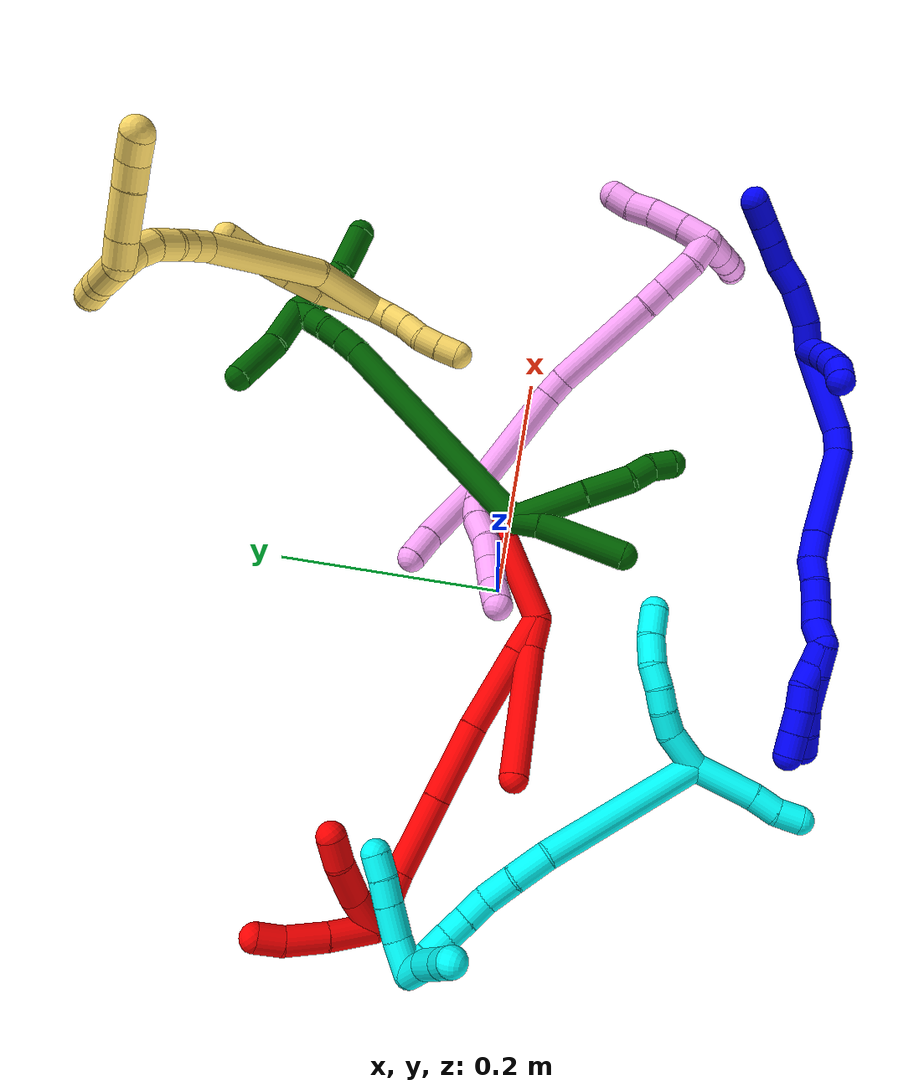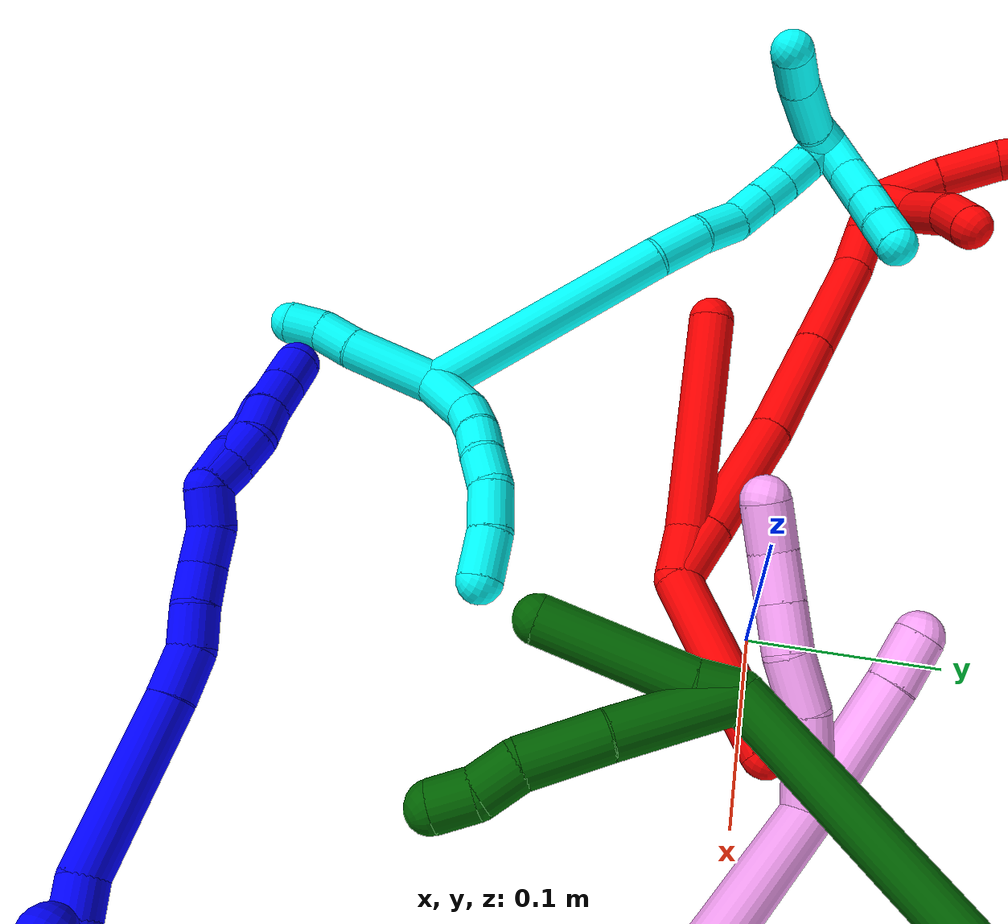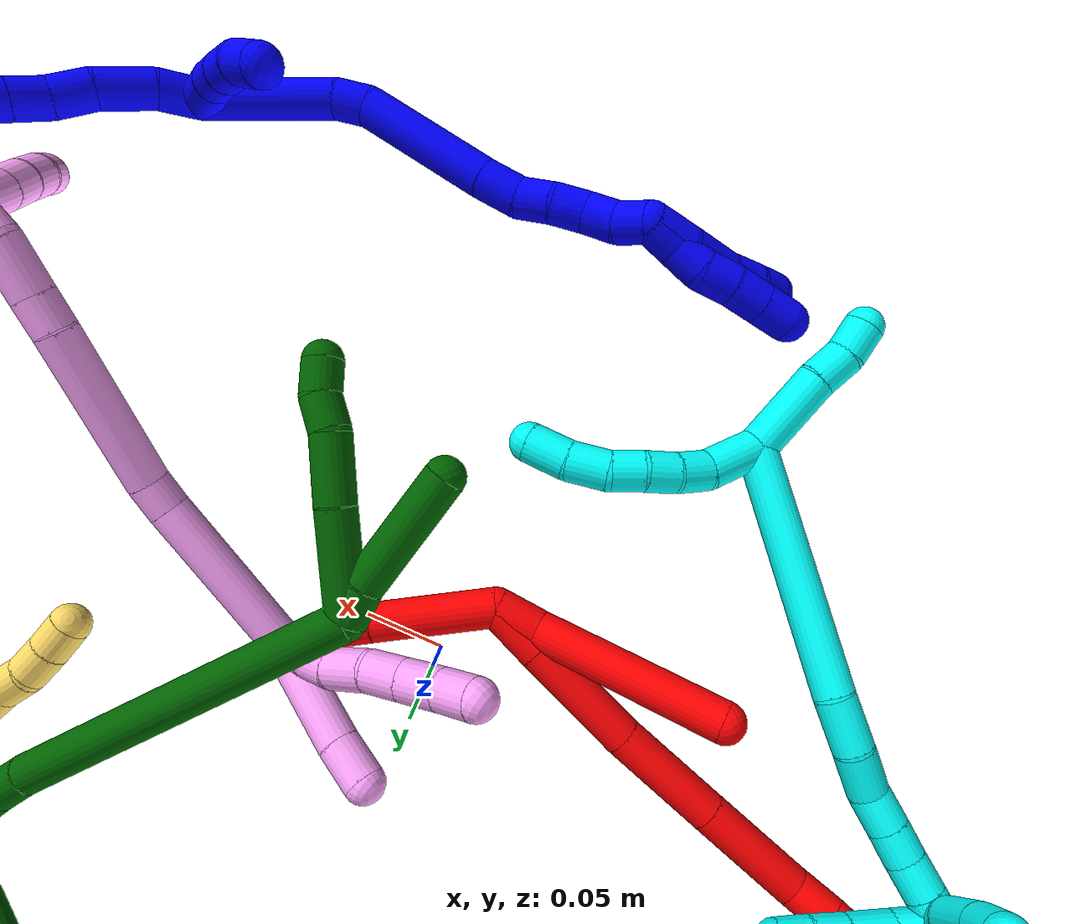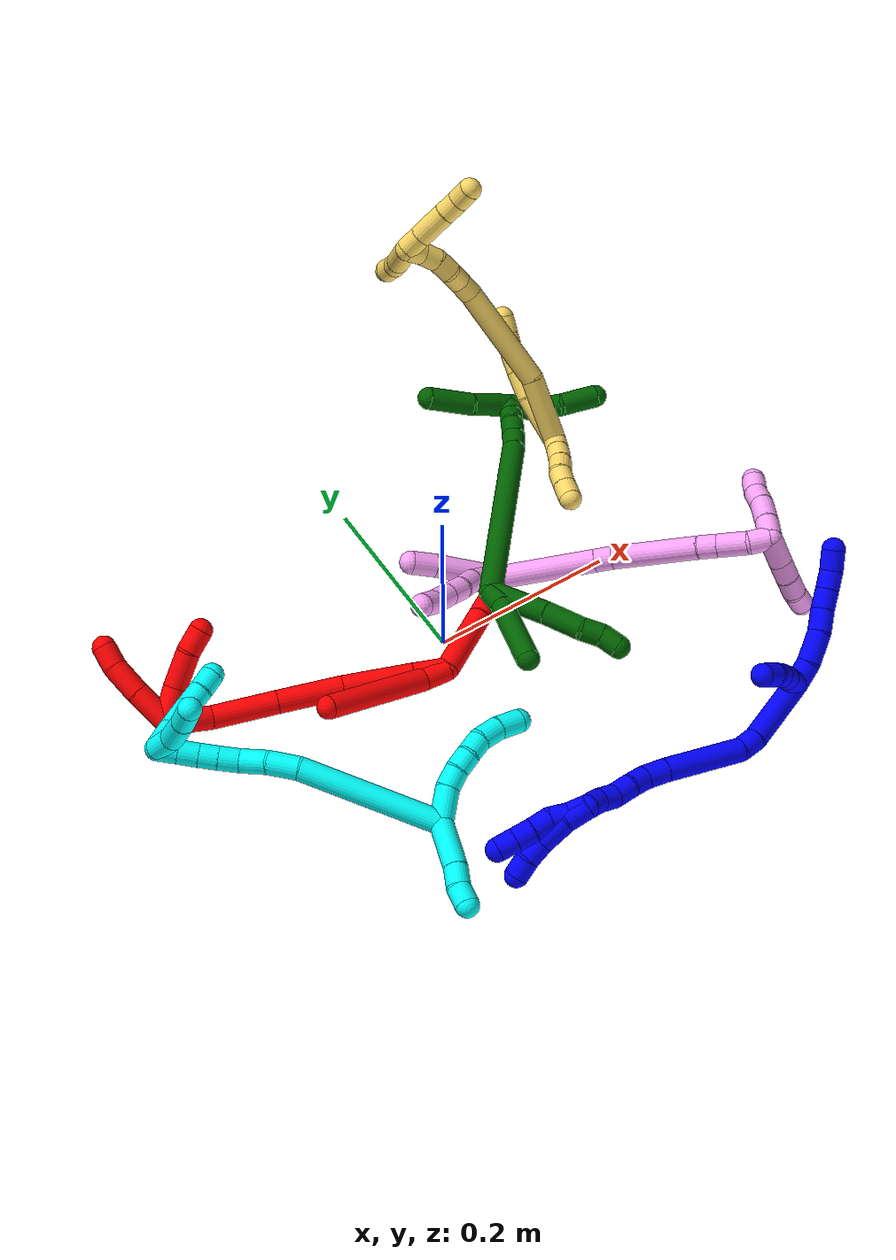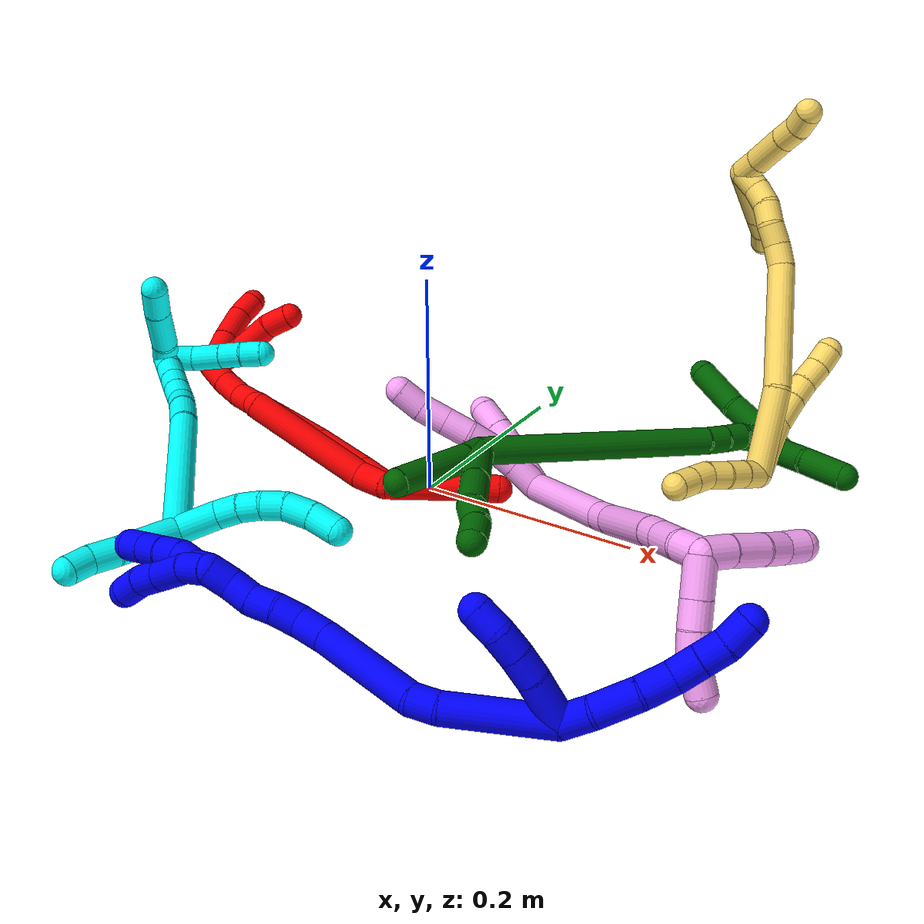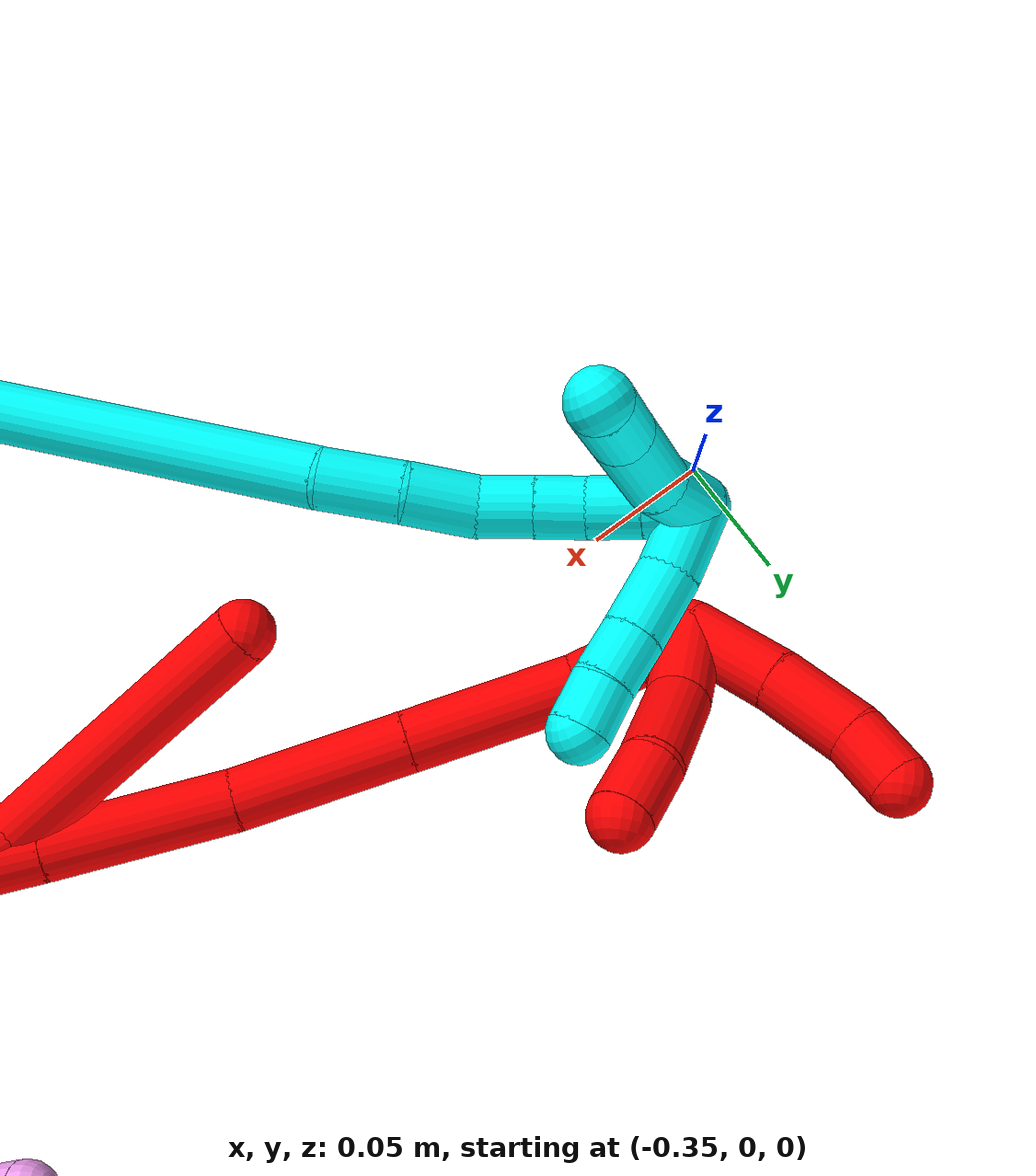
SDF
<sdf version="1.7">
 <world name="default">
  <plugin name="TubeGeneratorPlugin" filename="libtube_generator_plugin.so"/>
  <model name="photoneo_s_sensor">
   <static>1</static>
   <pose>0 0 2 1.57079 1.57079 3.14159</pose>
   <link name="link">
    <inertial><mass>0.1</mass></inertial>
    <sensor name="sensor" type="depth">
     <update_rate>30</update_rate>
     <camera>
      <horizontal_fov>1.22</horizontal_fov>
      <image><width>1920</width><height>1200</height><format>B8G8R8</format></image>
      <clip><near>0.1</near><far>4</far></clip>
      <depth_camera><output>points</output></depth_camera>
     </camera>
     <plugin name="camera_plugin" filename="libgazebo_ros_depth_camera.so">
      <baseline>0.2</baseline>
      <alwaysOn>1</alwaysOn>
      <updateRate>0.0</updateRate>
      <cameraName>camera_ir</cameraName>
      <imageTopicName>/camera/color/image_raw</imageTopicName>
      <cameraInfoTopicName>/camera/color/camera_info</cameraInfoTopicName>
      <depthImageTopicName>/camera/depth/image_raw</depthImageTopicName>
      <depthImageCameraInfoTopicName>/camera/depth/camera_info</depthImageCameraInfoTopicName>
      <pointCloudTopicName>/camera/depth/points</pointCloudTopicName>
      <frameName>fr_optical</frameName>
      <pointCloudCutoff>0.1</pointCloudCutoff>
      <pointCloudCutoffMax>2.0</pointCloudCutoffMax>
      <distortionK1>0</distortionK1>
      <distortionK2>0</distortionK2>
      <distortionK3>0</distortionK3>
      <distortionT1>0</distortionT1>
      <distortionT2>0</distortionT2>
      <CxPrime>0</CxPrime>
      <Cx>0</Cx>
      <Cy>0</Cy>
      <focalLength>0</focalLength>
      <hackBaseline>0</hackBaseline>
     </plugin>
    </sensor>
   </link>
  </model>
  <gravity>0 0 -9.8</gravity>
  <magnetic_field>6e-06 2.3e-05 -4.2e-05</magnetic_field>
  <atmosphere type="adiabatic"/>
  <physics name="default_physics" default="0" type="ode">
   <max_step_size>0.003</max_step_size>
   <real_time_factor>1</real_time_factor>
   <real_time_update_rate>1000</real_time_update_rate>
   <max_contacts>10000</max_contacts>
   <ode>
    <solver>
     <type>quick</type>
     <iters>100</iters>
     <sor>1.3</sor>
     <use_dynamic_moi_rescaling>0</use_dynamic_moi_rescaling>
    </solver>
    <constraints>
     <contact_max_correcting_vel>0</contact_max_correcting_vel>
     <contact_surface_layer>0.001</contact_surface_layer>
     <cfm>0</cfm>
     <erp>0.2</erp>
    </constraints>
   </ode>
  </physics>
  <scene><ambient>0.4 0.4 0.4 1</ambient><background>0.7 0.7 0.7 1</background><shadows>0</shadows></scene>
  <audio><device>default</device></audio>
  <spherical_coordinates>
   <surface_model>EARTH_WGS84</surface_model>
   <latitude_deg>0</latitude_deg>
   <longitude_deg>0</longitude_deg>
   <elevation>0</elevation>
   <heading_deg>0</heading_deg>
  </spherical_coordinates>
  <model name="bin">
   <static>1</static>
   <link name="bottom">
    <collision name="collision-bottom">
     <pose>0 0 -0.01 0 -0 0</pose>
     <geometry><box><size>0.8 0.6 0.02</size></box></geometry>
     <surface>
      <friction><ode><mu>100</mu><mu2>100</mu2></ode></friction>
      <contact><collide_bitmask>65535</collide_bitmask></contact>
     </surface>
    </collision>
   </link>
   <link name="west_wall">
    <collision name="collision-west_wall">
     <pose>-0.41 0 0.1 0 -0 0</pose>
     <geometry><box><size>0.02 0.6 0.2</size></box></geometry>
     <surface>
      <friction><ode><mu>100</mu><mu2>100</mu2></ode></friction>
      <contact><collide_bitmask>65535</collide_bitmask></contact>
     </surface>
    </collision>
   </link>
   <link name="east_wall">
    <collision name="collision-east_wall">
     <pose>0.41 0 0.1 0 -0 0</pose>
     <geometry><box><size>0.02 0.6 0.2</size></box></geometry>
     <surface>
      <friction><ode><mu>100</mu><mu2>100</mu2></ode></friction>
      <contact><collide_bitmask>65535</collide_bitmask></contact>
     </surface>
    </collision>
   </link>
   <link name="south_wall">
    <collision name="collision-south_wall">
     <pose>0 -0.31 0.1 0 -0 0</pose>
     <geometry><box><size>0.8 0.02 0.2</size></box></geometry>
     <surface>
      <friction><ode><mu>100</mu><mu2>100</mu2></ode></friction>
      <contact><collide_bitmask>65535</collide_bitmask></contact>
     </surface>
    </collision>
   </link>
   <link name="north_wall">
    <collision name="collision-north_wall">
     <pose>0 0.31 0.1 0 -0 0</pose>
     <geometry><box><size>0.8 0.02 0.2</size></box></geometry>
     <surface>
      <friction><ode><mu>100</mu><mu2>100</mu2></ode></friction>
      <contact><collide_bitmask>65535</collide_bitmask></contact>
     </surface>
    </collision>
   </link>
  </model>
  <model name="1">
   <static>0</static>
   <link name="1">
    <collision name="collision-cylinder-e_1_2_8">
     <pose>0.003713 0.005586 0.011015 -0.469323 0.292013 -0.070282</pose>
     <geometry><cylinder><radius>0.0125</radius><length>0.025792</length></cylinder></geometry>
     <surface>
      <friction><ode><mu>1.16</mu><mu2>1.16</mu2><slip1>0</slip1><slip2>0</slip2></ode></friction>
      <contact><ode><kp>1e+06</kp><kd>1</kd><max_vel>0</max_vel><min_depth>0.001</min_depth></ode></contact>
     </surface>
    </collision>
    <visual name="visual-cylinder-e_1_2_8">
     <pose>0.003713 0.005586 0.011015 -0.469323 0.292013 -0.070282</pose>
     <geometry><cylinder><radius>0.0125</radius><length>0.025792</length></cylinder></geometry>
     <material><ambient>0 0 1 1</ambient></material>
    </visual>
    <collision name="collision-cylinder-e_2_8_9">
     <pose>0.01546 0.019706 0.03456 -0.597923 0.487379 -0.152956</pose>
     <geometry><cylinder><radius>0.0125</radius><length>0.034316</length></cylinder></geometry>
     <surface>
      <friction><ode><mu>1.16</mu><mu2>1.16</mu2><slip1>0</slip1><slip2>0</slip2></ode></friction>
      <contact><ode><kp>1e+06</kp><kd>1</kd><max_vel>0</max_vel><min_depth>0.001</min_depth></ode></contact>
     </surface>
    </collision>
    <visual name="visual-cylinder-e_2_8_9">
     <pose>0.01546 0.019706 0.03456 -0.597923 0.487379 -0.152956</pose>
     <geometry><cylinder><radius>0.0125</radius><length>0.034316</length></cylinder></geometry>
     <material><ambient>0 0 1 1</ambient></material>
    </visual>
    <collision name="collision-cylinder-e_3_9_10">
     <pose>0.031002 0.035102 0.054379 -0.755213 0.6434 -0.262858</pose>
     <geometry><cylinder><radius>0.0125</radius><length>0.025026</length></cylinder></geometry>
     <surface>
      <friction><ode><mu>1.16</mu><mu2>1.16</mu2><slip1>0</slip1><slip2>0</slip2></ode></friction>
      <contact><ode><kp>1e+06</kp><kd>1</kd><max_vel>0</max_vel><min_depth>0.001</min_depth></ode></contact>
     </surface>
    </collision>
    <visual name="visual-cylinder-e_3_9_10">
     <pose>0.031002 0.035102 0.054379 -0.755213 0.6434 -0.262858</pose>
     <geometry><cylinder><radius>0.0125</radius><length>0.025026</length></cylinder></geometry>
     <material><ambient>0 0 1 1</ambient></material>
    </visual>
    <collision name="collision-cylinder-e_4_10_11">
     <pose>0.043055 0.048943 0.068872 -0.769568 0.425494 -0.174516</pose>
     <geometry><cylinder><radius>0.0125</radius><length>0.022024</length></cylinder></geometry>
     <surface>
      <friction><ode><mu>1.16</mu><mu2>1.16</mu2><slip1>0</slip1><slip2>0</slip2></ode></friction>
      <contact><ode><kp>1e+06</kp><kd>1</kd><max_vel>0</max_vel><min_depth>0.001</min_depth></ode></contact>
     </surface>
    </collision>
    <visual name="visual-cylinder-e_4_10_11">
     <pose>0.043055 0.048943 0.068872 -0.769568 0.425494 -0.174516</pose>
     <geometry><cylinder><radius>0.0125</radius><length>0.022024</length></cylinder></geometry>
     <material><ambient>0 0 1 1</ambient></material>
    </visual>
    <collision name="collision-cylinder-e_5_11_12">
     <pose>0.052066 0.062315 0.082564 -0.778003 0.455869 -0.18959</pose>
     <geometry><cylinder><radius>0.0125</radius><length>0.020287</length></cylinder></geometry>
     <surface>
      <friction><ode><mu>1.16</mu><mu2>1.16</mu2><slip1>0</slip1><slip2>0</slip2></ode></friction>
      <contact><ode><kp>1e+06</kp><kd>1</kd><max_vel>0</max_vel><min_depth>0.001</min_depth></ode></contact>
     </surface>
    </collision>
    <visual name="visual-cylinder-e_5_11_12">
     <pose>0.052066 0.062315 0.082564 -0.778003 0.455869 -0.18959</pose>
     <geometry><cylinder><radius>0.0125</radius><length>0.020287</length></cylinder></geometry>
     <material><ambient>0 0 1 1</ambient></material>
    </visual>
    <collision name="collision-cylinder-e_6_12_6">
     <pose>0.059896 0.077622 0.095083 -0.975977 0.302982 -0.161713</pose>
     <geometry><cylinder><radius>0.0125</radius><length>0.022554</length></cylinder></geometry>
     <surface>
      <friction><ode><mu>1.16</mu><mu2>1.16</mu2><slip1>0</slip1><slip2>0</slip2></ode></friction>
      <contact><ode><kp>1e+06</kp><kd>1</kd><max_vel>0</max_vel><min_depth>0.001</min_depth></ode></contact>
     </surface>
    </collision>
    <visual name="visual-cylinder-e_6_12_6">
     <pose>0.059896 0.077622 0.095083 -0.975977 0.302982 -0.161713</pose>
     <geometry><cylinder><radius>0.0125</radius><length>0.022554</length></cylinder></geometry>
     <material><ambient>0 0 1 1</ambient></material>
    </visual>
    <collision name="collision-cylinder-e_1_2_13">
     <pose>-0.012612 0.013924 -0.003633 -1.826 -0.719668 0.906317</pose>
     <geometry><cylinder><radius>0.0125</radius><length>0.038269</length></cylinder></geometry>
     <surface>
      <friction><ode><mu>1.16</mu><mu2>1.16</mu2><slip1>0</slip1><slip2>0</slip2></ode></friction>
      <contact><ode><kp>1e+06</kp><kd>1</kd><max_vel>0</max_vel><min_depth>0.001</min_depth></ode></contact>
     </surface>
    </collision>
    <visual name="visual-cylinder-e_1_2_13">
     <pose>-0.012612 0.013924 -0.003633 -1.826 -0.719668 0.906317</pose>
     <geometry><cylinder><radius>0.0125</radius><length>0.038269</length></cylinder></geometry>
     <material><ambient>0 0 1 1</ambient></material>
    </visual>
    <collision name="collision-cylinder-e_2_13_14">
     <pose>-0.032245 0.035188 -0.010142 -1.94433 -0.727507 1.01808</pose>
     <geometry><cylinder><radius>0.0125</radius><length>0.021115</length></cylinder></geometry>
     <surface>
      <friction><ode><mu>1.16</mu><mu2>1.16</mu2><slip1>0</slip1><slip2>0</slip2></ode></friction>
      <contact><ode><kp>1e+06</kp><kd>1</kd><max_vel>0</max_vel><min_depth>0.001</min_depth></ode></contact>
     </surface>
    </collision>
    <visual name="visual-cylinder-e_2_13_14">
     <pose>-0.032245 0.035188 -0.010142 -1.94433 -0.727507 1.01808</pose>
     <geometry><cylinder><radius>0.0125</radius><length>0.021115</length></cylinder></geometry>
     <material><ambient>0 0 1 1</ambient></material>
    </visual>
    <collision name="collision-cylinder-e_3_14_15">
     <pose>-0.046192 0.049055 -0.01625 -2.0305 -0.760358 1.14395</pose>
     <geometry><cylinder><radius>0.0125</radius><length>0.020099</length></cylinder></geometry>
     <surface>
      <friction><ode><mu>1.16</mu><mu2>1.16</mu2><slip1>0</slip1><slip2>0</slip2></ode></friction>
      <contact><ode><kp>1e+06</kp><kd>1</kd><max_vel>0</max_vel><min_depth>0.001</min_depth></ode></contact>
     </surface>
    </collision>
    <visual name="visual-cylinder-e_3_14_15">
     <pose>-0.046192 0.049055 -0.01625 -2.0305 -0.760358 1.14395</pose>
     <geometry><cylinder><radius>0.0125</radius><length>0.020099</length></cylinder></geometry>
     <material><ambient>0 0 1 1</ambient></material>
    </visual>
    <collision name="collision-cylinder-e_4_15_5">
     <pose>-0.058432 0.061823 -0.025647 -2.35004 -0.544559 1.17821</pose>
     <geometry><cylinder><radius>0.0125</radius><length>0.020517</length></cylinder></geometry>
     <surface>
      <friction><ode><mu>1.16</mu><mu2>1.16</mu2><slip1>0</slip1><slip2>0</slip2></ode></friction>
      <contact><ode><kp>1e+06</kp><kd>1</kd><max_vel>0</max_vel><min_depth>0.001</min_depth></ode></contact>
     </surface>
    </collision>
    <visual name="visual-cylinder-e_4_15_5">
     <pose>-0.058432 0.061823 -0.025647 -2.35004 -0.544559 1.17821</pose>
     <geometry><cylinder><radius>0.0125</radius><length>0.020517</length></cylinder></geometry>
     <material><ambient>0 0 1 1</ambient></material>
    </visual>
    <collision name="collision-cylinder-e_1_2_16">
     <pose>-0.026195 -0.001351 -0.032962 3.10062 -0.671091 -3.02422</pose>
     <geometry><cylinder><radius>0.0125</radius><length>0.084249</length></cylinder></geometry>
     <surface>
      <friction><ode><mu>1.16</mu><mu2>1.16</mu2><slip1>0</slip1><slip2>0</slip2></ode></friction>
      <contact><ode><kp>1e+06</kp><kd>1</kd><max_vel>0</max_vel><min_depth>0.001</min_depth></ode></contact>
     </surface>
    </collision>
    <visual name="visual-cylinder-e_1_2_16">
     <pose>-0.026195 -0.001351 -0.032962 3.10062 -0.671091 -3.02422</pose>
     <geometry><cylinder><radius>0.0125</radius><length>0.084249</length></cylinder></geometry>
     <material><ambient>0 0 1 1</ambient></material>
    </visual>
    <collision name="collision-cylinder-e_2_16_17">
     <pose>-0.057207 -0.001342 -0.075237 -2.99654 -0.473052 2.55607</pose>
     <geometry><cylinder><radius>0.0125</radius><length>0.021148</length></cylinder></geometry>
     <surface>
      <friction><ode><mu>1.16</mu><mu2>1.16</mu2><slip1>0</slip1><slip2>0</slip2></ode></friction>
      <contact><ode><kp>1e+06</kp><kd>1</kd><max_vel>0</max_vel><min_depth>0.001</min_depth></ode></contact>
     </surface>
    </collision>
    <visual name="visual-cylinder-e_2_16_17">
     <pose>-0.057207 -0.001342 -0.075237 -2.99654 -0.473052 2.55607</pose>
     <geometry><cylinder><radius>0.0125</radius><length>0.021148</length></cylinder></geometry>
     <material><ambient>0 0 1 1</ambient></material>
    </visual>
    <collision name="collision-cylinder-e_3_17_18">
     <pose>-0.071049 0.015587 -0.123723 -2.76329 -0.210921 1.01017</pose>
     <geometry><cylinder><radius>0.0125</radius><length>0.086215</length></cylinder></geometry>
     <surface>
      <friction><ode><mu>1.16</mu><mu2>1.16</mu2><slip1>0</slip1><slip2>0</slip2></ode></friction>
      <contact><ode><kp>1e+06</kp><kd>1</kd><max_vel>0</max_vel><min_depth>0.001</min_depth></ode></contact>
     </surface>
    </collision>
    <visual name="visual-cylinder-e_3_17_18">
     <pose>-0.071049 0.015587 -0.123723 -2.76329 -0.210921 1.01017</pose>
     <geometry><cylinder><radius>0.0125</radius><length>0.086215</length></cylinder></geometry>
     <material><ambient>0 0 1 1</ambient></material>
    </visual>
    <collision name="collision-cylinder-e_4_18_19">
     <pose>-0.083384 0.035079 -0.174482 -2.81517 -0.264204 1.35785</pose>
     <geometry><cylinder><radius>0.0125</radius><length>0.025347</length></cylinder></geometry>
     <surface>
      <friction><ode><mu>1.16</mu><mu2>1.16</mu2><slip1>0</slip1><slip2>0</slip2></ode></friction>
      <contact><ode><kp>1e+06</kp><kd>1</kd><max_vel>0</max_vel><min_depth>0.001</min_depth></ode></contact>
     </surface>
    </collision>
    <visual name="visual-cylinder-e_4_18_19">
     <pose>-0.083384 0.035079 -0.174482 -2.81517 -0.264204 1.35785</pose>
     <geometry><cylinder><radius>0.0125</radius><length>0.025347</length></cylinder></geometry>
     <material><ambient>0 0 1 1</ambient></material>
    </visual>
    <collision name="collision-cylinder-e_5_19_20">
     <pose>-0.092564 0.042279 -0.194344 -2.76452 -0.583144 2.00902</pose>
     <geometry><cylinder><radius>0.0125</radius><length>0.021322</length></cylinder></geometry>
     <surface>
      <friction><ode><mu>1.16</mu><mu2>1.16</mu2><slip1>0</slip1><slip2>0</slip2></ode></friction>
      <contact><ode><kp>1e+06</kp><kd>1</kd><max_vel>0</max_vel><min_depth>0.001</min_depth></ode></contact>
     </surface>
    </collision>
    <visual name="visual-cylinder-e_5_19_20">
     <pose>-0.092564 0.042279 -0.194344 -2.76452 -0.583144 2.00902</pose>
     <geometry><cylinder><radius>0.0125</radius><length>0.021322</length></cylinder></geometry>
     <material><ambient>0 0 1 1</ambient></material>
    </visual>
    <collision name="collision-cylinder-e_6_20_21">
     <pose>-0.103053 0.047518 -0.21182 -2.93147 -0.456285 2.28898</pose>
     <geometry><cylinder><radius>0.0125</radius><length>0.020963</length></cylinder></geometry>
     <surface>
      <friction><ode><mu>1.16</mu><mu2>1.16</mu2><slip1>0</slip1><slip2>0</slip2></ode></friction>
      <contact><ode><kp>1e+06</kp><kd>1</kd><max_vel>0</max_vel><min_depth>0.001</min_depth></ode></contact>
     </surface>
    </collision>
    <visual name="visual-cylinder-e_6_20_21">
     <pose>-0.103053 0.047518 -0.21182 -2.93147 -0.456285 2.28898</pose>
     <geometry><cylinder><radius>0.0125</radius><length>0.020963</length></cylinder></geometry>
     <material><ambient>0 0 1 1</ambient></material>
    </visual>
    <collision name="collision-cylinder-e_7_21_22">
     <pose>-0.112095 0.054089 -0.229004 -2.61794 -0.447498 1.40803</pose>
     <geometry><cylinder><radius>0.0125</radius><length>0.020446</length></cylinder></geometry>
     <surface>
      <friction><ode><mu>1.16</mu><mu2>1.16</mu2><slip1>0</slip1><slip2>0</slip2></ode></friction>
      <contact><ode><kp>1e+06</kp><kd>1</kd><max_vel>0</max_vel><min_depth>0.001</min_depth></ode></contact>
     </surface>
    </collision>
    <visual name="visual-cylinder-e_7_21_22">
     <pose>-0.112095 0.054089 -0.229004 -2.61794 -0.447498 1.40803</pose>
     <geometry><cylinder><radius>0.0125</radius><length>0.020446</length></cylinder></geometry>
     <material><ambient>0 0 1 1</ambient></material>
    </visual>
    <collision name="collision-cylinder-e_8_22_1">
     <pose>-0.123493 0.062912 -0.243044 -2.53384 -0.757123 1.80632</pose>
     <geometry><cylinder><radius>0.0125</radius><length>0.02031</length></cylinder></geometry>
     <surface>
      <friction><ode><mu>1.16</mu><mu2>1.16</mu2><slip1>0</slip1><slip2>0</slip2></ode></friction>
      <contact><ode><kp>1e+06</kp><kd>1</kd><max_vel>0</max_vel><min_depth>0.001</min_depth></ode></contact>
     </surface>
    </collision>
    <visual name="visual-cylinder-e_8_22_1">
     <pose>-0.123493 0.062912 -0.243044 -2.53384 -0.757123 1.80632</pose>
     <geometry><cylinder><radius>0.0125</radius><length>0.02031</length></cylinder></geometry>
     <material><ambient>0 0 1 1</ambient></material>
    </visual>
    <collision name="collision-cylinder-e_1_1_23">
     <pose>-0.129876 0.067525 -0.259078 -3.10168 0.059289 -1.95678</pose>
     <geometry><cylinder><radius>0.0125</radius><length>0.02</length></cylinder></geometry>
     <surface>
      <friction><ode><mu>1.16</mu><mu2>1.16</mu2><slip1>0</slip1><slip2>0</slip2></ode></friction>
      <contact><ode><kp>1e+06</kp><kd>1</kd><max_vel>0</max_vel><min_depth>0.001</min_depth></ode></contact>
     </surface>
    </collision>
    <visual name="visual-cylinder-e_1_1_23">
     <pose>-0.129876 0.067525 -0.259078 -3.10168 0.059289 -1.95678</pose>
     <geometry><cylinder><radius>0.0125</radius><length>0.02</length></cylinder></geometry>
     <material><ambient>0 0 1 1</ambient></material>
    </visual>
    <collision name="collision-cylinder-e_2_23_24">
     <pose>-0.129301 0.070815 -0.278625 -2.84826 -0.00175 0.011847</pose>
     <geometry><cylinder><radius>0.0125</radius><length>0.02</length></cylinder></geometry>
     <surface>
      <friction><ode><mu>1.16</mu><mu2>1.16</mu2><slip1>0</slip1><slip2>0</slip2></ode></friction>
      <contact><ode><kp>1e+06</kp><kd>1</kd><max_vel>0</max_vel><min_depth>0.001</min_depth></ode></contact>
     </surface>
    </collision>
    <visual name="visual-cylinder-e_2_23_24">
     <pose>-0.129301 0.070815 -0.278625 -2.84826 -0.00175 0.011847</pose>
     <geometry><cylinder><radius>0.0125</radius><length>0.02</length></cylinder></geometry>
     <material><ambient>0 0 1 1</ambient></material>
    </visual>
    <collision name="collision-cylinder-e_3_24_25">
     <pose>-0.131561 0.074051 -0.297937 -3.10625 -0.226229 2.83296</pose>
     <geometry><cylinder><radius>0.0125</radius><length>0.02</length></cylinder></geometry>
     <surface>
      <friction><ode><mu>1.16</mu><mu2>1.16</mu2><slip1>0</slip1><slip2>0</slip2></ode></friction>
      <contact><ode><kp>1e+06</kp><kd>1</kd><max_vel>0</max_vel><min_depth>0.001</min_depth></ode></contact>
     </surface>
    </collision>
    <visual name="visual-cylinder-e_3_24_25">
     <pose>-0.131561 0.074051 -0.297937 -3.10625 -0.226229 2.83296</pose>
     <geometry><cylinder><radius>0.0125</radius><length>0.02</length></cylinder></geometry>
     <material><ambient>0 0 1 1</ambient></material>
    </visual>
    <collision name="collision-cylinder-e_4_25_26">
     <pose>-0.134957 0.074754 -0.317603 -3.10547 -0.115533 2.53616</pose>
     <geometry><cylinder><radius>0.0125</radius><length>0.02</length></cylinder></geometry>
     <surface>
      <friction><ode><mu>1.16</mu><mu2>1.16</mu2><slip1>0</slip1><slip2>0</slip2></ode></friction>
      <contact><ode><kp>1e+06</kp><kd>1</kd><max_vel>0</max_vel><min_depth>0.001</min_depth></ode></contact>
     </surface>
    </collision>
    <visual name="visual-cylinder-e_4_25_26">
     <pose>-0.134957 0.074754 -0.317603 -3.10547 -0.115533 2.53616</pose>
     <geometry><cylinder><radius>0.0125</radius><length>0.02</length></cylinder></geometry>
     <material><ambient>0 0 1 1</ambient></material>
    </visual>
    <collision name="collision-cylinder-e_5_26_4">
     <pose>-0.137245 0.075442 -0.33746 -3.10839 -0.113745 2.57411</pose>
     <geometry><cylinder><radius>0.0125</radius><length>0.02</length></cylinder></geometry>
     <surface>
      <friction><ode><mu>1.16</mu><mu2>1.16</mu2><slip1>0</slip1><slip2>0</slip2></ode></friction>
      <contact><ode><kp>1e+06</kp><kd>1</kd><max_vel>0</max_vel><min_depth>0.001</min_depth></ode></contact>
     </surface>
    </collision>
    <visual name="visual-cylinder-e_5_26_4">
     <pose>-0.137245 0.075442 -0.33746 -3.10839 -0.113745 2.57411</pose>
     <geometry><cylinder><radius>0.0125</radius><length>0.02</length></cylinder></geometry>
     <material><ambient>0 0 1 1</ambient></material>
    </visual>
    <collision name="collision-cylinder-e_1_1_27">
     <pose>-0.13159 0.066623 -0.261807 3.10192 -0.087989 -2.29485</pose>
     <geometry><cylinder><radius>0.0125</radius><length>0.025527</length></cylinder></geometry>
     <surface>
      <friction><ode><mu>1.16</mu><mu2>1.16</mu2><slip1>0</slip1><slip2>0</slip2></ode></friction>
      <contact><ode><kp>1e+06</kp><kd>1</kd><max_vel>0</max_vel><min_depth>0.001</min_depth></ode></contact>
     </surface>
    </collision>
    <visual name="visual-cylinder-e_1_1_27">
     <pose>-0.13159 0.066623 -0.261807 3.10192 -0.087989 -2.29485</pose>
     <geometry><cylinder><radius>0.0125</radius><length>0.025527</length></cylinder></geometry>
     <material><ambient>0 0 1 1</ambient></material>
    </visual>
    <collision name="collision-cylinder-e_2_27_28">
     <pose>-0.133079 0.061474 -0.290055 2.85124 -0.022652 -0.154628</pose>
     <geometry><cylinder><radius>0.0125</radius><length>0.032454</length></cylinder></geometry>
     <surface>
      <friction><ode><mu>1.16</mu><mu2>1.16</mu2><slip1>0</slip1><slip2>0</slip2></ode></friction>
      <contact><ode><kp>1e+06</kp><kd>1</kd><max_vel>0</max_vel><min_depth>0.001</min_depth></ode></contact>
     </surface>
    </collision>
    <visual name="visual-cylinder-e_2_27_28">
     <pose>-0.133079 0.061474 -0.290055 2.85124 -0.022652 -0.154628</pose>
     <geometry><cylinder><radius>0.0125</radius><length>0.032454</length></cylinder></geometry>
     <material><ambient>0 0 1 1</ambient></material>
    </visual>
    <collision name="collision-cylinder-e_3_28_29">
     <pose>-0.135326 0.05337 -0.315536 2.80659 -0.176728 -0.965254</pose>
     <geometry><cylinder><radius>0.0125</radius><length>0.021377</length></cylinder></geometry>
     <surface>
      <friction><ode><mu>1.16</mu><mu2>1.16</mu2><slip1>0</slip1><slip2>0</slip2></ode></friction>
      <contact><ode><kp>1e+06</kp><kd>1</kd><max_vel>0</max_vel><min_depth>0.001</min_depth></ode></contact>
     </surface>
    </collision>
    <visual name="visual-cylinder-e_3_28_29">
     <pose>-0.135326 0.05337 -0.315536 2.80659 -0.176728 -0.965254</pose>
     <geometry><cylinder><radius>0.0125</radius><length>0.021377</length></cylinder></geometry>
     <material><ambient>0 0 1 1</ambient></material>
    </visual>
    <collision name="collision-cylinder-e_4_29_3">
     <pose>-0.138002 0.044549 -0.334256 2.59346 -0.077291 -0.273342</pose>
     <geometry><cylinder><radius>0.0125</radius><length>0.020642</length></cylinder></geometry>
     <surface>
      <friction><ode><mu>1.16</mu><mu2>1.16</mu2><slip1>0</slip1><slip2>0</slip2></ode></friction>
      <contact><ode><kp>1e+06</kp><kd>1</kd><max_vel>0</max_vel><min_depth>0.001</min_depth></ode></contact>
     </surface>
    </collision>
    <visual name="visual-cylinder-e_4_29_3">
     <pose>-0.138002 0.044549 -0.334256 2.59346 -0.077291 -0.273342</pose>
     <geometry><cylinder><radius>0.0125</radius><length>0.020642</length></cylinder></geometry>
     <material><ambient>0 0 1 1</ambient></material>
    </visual>
    <collision name="collision-sphere-3">
     <pose>-0.138799 0.039186 -0.343039 0 -0 0</pose>
     <geometry><sphere><radius>0.0125</radius></sphere></geometry>
     <surface>
      <friction><ode><mu>1.16</mu><mu2>1.16</mu2><slip1>0</slip1><slip2>0</slip2></ode></friction>
      <contact><ode><kp>1e+06</kp><kd>1</kd><max_vel>0</max_vel><min_depth>0.001</min_depth></ode></contact>
     </surface>
    </collision>
    <visual name="visual-sphere-3">
     <pose>-0.138799 0.039186 -0.343039 0 -0 0</pose>
     <geometry><sphere><radius>0.0125</radius></sphere></geometry>
     <material><ambient>0 0 1 1</ambient></material>
    </visual>
    <collision name="collision-sphere-29">
     <pose>-0.137205 0.049911 -0.325473 0 -0 0</pose>
     <geometry><sphere><radius>0.0125</radius></sphere></geometry>
     <surface>
      <friction><ode><mu>1.16</mu><mu2>1.16</mu2><slip1>0</slip1><slip2>0</slip2></ode></friction>
      <contact><ode><kp>1e+06</kp><kd>1</kd><max_vel>0</max_vel><min_depth>0.001</min_depth></ode></contact>
     </surface>
    </collision>
    <visual name="visual-sphere-29">
     <pose>-0.137205 0.049911 -0.325473 0 -0 0</pose>
     <geometry><sphere><radius>0.0125</radius></sphere></geometry>
     <material><ambient>0 0 1 1</ambient></material>
    </visual>
    <collision name="collision-sphere-28">
     <pose>-0.133446 0.056829 -0.305599 0 -0 0</pose>
     <geometry><sphere><radius>0.0125</radius></sphere></geometry>
     <surface>
      <friction><ode><mu>1.16</mu><mu2>1.16</mu2><slip1>0</slip1><slip2>0</slip2></ode></friction>
      <contact><ode><kp>1e+06</kp><kd>1</kd><max_vel>0</max_vel><min_depth>0.001</min_depth></ode></contact>
     </surface>
    </collision>
    <visual name="visual-sphere-28">
     <pose>-0.133446 0.056829 -0.305599 0 -0 0</pose>
     <geometry><sphere><radius>0.0125</radius></sphere></geometry>
     <material><ambient>0 0 1 1</ambient></material>
    </visual>
    <collision name="collision-sphere-27">
     <pose>-0.132711 0.066119 -0.274511 0 -0 0</pose>
     <geometry><sphere><radius>0.0125</radius></sphere></geometry>
     <surface>
      <friction><ode><mu>1.16</mu><mu2>1.16</mu2><slip1>0</slip1><slip2>0</slip2></ode></friction>
      <contact><ode><kp>1e+06</kp><kd>1</kd><max_vel>0</max_vel><min_depth>0.001</min_depth></ode></contact>
     </surface>
    </collision>
    <visual name="visual-sphere-27">
     <pose>-0.132711 0.066119 -0.274511 0 -0 0</pose>
     <geometry><sphere><radius>0.0125</radius></sphere></geometry>
     <material><ambient>0 0 1 1</ambient></material>
    </visual>
    <collision name="collision-sphere-4">
     <pose>-0.13838 0.075772 -0.34739 0 -0 0</pose>
     <geometry><sphere><radius>0.0125</radius></sphere></geometry>
     <surface>
      <friction><ode><mu>1.16</mu><mu2>1.16</mu2><slip1>0</slip1><slip2>0</slip2></ode></friction>
      <contact><ode><kp>1e+06</kp><kd>1</kd><max_vel>0</max_vel><min_depth>0.001</min_depth></ode></contact>
     </surface>
    </collision>
    <visual name="visual-sphere-4">
     <pose>-0.13838 0.075772 -0.34739 0 -0 0</pose>
     <geometry><sphere><radius>0.0125</radius></sphere></geometry>
     <material><ambient>0 0 1 1</ambient></material>
    </visual>
    <collision name="collision-sphere-26">
     <pose>-0.13611 0.075113 -0.32753 0 -0 0</pose>
     <geometry><sphere><radius>0.0125</radius></sphere></geometry>
     <surface>
      <friction><ode><mu>1.16</mu><mu2>1.16</mu2><slip1>0</slip1><slip2>0</slip2></ode></friction>
      <contact><ode><kp>1e+06</kp><kd>1</kd><max_vel>0</max_vel><min_depth>0.001</min_depth></ode></contact>
     </surface>
    </collision>
    <visual name="visual-sphere-26">
     <pose>-0.13611 0.075113 -0.32753 0 -0 0</pose>
     <geometry><sphere><radius>0.0125</radius></sphere></geometry>
     <material><ambient>0 0 1 1</ambient></material>
    </visual>
    <collision name="collision-sphere-25">
     <pose>-0.133804 0.074395 -0.307676 0 -0 0</pose>
     <geometry><sphere><radius>0.0125</radius></sphere></geometry>
     <surface>
      <friction><ode><mu>1.16</mu><mu2>1.16</mu2><slip1>0</slip1><slip2>0</slip2></ode></friction>
      <contact><ode><kp>1e+06</kp><kd>1</kd><max_vel>0</max_vel><min_depth>0.001</min_depth></ode></contact>
     </surface>
    </collision>
    <visual name="visual-sphere-25">
     <pose>-0.133804 0.074395 -0.307676 0 -0 0</pose>
     <geometry><sphere><radius>0.0125</radius></sphere></geometry>
     <material><ambient>0 0 1 1</ambient></material>
    </visual>
    <collision name="collision-sphere-24">
     <pose>-0.129318 0.073707 -0.288198 0 -0 0</pose>
     <geometry><sphere><radius>0.0125</radius></sphere></geometry>
     <surface>
      <friction><ode><mu>1.16</mu><mu2>1.16</mu2><slip1>0</slip1><slip2>0</slip2></ode></friction>
      <contact><ode><kp>1e+06</kp><kd>1</kd><max_vel>0</max_vel><min_depth>0.001</min_depth></ode></contact>
     </surface>
    </collision>
    <visual name="visual-sphere-24">
     <pose>-0.129318 0.073707 -0.288198 0 -0 0</pose>
     <geometry><sphere><radius>0.0125</radius></sphere></geometry>
     <material><ambient>0 0 1 1</ambient></material>
    </visual>
    <collision name="collision-sphere-23">
     <pose>-0.129283 0.067924 -0.269053 0 -0 0</pose>
     <geometry><sphere><radius>0.0125</radius></sphere></geometry>
     <surface>
      <friction><ode><mu>1.16</mu><mu2>1.16</mu2><slip1>0</slip1><slip2>0</slip2></ode></friction>
      <contact><ode><kp>1e+06</kp><kd>1</kd><max_vel>0</max_vel><min_depth>0.001</min_depth></ode></contact>
     </surface>
    </collision>
    <visual name="visual-sphere-23">
     <pose>-0.129283 0.067924 -0.269053 0 -0 0</pose>
     <geometry><sphere><radius>0.0125</radius></sphere></geometry>
     <material><ambient>0 0 1 1</ambient></material>
    </visual>
    <collision name="collision-sphere-1">
     <pose>-0.130468 0.067127 -0.249104 0 -0 0</pose>
     <geometry><sphere><radius>0.0125</radius></sphere></geometry>
     <surface>
      <friction><ode><mu>1.16</mu><mu2>1.16</mu2><slip1>0</slip1><slip2>0</slip2></ode></friction>
      <contact><ode><kp>1e+06</kp><kd>1</kd><max_vel>0</max_vel><min_depth>0.001</min_depth></ode></contact>
     </surface>
    </collision>
    <visual name="visual-sphere-1">
     <pose>-0.130468 0.067127 -0.249104 0 -0 0</pose>
     <geometry><sphere><radius>0.0125</radius></sphere></geometry>
     <material><ambient>0 0 1 1</ambient></material>
    </visual>
    <collision name="collision-sphere-22">
     <pose>-0.116518 0.058698 -0.236985 0 -0 0</pose>
     <geometry><sphere><radius>0.0125</radius></sphere></geometry>
     <surface>
      <friction><ode><mu>1.16</mu><mu2>1.16</mu2><slip1>0</slip1><slip2>0</slip2></ode></friction>
      <contact><ode><kp>1e+06</kp><kd>1</kd><max_vel>0</max_vel><min_depth>0.001</min_depth></ode></contact>
     </surface>
    </collision>
    <visual name="visual-sphere-22">
     <pose>-0.116518 0.058698 -0.236985 0 -0 0</pose>
     <geometry><sphere><radius>0.0125</radius></sphere></geometry>
     <material><ambient>0 0 1 1</ambient></material>
    </visual>
    <collision name="collision-sphere-21">
     <pose>-0.107671 0.04948 -0.221022 0 -0 0</pose>
     <geometry><sphere><radius>0.0125</radius></sphere></geometry>
     <surface>
      <friction><ode><mu>1.16</mu><mu2>1.16</mu2><slip1>0</slip1><slip2>0</slip2></ode></friction>
      <contact><ode><kp>1e+06</kp><kd>1</kd><max_vel>0</max_vel><min_depth>0.001</min_depth></ode></contact>
     </surface>
    </collision>
    <visual name="visual-sphere-21">
     <pose>-0.107671 0.04948 -0.221022 0 -0 0</pose>
     <geometry><sphere><radius>0.0125</radius></sphere></geometry>
     <material><ambient>0 0 1 1</ambient></material>
    </visual>
    <collision name="collision-sphere-12">
     <pose>0.056531 0.068707 0.089051 0 -0 0</pose>
     <geometry><sphere><radius>0.0125</radius></sphere></geometry>
     <surface>
      <friction><ode><mu>1.16</mu><mu2>1.16</mu2><slip1>0</slip1><slip2>0</slip2></ode></friction>
      <contact><ode><kp>1e+06</kp><kd>1</kd><max_vel>0</max_vel><min_depth>0.001</min_depth></ode></contact>
     </surface>
    </collision>
    <visual name="visual-sphere-12">
     <pose>0.056531 0.068707 0.089051 0 -0 0</pose>
     <geometry><sphere><radius>0.0125</radius></sphere></geometry>
     <material><ambient>0 0 1 1</ambient></material>
    </visual>
    <collision name="collision-sphere-11">
     <pose>0.0476 0.055922 0.076076 0 -0 0</pose>
     <geometry><sphere><radius>0.0125</radius></sphere></geometry>
     <surface>
      <friction><ode><mu>1.16</mu><mu2>1.16</mu2><slip1>0</slip1><slip2>0</slip2></ode></friction>
      <contact><ode><kp>1e+06</kp><kd>1</kd><max_vel>0</max_vel><min_depth>0.001</min_depth></ode></contact>
     </surface>
    </collision>
    <visual name="visual-sphere-11">
     <pose>0.0476 0.055922 0.076076 0 -0 0</pose>
     <geometry><sphere><radius>0.0125</radius></sphere></geometry>
     <material><ambient>0 0 1 1</ambient></material>
    </visual>
    <collision name="collision-sphere-10">
     <pose>0.038509 0.041964 0.061668 0 -0 0</pose>
     <geometry><sphere><radius>0.0125</radius></sphere></geometry>
     <surface>
      <friction><ode><mu>1.16</mu><mu2>1.16</mu2><slip1>0</slip1><slip2>0</slip2></ode></friction>
      <contact><ode><kp>1e+06</kp><kd>1</kd><max_vel>0</max_vel><min_depth>0.001</min_depth></ode></contact>
     </surface>
    </collision>
    <visual name="visual-sphere-10">
     <pose>0.038509 0.041964 0.061668 0 -0 0</pose>
     <geometry><sphere><radius>0.0125</radius></sphere></geometry>
     <material><ambient>0 0 1 1</ambient></material>
    </visual>
    <collision name="collision-sphere-9">
     <pose>0.023496 0.02824 0.04709 0 -0 0</pose>
     <geometry><sphere><radius>0.0125</radius></sphere></geometry>
     <surface>
      <friction><ode><mu>1.16</mu><mu2>1.16</mu2><slip1>0</slip1><slip2>0</slip2></ode></friction>
      <contact><ode><kp>1e+06</kp><kd>1</kd><max_vel>0</max_vel><min_depth>0.001</min_depth></ode></contact>
     </surface>
    </collision>
    <visual name="visual-sphere-9">
     <pose>0.023496 0.02824 0.04709 0 -0 0</pose>
     <geometry><sphere><radius>0.0125</radius></sphere></geometry>
     <material><ambient>0 0 1 1</ambient></material>
    </visual>
    <collision name="collision-sphere-2">
     <geometry><sphere><radius>0.0125</radius></sphere></geometry>
     <surface>
      <friction><ode><mu>1.16</mu><mu2>1.16</mu2><slip1>0</slip1><slip2>0</slip2></ode></friction>
      <contact><ode><kp>1e+06</kp><kd>1</kd><max_vel>0</max_vel><min_depth>0.001</min_depth></ode></contact>
     </surface>
    </collision>
    <visual name="visual-sphere-2">
     <geometry><sphere><radius>0.0125</radius></sphere></geometry>
     <material><ambient>0 0 1 1</ambient></material>
    </visual>
    <collision name="collision-sphere-19">
     <pose>-0.086693 0.039002 -0.18607 0 -0 0</pose>
     <geometry><sphere><radius>0.0125</radius></sphere></geometry>
     <surface>
      <friction><ode><mu>1.16</mu><mu2>1.16</mu2><slip1>0</slip1><slip2>0</slip2></ode></friction>
      <contact><ode><kp>1e+06</kp><kd>1</kd><max_vel>0</max_vel><min_depth>0.001</min_depth></ode></contact>
     </surface>
    </collision>
    <visual name="visual-sphere-19">
     <pose>-0.086693 0.039002 -0.18607 0 -0 0</pose>
     <geometry><sphere><radius>0.0125</radius></sphere></geometry>
     <material><ambient>0 0 1 1</ambient></material>
    </visual>
    <collision name="collision-sphere-8">
     <pose>0.007425 0.011172 0.02203 0 -0 0</pose>
     <geometry><sphere><radius>0.0125</radius></sphere></geometry>
     <surface>
      <friction><ode><mu>1.16</mu><mu2>1.16</mu2><slip1>0</slip1><slip2>0</slip2></ode></friction>
      <contact><ode><kp>1e+06</kp><kd>1</kd><max_vel>0</max_vel><min_depth>0.001</min_depth></ode></contact>
     </surface>
    </collision>
    <visual name="visual-sphere-8">
     <pose>0.007425 0.011172 0.02203 0 -0 0</pose>
     <geometry><sphere><radius>0.0125</radius></sphere></geometry>
     <material><ambient>0 0 1 1</ambient></material>
    </visual>
    <collision name="collision-sphere-6">
     <pose>0.063261 0.086537 0.101114 0 -0 0</pose>
     <geometry><sphere><radius>0.0125</radius></sphere></geometry>
     <surface>
      <friction><ode><mu>1.16</mu><mu2>1.16</mu2><slip1>0</slip1><slip2>0</slip2></ode></friction>
      <contact><ode><kp>1e+06</kp><kd>1</kd><max_vel>0</max_vel><min_depth>0.001</min_depth></ode></contact>
     </surface>
    </collision>
    <visual name="visual-sphere-6">
     <pose>0.063261 0.086537 0.101114 0 -0 0</pose>
     <geometry><sphere><radius>0.0125</radius></sphere></geometry>
     <material><ambient>0 0 1 1</ambient></material>
    </visual>
    <collision name="collision-sphere-13">
     <pose>-0.025225 0.027847 -0.007265 0 -0 0</pose>
     <geometry><sphere><radius>0.0125</radius></sphere></geometry>
     <surface>
      <friction><ode><mu>1.16</mu><mu2>1.16</mu2><slip1>0</slip1><slip2>0</slip2></ode></friction>
      <contact><ode><kp>1e+06</kp><kd>1</kd><max_vel>0</max_vel><min_depth>0.001</min_depth></ode></contact>
     </surface>
    </collision>
    <visual name="visual-sphere-13">
     <pose>-0.025225 0.027847 -0.007265 0 -0 0</pose>
     <geometry><sphere><radius>0.0125</radius></sphere></geometry>
     <material><ambient>0 0 1 1</ambient></material>
    </visual>
    <collision name="collision-sphere-14">
     <pose>-0.039266 0.042529 -0.013019 0 -0 0</pose>
     <geometry><sphere><radius>0.0125</radius></sphere></geometry>
     <surface>
      <friction><ode><mu>1.16</mu><mu2>1.16</mu2><slip1>0</slip1><slip2>0</slip2></ode></friction>
      <contact><ode><kp>1e+06</kp><kd>1</kd><max_vel>0</max_vel><min_depth>0.001</min_depth></ode></contact>
     </surface>
    </collision>
    <visual name="visual-sphere-14">
     <pose>-0.039266 0.042529 -0.013019 0 -0 0</pose>
     <geometry><sphere><radius>0.0125</radius></sphere></geometry>
     <material><ambient>0 0 1 1</ambient></material>
    </visual>
    <collision name="collision-sphere-15">
     <pose>-0.053118 0.055581 -0.019481 0 -0 0</pose>
     <geometry><sphere><radius>0.0125</radius></sphere></geometry>
     <surface>
      <friction><ode><mu>1.16</mu><mu2>1.16</mu2><slip1>0</slip1><slip2>0</slip2></ode></friction>
      <contact><ode><kp>1e+06</kp><kd>1</kd><max_vel>0</max_vel><min_depth>0.001</min_depth></ode></contact>
     </surface>
    </collision>
    <visual name="visual-sphere-15">
     <pose>-0.053118 0.055581 -0.019481 0 -0 0</pose>
     <geometry><sphere><radius>0.0125</radius></sphere></geometry>
     <material><ambient>0 0 1 1</ambient></material>
    </visual>
    <collision name="collision-sphere-5">
     <pose>-0.063747 0.068066 -0.031814 0 -0 0</pose>
     <geometry><sphere><radius>0.0125</radius></sphere></geometry>
     <surface>
      <friction><ode><mu>1.16</mu><mu2>1.16</mu2><slip1>0</slip1><slip2>0</slip2></ode></friction>
      <contact><ode><kp>1e+06</kp><kd>1</kd><max_vel>0</max_vel><min_depth>0.001</min_depth></ode></contact>
     </surface>
    </collision>
    <visual name="visual-sphere-5">
     <pose>-0.063747 0.068066 -0.031814 0 -0 0</pose>
     <geometry><sphere><radius>0.0125</radius></sphere></geometry>
     <material><ambient>0 0 1 1</ambient></material>
    </visual>
    <collision name="collision-sphere-16">
     <pose>-0.052389 -0.002703 -0.065924 0 -0 0</pose>
     <geometry><sphere><radius>0.0125</radius></sphere></geometry>
     <surface>
      <friction><ode><mu>1.16</mu><mu2>1.16</mu2><slip1>0</slip1><slip2>0</slip2></ode></friction>
      <contact><ode><kp>1e+06</kp><kd>1</kd><max_vel>0</max_vel><min_depth>0.001</min_depth></ode></contact>
     </surface>
    </collision>
    <visual name="visual-sphere-16">
     <pose>-0.052389 -0.002703 -0.065924 0 -0 0</pose>
     <geometry><sphere><radius>0.0125</radius></sphere></geometry>
     <material><ambient>0 0 1 1</ambient></material>
    </visual>
    <collision name="collision-sphere-17">
     <pose>-0.062024 1.9e-05 -0.084551 0 -0 0</pose>
     <geometry><sphere><radius>0.0125</radius></sphere></geometry>
     <surface>
      <friction><ode><mu>1.16</mu><mu2>1.16</mu2><slip1>0</slip1><slip2>0</slip2></ode></friction>
      <contact><ode><kp>1e+06</kp><kd>1</kd><max_vel>0</max_vel><min_depth>0.001</min_depth></ode></contact>
     </surface>
    </collision>
    <visual name="visual-sphere-17">
     <pose>-0.062024 1.9e-05 -0.084551 0 -0 0</pose>
     <geometry><sphere><radius>0.0125</radius></sphere></geometry>
     <material><ambient>0 0 1 1</ambient></material>
    </visual>
    <collision name="collision-sphere-18">
     <pose>-0.080074 0.031156 -0.162895 0 -0 0</pose>
     <geometry><sphere><radius>0.0125</radius></sphere></geometry>
     <surface>
      <friction><ode><mu>1.16</mu><mu2>1.16</mu2><slip1>0</slip1><slip2>0</slip2></ode></friction>
      <contact><ode><kp>1e+06</kp><kd>1</kd><max_vel>0</max_vel><min_depth>0.001</min_depth></ode></contact>
     </surface>
    </collision>
    <visual name="visual-sphere-18">
     <pose>-0.080074 0.031156 -0.162895 0 -0 0</pose>
     <geometry><sphere><radius>0.0125</radius></sphere></geometry>
     <material><ambient>0 0 1 1</ambient></material>
    </visual>
    <collision name="collision-sphere-20">
     <pose>-0.098434 0.045555 -0.202618 0 -0 0</pose>
     <geometry><sphere><radius>0.0125</radius></sphere></geometry>
     <surface>
      <friction><ode><mu>1.16</mu><mu2>1.16</mu2><slip1>0</slip1><slip2>0</slip2></ode></friction>
      <contact><ode><kp>1e+06</kp><kd>1</kd><max_vel>0</max_vel><min_depth>0.001</min_depth></ode></contact>
     </surface>
    </collision>
    <visual name="visual-sphere-20">
     <pose>-0.098434 0.045555 -0.202618 0 -0 0</pose>
     <geometry><sphere><radius>0.0125</radius></sphere></geometry>
     <material><ambient>0 0 1 1</ambient></material>
    </visual>
    <inertial>
     <pose>-0.061068 0.038269 -0.120339 0 -0 0</pose>
     <mass>0.75</mass>
     <inertia>
      <ixx>4.5e-05</ixx>
      <ixy>0</ixy>
      <ixz>0</ixz>
      <iyy>0.000113</iyy>
      <iyz>0</iyz>
      <izz>-1.3e-05</izz>
     </inertia>
    </inertial>
   </link>
   <pose>0.272513 -0.251648 0.012027 1.24944 0.470404 1.2289</pose>
  </model>
  <model name="2">
   <static>0</static>
   <link name="2">
    <collision name="collision-cylinder-e_1_2_8">
     <pose>-0.011062 -0.001858 -0.009084 2.9398 -0.873186 -2.71429</pose>
     <geometry><cylinder><radius>0.0125</radius><length>0.028868</length></cylinder></geometry>
     <surface>
      <friction><ode><mu>1.16</mu><mu2>1.16</mu2><slip1>0</slip1><slip2>0</slip2></ode></friction>
      <contact><ode><kp>1e+06</kp><kd>1</kd><max_vel>0</max_vel><min_depth>0.001</min_depth></ode></contact>
     </surface>
    </collision>
    <visual name="visual-cylinder-e_1_2_8">
     <pose>-0.011062 -0.001858 -0.009084 2.9398 -0.873186 -2.71429</pose>
     <geometry><cylinder><radius>0.0125</radius><length>0.028868</length></cylinder></geometry>
     <material><ambient>1 0 0 1</ambient></material>
    </visual>
    <collision name="collision-cylinder-e_2_8_6">
     <pose>-0.062651 -0.030553 -0.054302 2.50278 -0.733044 -1.71924</pose>
     <geometry><cylinder><radius>0.0125</radius><length>0.121132</length></cylinder></geometry>
     <surface>
      <friction><ode><mu>1.16</mu><mu2>1.16</mu2><slip1>0</slip1><slip2>0</slip2></ode></friction>
      <contact><ode><kp>1e+06</kp><kd>1</kd><max_vel>0</max_vel><min_depth>0.001</min_depth></ode></contact>
     </surface>
    </collision>
    <visual name="visual-cylinder-e_2_8_6">
     <pose>-0.062651 -0.030553 -0.054302 2.50278 -0.733044 -1.71924</pose>
     <geometry><cylinder><radius>0.0125</radius><length>0.121132</length></cylinder></geometry>
     <material><ambient>1 0 0 1</ambient></material>
    </visual>
    <collision name="collision-cylinder-e_1_2_9">
     <pose>0.00976 0.007328 0.036644 -0.197369 0.255463 -0.02543</pose>
     <geometry><cylinder><radius>0.0125</radius><length>0.077247</length></cylinder></geometry>
     <surface>
      <friction><ode><mu>1.16</mu><mu2>1.16</mu2><slip1>0</slip1><slip2>0</slip2></ode></friction>
      <contact><ode><kp>1e+06</kp><kd>1</kd><max_vel>0</max_vel><min_depth>0.001</min_depth></ode></contact>
     </surface>
    </collision>
    <visual name="visual-cylinder-e_1_2_9">
     <pose>0.00976 0.007328 0.036644 -0.197369 0.255463 -0.02543</pose>
     <geometry><cylinder><radius>0.0125</radius><length>0.077247</length></cylinder></geometry>
     <material><ambient>1 0 0 1</ambient></material>
    </visual>
    <collision name="collision-cylinder-e_2_9_5">
     <pose>0.022073 0.017763 0.083931 -0.284122 0.226321 -0.032505</pose>
     <geometry><cylinder><radius>0.0125</radius><length>0.022753</length></cylinder></geometry>
     <surface>
      <friction><ode><mu>1.16</mu><mu2>1.16</mu2><slip1>0</slip1><slip2>0</slip2></ode></friction>
      <contact><ode><kp>1e+06</kp><kd>1</kd><max_vel>0</max_vel><min_depth>0.001</min_depth></ode></contact>
     </surface>
    </collision>
    <visual name="visual-cylinder-e_2_9_5">
     <pose>0.022073 0.017763 0.083931 -0.284122 0.226321 -0.032505</pose>
     <geometry><cylinder><radius>0.0125</radius><length>0.022753</length></cylinder></geometry>
     <material><ambient>1 0 0 1</ambient></material>
    </visual>
    <collision name="collision-cylinder-e_1_2_10">
     <pose>-0.016697 -0.00042 -0.006704 3.07909 -1.1883 -3.04911</pose>
     <geometry><cylinder><radius>0.0125</radius><length>0.035995</length></cylinder></geometry>
     <surface>
      <friction><ode><mu>1.16</mu><mu2>1.16</mu2><slip1>0</slip1><slip2>0</slip2></ode></friction>
      <contact><ode><kp>1e+06</kp><kd>1</kd><max_vel>0</max_vel><min_depth>0.001</min_depth></ode></contact>
     </surface>
    </collision>
    <visual name="visual-cylinder-e_1_2_10">
     <pose>-0.016697 -0.00042 -0.006704 3.07909 -1.1883 -3.04911</pose>
     <geometry><cylinder><radius>0.0125</radius><length>0.035995</length></cylinder></geometry>
     <material><ambient>1 0 0 1</ambient></material>
    </visual>
    <collision name="collision-cylinder-e_2_10_11">
     <pose>-0.067707 -0.001599 -0.028014 3.0896 -1.16789 -3.06294</pose>
     <geometry><cylinder><radius>0.0125</radius><length>0.074601</length></cylinder></geometry>
     <surface>
      <friction><ode><mu>1.16</mu><mu2>1.16</mu2><slip1>0</slip1><slip2>0</slip2></ode></friction>
      <contact><ode><kp>1e+06</kp><kd>1</kd><max_vel>0</max_vel><min_depth>0.001</min_depth></ode></contact>
     </surface>
    </collision>
    <visual name="visual-cylinder-e_2_10_11">
     <pose>-0.067707 -0.001599 -0.028014 3.0896 -1.16789 -3.06294</pose>
     <geometry><cylinder><radius>0.0125</radius><length>0.074601</length></cylinder></geometry>
     <material><ambient>1 0 0 1</ambient></material>
    </visual>
    <collision name="collision-cylinder-e_3_11_12">
     <pose>-0.133025 -0.004132 -0.058188 3.02818 -1.10286 -2.95753</pose>
     <geometry><cylinder><radius>0.0125</radius><length>0.069477</length></cylinder></geometry>
     <surface>
      <friction><ode><mu>1.16</mu><mu2>1.16</mu2><slip1>0</slip1><slip2>0</slip2></ode></friction>
      <contact><ode><kp>1e+06</kp><kd>1</kd><max_vel>0</max_vel><min_depth>0.001</min_depth></ode></contact>
     </surface>
    </collision>
    <visual name="visual-cylinder-e_3_11_12">
     <pose>-0.133025 -0.004132 -0.058188 3.02818 -1.10286 -2.95753</pose>
     <geometry><cylinder><radius>0.0125</radius><length>0.069477</length></cylinder></geometry>
     <material><ambient>1 0 0 1</ambient></material>
    </visual>
    <collision name="collision-cylinder-e_4_12_13">
     <pose>-0.195188 -0.007327 -0.089573 3.05194 -1.09945 -2.99543</pose>
     <geometry><cylinder><radius>0.0125</radius><length>0.069943</length></cylinder></geometry>
     <surface>
      <friction><ode><mu>1.16</mu><mu2>1.16</mu2><slip1>0</slip1><slip2>0</slip2></ode></friction>
      <contact><ode><kp>1e+06</kp><kd>1</kd><max_vel>0</max_vel><min_depth>0.001</min_depth></ode></contact>
     </surface>
    </collision>
    <visual name="visual-cylinder-e_4_12_13">
     <pose>-0.195188 -0.007327 -0.089573 3.05194 -1.09945 -2.99543</pose>
     <geometry><cylinder><radius>0.0125</radius><length>0.069943</length></cylinder></geometry>
     <material><ambient>1 0 0 1</ambient></material>
    </visual>
    <collision name="collision-cylinder-e_5_13_14">
     <pose>-0.237398 -0.012987 -0.111374 2.52548 -0.984952 -2.07109</pose>
     <geometry><cylinder><radius>0.0125</radius><length>0.026526</length></cylinder></geometry>
     <surface>
      <friction><ode><mu>1.16</mu><mu2>1.16</mu2><slip1>0</slip1><slip2>0</slip2></ode></friction>
      <contact><ode><kp>1e+06</kp><kd>1</kd><max_vel>0</max_vel><min_depth>0.001</min_depth></ode></contact>
     </surface>
    </collision>
    <visual name="visual-cylinder-e_5_13_14">
     <pose>-0.237398 -0.012987 -0.111374 2.52548 -0.984952 -2.07109</pose>
     <geometry><cylinder><radius>0.0125</radius><length>0.026526</length></cylinder></geometry>
     <material><ambient>1 0 0 1</ambient></material>
    </visual>
    <collision name="collision-cylinder-e_6_14_1">
     <pose>-0.257897 -0.022744 -0.121582 2.2239 -0.936576 -1.5944</pose>
     <geometry><cylinder><radius>0.0125</radius><length>0.023457</length></cylinder></geometry>
     <surface>
      <friction><ode><mu>1.16</mu><mu2>1.16</mu2><slip1>0</slip1><slip2>0</slip2></ode></friction>
      <contact><ode><kp>1e+06</kp><kd>1</kd><max_vel>0</max_vel><min_depth>0.001</min_depth></ode></contact>
     </surface>
    </collision>
    <visual name="visual-cylinder-e_6_14_1">
     <pose>-0.257897 -0.022744 -0.121582 2.2239 -0.936576 -1.5944</pose>
     <geometry><cylinder><radius>0.0125</radius><length>0.023457</length></cylinder></geometry>
     <material><ambient>1 0 0 1</ambient></material>
    </visual>
    <collision name="collision-cylinder-e_1_1_15">
     <pose>-0.284138 -0.033649 -0.115886 0.497413 -0.979062 -0.268984</pose>
     <geometry><cylinder><radius>0.0125</radius><length>0.040468</length></cylinder></geometry>
     <surface>
      <friction><ode><mu>1.16</mu><mu2>1.16</mu2><slip1>0</slip1><slip2>0</slip2></ode></friction>
      <contact><ode><kp>1e+06</kp><kd>1</kd><max_vel>0</max_vel><min_depth>0.001</min_depth></ode></contact>
     </surface>
    </collision>
    <visual name="visual-cylinder-e_1_1_15">
     <pose>-0.284138 -0.033649 -0.115886 0.497413 -0.979062 -0.268984</pose>
     <geometry><cylinder><radius>0.0125</radius><length>0.040468</length></cylinder></geometry>
     <material><ambient>1 0 0 1</ambient></material>
    </visual>
    <collision name="collision-cylinder-e_2_15_16">
     <pose>-0.315262 -0.043006 -0.095856 0.374281 -0.922156 -0.187589</pose>
     <geometry><cylinder><radius>0.0125</radius><length>0.035965</length></cylinder></geometry>
     <surface>
      <friction><ode><mu>1.16</mu><mu2>1.16</mu2><slip1>0</slip1><slip2>0</slip2></ode></friction>
      <contact><ode><kp>1e+06</kp><kd>1</kd><max_vel>0</max_vel><min_depth>0.001</min_depth></ode></contact>
     </surface>
    </collision>
    <visual name="visual-cylinder-e_2_15_16">
     <pose>-0.315262 -0.043006 -0.095856 0.374281 -0.922156 -0.187589</pose>
     <geometry><cylinder><radius>0.0125</radius><length>0.035965</length></cylinder></geometry>
     <material><ambient>1 0 0 1</ambient></material>
    </visual>
    <collision name="collision-cylinder-e_3_16_4">
     <pose>-0.337239 -0.049529 -0.07715 0.288551 -0.706154 -0.106979</pose>
     <geometry><cylinder><radius>0.0125</radius><length>0.023568</length></cylinder></geometry>
     <surface>
      <friction><ode><mu>1.16</mu><mu2>1.16</mu2><slip1>0</slip1><slip2>0</slip2></ode></friction>
      <contact><ode><kp>1e+06</kp><kd>1</kd><max_vel>0</max_vel><min_depth>0.001</min_depth></ode></contact>
     </surface>
    </collision>
    <visual name="visual-cylinder-e_3_16_4">
     <pose>-0.337239 -0.049529 -0.07715 0.288551 -0.706154 -0.106979</pose>
     <geometry><cylinder><radius>0.0125</radius><length>0.023568</length></cylinder></geometry>
     <material><ambient>1 0 0 1</ambient></material>
    </visual>
    <collision name="collision-cylinder-e_1_1_17">
     <pose>-0.266113 -0.033949 -0.109294 0.331663 0.070387 0.011785</pose>
     <geometry><cylinder><radius>0.0125</radius><length>0.035011</length></cylinder></geometry>
     <surface>
      <friction><ode><mu>1.16</mu><mu2>1.16</mu2><slip1>0</slip1><slip2>0</slip2></ode></friction>
      <contact><ode><kp>1e+06</kp><kd>1</kd><max_vel>0</max_vel><min_depth>0.001</min_depth></ode></contact>
     </surface>
    </collision>
    <visual name="visual-cylinder-e_1_1_17">
     <pose>-0.266113 -0.033949 -0.109294 0.331663 0.070387 0.011785</pose>
     <geometry><cylinder><radius>0.0125</radius><length>0.035011</length></cylinder></geometry>
     <material><ambient>1 0 0 1</ambient></material>
    </visual>
    <collision name="collision-cylinder-e_2_17_18">
     <pose>-0.261006 -0.050122 -0.076464 0.571158 0.197221 0.058077</pose>
     <geometry><cylinder><radius>0.0125</radius><length>0.039564</length></cylinder></geometry>
     <surface>
      <friction><ode><mu>1.16</mu><mu2>1.16</mu2><slip1>0</slip1><slip2>0</slip2></ode></friction>
      <contact><ode><kp>1e+06</kp><kd>1</kd><max_vel>0</max_vel><min_depth>0.001</min_depth></ode></contact>
     </surface>
    </collision>
    <visual name="visual-cylinder-e_2_17_18">
     <pose>-0.261006 -0.050122 -0.076464 0.571158 0.197221 0.058077</pose>
     <geometry><cylinder><radius>0.0125</radius><length>0.039564</length></cylinder></geometry>
     <material><ambient>1 0 0 1</ambient></material>
    </visual>
    <collision name="collision-cylinder-e_3_18_3">
     <pose>-0.253019 -0.064763 -0.048855 0.352513 0.329266 0.059162</pose>
     <geometry><cylinder><radius>0.0125</radius><length>0.025425</length></cylinder></geometry>
     <surface>
      <friction><ode><mu>1.16</mu><mu2>1.16</mu2><slip1>0</slip1><slip2>0</slip2></ode></friction>
      <contact><ode><kp>1e+06</kp><kd>1</kd><max_vel>0</max_vel><min_depth>0.001</min_depth></ode></contact>
     </surface>
    </collision>
    <visual name="visual-cylinder-e_3_18_3">
     <pose>-0.253019 -0.064763 -0.048855 0.352513 0.329266 0.059162</pose>
     <geometry><cylinder><radius>0.0125</radius><length>0.025425</length></cylinder></geometry>
     <material><ambient>1 0 0 1</ambient></material>
    </visual>
    <collision name="collision-sphere-3">
     <pose>-0.248909 -0.068916 -0.037565 0 -0 0</pose>
     <geometry><sphere><radius>0.0125</radius></sphere></geometry>
     <surface>
      <friction><ode><mu>1.16</mu><mu2>1.16</mu2><slip1>0</slip1><slip2>0</slip2></ode></friction>
      <contact><ode><kp>1e+06</kp><kd>1</kd><max_vel>0</max_vel><min_depth>0.001</min_depth></ode></contact>
     </surface>
    </collision>
    <visual name="visual-sphere-3">
     <pose>-0.248909 -0.068916 -0.037565 0 -0 0</pose>
     <geometry><sphere><radius>0.0125</radius></sphere></geometry>
     <material><ambient>1 0 0 1</ambient></material>
    </visual>
    <collision name="collision-sphere-10">
     <pose>-0.033394 -0.000839 -0.013409 0 -0 0</pose>
     <geometry><sphere><radius>0.0125</radius></sphere></geometry>
     <surface>
      <friction><ode><mu>1.16</mu><mu2>1.16</mu2><slip1>0</slip1><slip2>0</slip2></ode></friction>
      <contact><ode><kp>1e+06</kp><kd>1</kd><max_vel>0</max_vel><min_depth>0.001</min_depth></ode></contact>
     </surface>
    </collision>
    <visual name="visual-sphere-10">
     <pose>-0.033394 -0.000839 -0.013409 0 -0 0</pose>
     <geometry><sphere><radius>0.0125</radius></sphere></geometry>
     <material><ambient>1 0 0 1</ambient></material>
    </visual>
    <collision name="collision-sphere-5">
     <pose>0.024625 0.020871 0.094573 0 -0 0</pose>
     <geometry><sphere><radius>0.0125</radius></sphere></geometry>
     <surface>
      <friction><ode><mu>1.16</mu><mu2>1.16</mu2><slip1>0</slip1><slip2>0</slip2></ode></friction>
      <contact><ode><kp>1e+06</kp><kd>1</kd><max_vel>0</max_vel><min_depth>0.001</min_depth></ode></contact>
     </surface>
    </collision>
    <visual name="visual-sphere-5">
     <pose>0.024625 0.020871 0.094573 0 -0 0</pose>
     <geometry><sphere><radius>0.0125</radius></sphere></geometry>
     <material><ambient>1 0 0 1</ambient></material>
    </visual>
    <collision name="collision-sphere-6">
     <pose>-0.103178 -0.05739 -0.090435 0 -0 0</pose>
     <geometry><sphere><radius>0.0125</radius></sphere></geometry>
     <surface>
      <friction><ode><mu>1.16</mu><mu2>1.16</mu2><slip1>0</slip1><slip2>0</slip2></ode></friction>
      <contact><ode><kp>1e+06</kp><kd>1</kd><max_vel>0</max_vel><min_depth>0.001</min_depth></ode></contact>
     </surface>
    </collision>
    <visual name="visual-sphere-6">
     <pose>-0.103178 -0.05739 -0.090435 0 -0 0</pose>
     <geometry><sphere><radius>0.0125</radius></sphere></geometry>
     <material><ambient>1 0 0 1</ambient></material>
    </visual>
    <collision name="collision-sphere-9">
     <pose>0.01952 0.014656 0.073289 0 -0 0</pose>
     <geometry><sphere><radius>0.0125</radius></sphere></geometry>
     <surface>
      <friction><ode><mu>1.16</mu><mu2>1.16</mu2><slip1>0</slip1><slip2>0</slip2></ode></friction>
      <contact><ode><kp>1e+06</kp><kd>1</kd><max_vel>0</max_vel><min_depth>0.001</min_depth></ode></contact>
     </surface>
    </collision>
    <visual name="visual-sphere-9">
     <pose>0.01952 0.014656 0.073289 0 -0 0</pose>
     <geometry><sphere><radius>0.0125</radius></sphere></geometry>
     <material><ambient>1 0 0 1</ambient></material>
    </visual>
    <collision name="collision-sphere-2">
     <geometry><sphere><radius>0.0125</radius></sphere></geometry>
     <surface>
      <friction><ode><mu>1.16</mu><mu2>1.16</mu2><slip1>0</slip1><slip2>0</slip2></ode></friction>
      <contact><ode><kp>1e+06</kp><kd>1</kd><max_vel>0</max_vel><min_depth>0.001</min_depth></ode></contact>
     </surface>
    </collision>
    <visual name="visual-sphere-2">
     <geometry><sphere><radius>0.0125</radius></sphere></geometry>
     <material><ambient>1 0 0 1</ambient></material>
    </visual>
    <collision name="collision-sphere-8">
     <pose>-0.022124 -0.003717 -0.018168 0 -0 0</pose>
     <geometry><sphere><radius>0.0125</radius></sphere></geometry>
     <surface>
      <friction><ode><mu>1.16</mu><mu2>1.16</mu2><slip1>0</slip1><slip2>0</slip2></ode></friction>
      <contact><ode><kp>1e+06</kp><kd>1</kd><max_vel>0</max_vel><min_depth>0.001</min_depth></ode></contact>
     </surface>
    </collision>
    <visual name="visual-sphere-8">
     <pose>-0.022124 -0.003717 -0.018168 0 -0 0</pose>
     <geometry><sphere><radius>0.0125</radius></sphere></geometry>
     <material><ambient>1 0 0 1</ambient></material>
    </visual>
    <collision name="collision-sphere-11">
     <pose>-0.102021 -0.002359 -0.04262 0 -0 0</pose>
     <geometry><sphere><radius>0.0125</radius></sphere></geometry>
     <surface>
      <friction><ode><mu>1.16</mu><mu2>1.16</mu2><slip1>0</slip1><slip2>0</slip2></ode></friction>
      <contact><ode><kp>1e+06</kp><kd>1</kd><max_vel>0</max_vel><min_depth>0.001</min_depth></ode></contact>
     </surface>
    </collision>
    <visual name="visual-sphere-11">
     <pose>-0.102021 -0.002359 -0.04262 0 -0 0</pose>
     <geometry><sphere><radius>0.0125</radius></sphere></geometry>
     <material><ambient>1 0 0 1</ambient></material>
    </visual>
    <collision name="collision-sphere-12">
     <pose>-0.16403 -0.005906 -0.073756 0 -0 0</pose>
     <geometry><sphere><radius>0.0125</radius></sphere></geometry>
     <surface>
      <friction><ode><mu>1.16</mu><mu2>1.16</mu2><slip1>0</slip1><slip2>0</slip2></ode></friction>
      <contact><ode><kp>1e+06</kp><kd>1</kd><max_vel>0</max_vel><min_depth>0.001</min_depth></ode></contact>
     </surface>
    </collision>
    <visual name="visual-sphere-12">
     <pose>-0.16403 -0.005906 -0.073756 0 -0 0</pose>
     <geometry><sphere><radius>0.0125</radius></sphere></geometry>
     <material><ambient>1 0 0 1</ambient></material>
    </visual>
    <collision name="collision-sphere-13">
     <pose>-0.226346 -0.008749 -0.105389 0 -0 0</pose>
     <geometry><sphere><radius>0.0125</radius></sphere></geometry>
     <surface>
      <friction><ode><mu>1.16</mu><mu2>1.16</mu2><slip1>0</slip1><slip2>0</slip2></ode></friction>
      <contact><ode><kp>1e+06</kp><kd>1</kd><max_vel>0</max_vel><min_depth>0.001</min_depth></ode></contact>
     </surface>
    </collision>
    <visual name="visual-sphere-13">
     <pose>-0.226346 -0.008749 -0.105389 0 -0 0</pose>
     <geometry><sphere><radius>0.0125</radius></sphere></geometry>
     <material><ambient>1 0 0 1</ambient></material>
    </visual>
    <collision name="collision-sphere-14">
     <pose>-0.248449 -0.017225 -0.117359 0 -0 0</pose>
     <geometry><sphere><radius>0.0125</radius></sphere></geometry>
     <surface>
      <friction><ode><mu>1.16</mu><mu2>1.16</mu2><slip1>0</slip1><slip2>0</slip2></ode></friction>
      <contact><ode><kp>1e+06</kp><kd>1</kd><max_vel>0</max_vel><min_depth>0.001</min_depth></ode></contact>
     </surface>
    </collision>
    <visual name="visual-sphere-14">
     <pose>-0.248449 -0.017225 -0.117359 0 -0 0</pose>
     <geometry><sphere><radius>0.0125</radius></sphere></geometry>
     <material><ambient>1 0 0 1</ambient></material>
    </visual>
    <collision name="collision-sphere-1">
     <pose>-0.267344 -0.028264 -0.125805 0 -0 0</pose>
     <geometry><sphere><radius>0.0125</radius></sphere></geometry>
     <surface>
      <friction><ode><mu>1.16</mu><mu2>1.16</mu2><slip1>0</slip1><slip2>0</slip2></ode></friction>
      <contact><ode><kp>1e+06</kp><kd>1</kd><max_vel>0</max_vel><min_depth>0.001</min_depth></ode></contact>
     </surface>
    </collision>
    <visual name="visual-sphere-1">
     <pose>-0.267344 -0.028264 -0.125805 0 -0 0</pose>
     <geometry><sphere><radius>0.0125</radius></sphere></geometry>
     <material><ambient>1 0 0 1</ambient></material>
    </visual>
    <collision name="collision-sphere-18">
     <pose>-0.25713 -0.060609 -0.060145 0 -0 0</pose>
     <geometry><sphere><radius>0.0125</radius></sphere></geometry>
     <surface>
      <friction><ode><mu>1.16</mu><mu2>1.16</mu2><slip1>0</slip1><slip2>0</slip2></ode></friction>
      <contact><ode><kp>1e+06</kp><kd>1</kd><max_vel>0</max_vel><min_depth>0.001</min_depth></ode></contact>
     </surface>
    </collision>
    <visual name="visual-sphere-18">
     <pose>-0.25713 -0.060609 -0.060145 0 -0 0</pose>
     <geometry><sphere><radius>0.0125</radius></sphere></geometry>
     <material><ambient>1 0 0 1</ambient></material>
    </visual>
    <collision name="collision-sphere-15">
     <pose>-0.300932 -0.039034 -0.105967 0 -0 0</pose>
     <geometry><sphere><radius>0.0125</radius></sphere></geometry>
     <surface>
      <friction><ode><mu>1.16</mu><mu2>1.16</mu2><slip1>0</slip1><slip2>0</slip2></ode></friction>
      <contact><ode><kp>1e+06</kp><kd>1</kd><max_vel>0</max_vel><min_depth>0.001</min_depth></ode></contact>
     </surface>
    </collision>
    <visual name="visual-sphere-15">
     <pose>-0.300932 -0.039034 -0.105967 0 -0 0</pose>
     <geometry><sphere><radius>0.0125</radius></sphere></geometry>
     <material><ambient>1 0 0 1</ambient></material>
    </visual>
    <collision name="collision-sphere-16">
     <pose>-0.329592 -0.046977 -0.085745 0 -0 0</pose>
     <geometry><sphere><radius>0.0125</radius></sphere></geometry>
     <surface>
      <friction><ode><mu>1.16</mu><mu2>1.16</mu2><slip1>0</slip1><slip2>0</slip2></ode></friction>
      <contact><ode><kp>1e+06</kp><kd>1</kd><max_vel>0</max_vel><min_depth>0.001</min_depth></ode></contact>
     </surface>
    </collision>
    <visual name="visual-sphere-16">
     <pose>-0.329592 -0.046977 -0.085745 0 -0 0</pose>
     <geometry><sphere><radius>0.0125</radius></sphere></geometry>
     <material><ambient>1 0 0 1</ambient></material>
    </visual>
    <collision name="collision-sphere-4">
     <pose>-0.344885 -0.05208 -0.068555 0 -0 0</pose>
     <geometry><sphere><radius>0.0125</radius></sphere></geometry>
     <surface>
      <friction><ode><mu>1.16</mu><mu2>1.16</mu2><slip1>0</slip1><slip2>0</slip2></ode></friction>
      <contact><ode><kp>1e+06</kp><kd>1</kd><max_vel>0</max_vel><min_depth>0.001</min_depth></ode></contact>
     </surface>
    </collision>
    <visual name="visual-sphere-4">
     <pose>-0.344885 -0.05208 -0.068555 0 -0 0</pose>
     <geometry><sphere><radius>0.0125</radius></sphere></geometry>
     <material><ambient>1 0 0 1</ambient></material>
    </visual>
    <collision name="collision-sphere-17">
     <pose>-0.264882 -0.039635 -0.092784 0 -0 0</pose>
     <geometry><sphere><radius>0.0125</radius></sphere></geometry>
     <surface>
      <friction><ode><mu>1.16</mu><mu2>1.16</mu2><slip1>0</slip1><slip2>0</slip2></ode></friction>
      <contact><ode><kp>1e+06</kp><kd>1</kd><max_vel>0</max_vel><min_depth>0.001</min_depth></ode></contact>
     </surface>
    </collision>
    <visual name="visual-sphere-17">
     <pose>-0.264882 -0.039635 -0.092784 0 -0 0</pose>
     <geometry><sphere><radius>0.0125</radius></sphere></geometry>
     <material><ambient>1 0 0 1</ambient></material>
    </visual>
    <inertial>
     <pose>-0.139208 -0.017987 -0.051459 0 -0 0</pose>
     <mass>0.75</mass>
     <inertia>
      <ixx>-0.000155</ixx>
      <ixy>0</ixy>
      <ixz>0</ixz>
      <iyy>0.000124</iyy>
      <iyz>0</iyz>
      <izz>0.000278</izz>
     </inertia>
    </inertial>
   </link>
   <pose>-0.021197 -0.03934 0.015022 -1.38115 0.03485 -0.77432</pose>
  </model>
  <model name="3">
   <static>0</static>
   <link name="3">
    <collision name="collision-cylinder-e_1_2_8">
     <pose>0.01499 0.004635 -0.009726 -2.69688 0.947623 -2.31103</pose>
     <geometry><cylinder><radius>0.0125</radius><length>0.036921</length></cylinder></geometry>
     <surface>
      <friction><ode><mu>1.16</mu><mu2>1.16</mu2><slip1>0</slip1><slip2>0</slip2></ode></friction>
      <contact><ode><kp>1e+06</kp><kd>1</kd><max_vel>0</max_vel><min_depth>0.001</min_depth></ode></contact>
     </surface>
    </collision>
    <visual name="visual-cylinder-e_1_2_8">
     <pose>0.01499 0.004635 -0.009726 -2.69688 0.947623 -2.31103</pose>
     <geometry><cylinder><radius>0.0125</radius><length>0.036921</length></cylinder></geometry>
     <material><ambient>0.003922 1 0.996078 1</ambient></material>
    </visual>
    <collision name="collision-cylinder-e_2_8_9">
     <pose>0.040118 0.010637 -0.022271 -2.69022 1.271 -2.53803</pose>
     <geometry><cylinder><radius>0.0125</radius><length>0.021222</length></cylinder></geometry>
     <surface>
      <friction><ode><mu>1.16</mu><mu2>1.16</mu2><slip1>0</slip1><slip2>0</slip2></ode></friction>
      <contact><ode><kp>1e+06</kp><kd>1</kd><max_vel>0</max_vel><min_depth>0.001</min_depth></ode></contact>
     </surface>
    </collision>
    <visual name="visual-cylinder-e_2_8_9">
     <pose>0.040118 0.010637 -0.022271 -2.69022 1.271 -2.53803</pose>
     <geometry><cylinder><radius>0.0125</radius><length>0.021222</length></cylinder></geometry>
     <material><ambient>0.003922 1 0.996078 1</ambient></material>
    </visual>
    <collision name="collision-cylinder-e_3_9_10">
     <pose>0.060002 0.011533 -0.027435 2.94349 1.33029 2.88954</pose>
     <geometry><cylinder><radius>0.0125</radius><length>0.02007</length></cylinder></geometry>
     <surface>
      <friction><ode><mu>1.16</mu><mu2>1.16</mu2><slip1>0</slip1><slip2>0</slip2></ode></friction>
      <contact><ode><kp>1e+06</kp><kd>1</kd><max_vel>0</max_vel><min_depth>0.001</min_depth></ode></contact>
     </surface>
    </collision>
    <visual name="visual-cylinder-e_3_9_10">
     <pose>0.060002 0.011533 -0.027435 2.94349 1.33029 2.88954</pose>
     <geometry><cylinder><radius>0.0125</radius><length>0.02007</length></cylinder></geometry>
     <material><ambient>0.003922 1 0.996078 1</ambient></material>
    </visual>
    <collision name="collision-cylinder-e_4_10_11">
     <pose>0.078949 0.009269 -0.033595 2.70218 1.14107 2.47184</pose>
     <geometry><cylinder><radius>0.0125</radius><length>0.020243</length></cylinder></geometry>
     <surface>
      <friction><ode><mu>1.16</mu><mu2>1.16</mu2><slip1>0</slip1><slip2>0</slip2></ode></friction>
      <contact><ode><kp>1e+06</kp><kd>1</kd><max_vel>0</max_vel><min_depth>0.001</min_depth></ode></contact>
     </surface>
    </collision>
    <visual name="visual-cylinder-e_4_10_11">
     <pose>0.078949 0.009269 -0.033595 2.70218 1.14107 2.47184</pose>
     <geometry><cylinder><radius>0.0125</radius><length>0.020243</length></cylinder></geometry>
     <material><ambient>0.003922 1 0.996078 1</ambient></material>
    </visual>
    <collision name="collision-cylinder-e_5_11_12">
     <pose>0.098872 0.001677 -0.040648 2.08011 1.01627 1.51835</pose>
     <geometry><cylinder><radius>0.0125</radius><length>0.025223</length></cylinder></geometry>
     <surface>
      <friction><ode><mu>1.16</mu><mu2>1.16</mu2><slip1>0</slip1><slip2>0</slip2></ode></friction>
      <contact><ode><kp>1e+06</kp><kd>1</kd><max_vel>0</max_vel><min_depth>0.001</min_depth></ode></contact>
     </surface>
    </collision>
    <visual name="visual-cylinder-e_5_11_12">
     <pose>0.098872 0.001677 -0.040648 2.08011 1.01627 1.51835</pose>
     <geometry><cylinder><radius>0.0125</radius><length>0.025223</length></cylinder></geometry>
     <material><ambient>0.003922 1 0.996078 1</ambient></material>
    </visual>
    <collision name="collision-cylinder-e_6_12_6">
     <pose>0.120057 -0.01196 -0.04539 1.76038 0.919104 1.07919</pose>
     <geometry><cylinder><radius>0.0125</radius><length>0.026322</length></cylinder></geometry>
     <surface>
      <friction><ode><mu>1.16</mu><mu2>1.16</mu2><slip1>0</slip1><slip2>0</slip2></ode></friction>
      <contact><ode><kp>1e+06</kp><kd>1</kd><max_vel>0</max_vel><min_depth>0.001</min_depth></ode></contact>
     </surface>
    </collision>
    <visual name="visual-cylinder-e_6_12_6">
     <pose>0.120057 -0.01196 -0.04539 1.76038 0.919104 1.07919</pose>
     <geometry><cylinder><radius>0.0125</radius><length>0.026322</length></cylinder></geometry>
     <material><ambient>0.003922 1 0.996078 1</ambient></material>
    </visual>
    <collision name="collision-cylinder-e_1_2_13">
     <pose>-0.011527 -0.007193 0.024102 0.290006 -0.429722 -0.063714</pose>
     <geometry><cylinder><radius>0.0125</radius><length>0.055336</length></cylinder></geometry>
     <surface>
      <friction><ode><mu>1.16</mu><mu2>1.16</mu2><slip1>0</slip1><slip2>0</slip2></ode></friction>
      <contact><ode><kp>1e+06</kp><kd>1</kd><max_vel>0</max_vel><min_depth>0.001</min_depth></ode></contact>
     </surface>
    </collision>
    <visual name="visual-cylinder-e_1_2_13">
     <pose>-0.011527 -0.007193 0.024102 0.290006 -0.429722 -0.063714</pose>
     <geometry><cylinder><radius>0.0125</radius><length>0.055336</length></cylinder></geometry>
     <material><ambient>0.003922 1 0.996078 1</ambient></material>
    </visual>
    <collision name="collision-cylinder-e_2_13_14">
     <pose>-0.029313 -0.016867 0.057802 0.25301 -0.563186 -0.07355</pose>
     <geometry><cylinder><radius>0.0125</radius><length>0.023447</length></cylinder></geometry>
     <surface>
      <friction><ode><mu>1.16</mu><mu2>1.16</mu2><slip1>0</slip1><slip2>0</slip2></ode></friction>
      <contact><ode><kp>1e+06</kp><kd>1</kd><max_vel>0</max_vel><min_depth>0.001</min_depth></ode></contact>
     </surface>
    </collision>
    <visual name="visual-cylinder-e_2_13_14">
     <pose>-0.029313 -0.016867 0.057802 0.25301 -0.563186 -0.07355</pose>
     <geometry><cylinder><radius>0.0125</radius><length>0.023447</length></cylinder></geometry>
     <material><ambient>0.003922 1 0.996078 1</ambient></material>
    </visual>
    <collision name="collision-cylinder-e_3_14_5">
     <pose>-0.038869 -0.02318 0.076726 0.389812 -0.315968 -0.062879</pose>
     <geometry><cylinder><radius>0.0125</radius><length>0.021216</length></cylinder></geometry>
     <surface>
      <friction><ode><mu>1.16</mu><mu2>1.16</mu2><slip1>0</slip1><slip2>0</slip2></ode></friction>
      <contact><ode><kp>1e+06</kp><kd>1</kd><max_vel>0</max_vel><min_depth>0.001</min_depth></ode></contact>
     </surface>
    </collision>
    <visual name="visual-cylinder-e_3_14_5">
     <pose>-0.038869 -0.02318 0.076726 0.389812 -0.315968 -0.062879</pose>
     <geometry><cylinder><radius>0.0125</radius><length>0.021216</length></cylinder></geometry>
     <material><ambient>0.003922 1 0.996078 1</ambient></material>
    </visual>
    <collision name="collision-cylinder-e_1_2_15">
     <pose>-0.02855 0.054932 -0.044491 -2.25156 -0.383847 0.773797</pose>
     <geometry><cylinder><radius>0.0125</radius><length>0.152474</length></cylinder></geometry>
     <surface>
      <friction><ode><mu>1.16</mu><mu2>1.16</mu2><slip1>0</slip1><slip2>0</slip2></ode></friction>
      <contact><ode><kp>1e+06</kp><kd>1</kd><max_vel>0</max_vel><min_depth>0.001</min_depth></ode></contact>
     </surface>
    </collision>
    <visual name="visual-cylinder-e_1_2_15">
     <pose>-0.02855 0.054932 -0.044491 -2.25156 -0.383847 0.773797</pose>
     <geometry><cylinder><radius>0.0125</radius><length>0.152474</length></cylinder></geometry>
     <material><ambient>0.003922 1 0.996078 1</ambient></material>
    </visual>
    <collision name="collision-cylinder-e_2_15_16">
     <pose>-0.065696 0.119523 -0.09931 -2.38972 -0.54621 1.23434</pose>
     <geometry><cylinder><radius>0.0125</radius><length>0.033096</length></cylinder></geometry>
     <surface>
      <friction><ode><mu>1.16</mu><mu2>1.16</mu2><slip1>0</slip1><slip2>0</slip2></ode></friction>
      <contact><ode><kp>1e+06</kp><kd>1</kd><max_vel>0</max_vel><min_depth>0.001</min_depth></ode></contact>
     </surface>
    </collision>
    <visual name="visual-cylinder-e_2_15_16">
     <pose>-0.065696 0.119523 -0.09931 -2.38972 -0.54621 1.23434</pose>
     <geometry><cylinder><radius>0.0125</radius><length>0.033096</length></cylinder></geometry>
     <material><ambient>0.003922 1 0.996078 1</ambient></material>
    </visual>
    <collision name="collision-cylinder-e_3_16_17">
     <pose>-0.0831 0.13516 -0.119599 -2.60095 -0.648697 1.76299</pose>
     <geometry><cylinder><radius>0.0125</radius><length>0.029158</length></cylinder></geometry>
     <surface>
      <friction><ode><mu>1.16</mu><mu2>1.16</mu2><slip1>0</slip1><slip2>0</slip2></ode></friction>
      <contact><ode><kp>1e+06</kp><kd>1</kd><max_vel>0</max_vel><min_depth>0.001</min_depth></ode></contact>
     </surface>
    </collision>
    <visual name="visual-cylinder-e_3_16_17">
     <pose>-0.0831 0.13516 -0.119599 -2.60095 -0.648697 1.76299</pose>
     <geometry><cylinder><radius>0.0125</radius><length>0.029158</length></cylinder></geometry>
     <material><ambient>0.003922 1 0.996078 1</ambient></material>
    </visual>
    <collision name="collision-cylinder-e_4_17_18">
     <pose>-0.098582 0.148539 -0.134963 -2.20151 -0.62954 1.13992</pose>
     <geometry><cylinder><radius>0.0125</radius><length>0.022673</length></cylinder></geometry>
     <surface>
      <friction><ode><mu>1.16</mu><mu2>1.16</mu2><slip1>0</slip1><slip2>0</slip2></ode></friction>
      <contact><ode><kp>1e+06</kp><kd>1</kd><max_vel>0</max_vel><min_depth>0.001</min_depth></ode></contact>
     </surface>
    </collision>
    <visual name="visual-cylinder-e_4_17_18">
     <pose>-0.098582 0.148539 -0.134963 -2.20151 -0.62954 1.13992</pose>
     <geometry><cylinder><radius>0.0125</radius><length>0.022673</length></cylinder></geometry>
     <material><ambient>0.003922 1 0.996078 1</ambient></material>
    </visual>
    <collision name="collision-cylinder-e_5_18_19">
     <pose>-0.110998 0.162601 -0.145295 -2.2077 -0.605881 1.10999</pose>
     <geometry><cylinder><radius>0.0125</radius><length>0.020161</length></cylinder></geometry>
     <surface>
      <friction><ode><mu>1.16</mu><mu2>1.16</mu2><slip1>0</slip1><slip2>0</slip2></ode></friction>
      <contact><ode><kp>1e+06</kp><kd>1</kd><max_vel>0</max_vel><min_depth>0.001</min_depth></ode></contact>
     </surface>
    </collision>
    <visual name="visual-cylinder-e_5_18_19">
     <pose>-0.110998 0.162601 -0.145295 -2.2077 -0.605881 1.10999</pose>
     <geometry><cylinder><radius>0.0125</radius><length>0.020161</length></cylinder></geometry>
     <material><ambient>0.003922 1 0.996078 1</ambient></material>
    </visual>
    <collision name="collision-cylinder-e_6_19_20">
     <pose>-0.122707 0.176868 -0.154955 -2.12742 -0.587816 0.997724</pose>
     <geometry><cylinder><radius>0.0125</radius><length>0.021528</length></cylinder></geometry>
     <surface>
      <friction><ode><mu>1.16</mu><mu2>1.16</mu2><slip1>0</slip1><slip2>0</slip2></ode></friction>
      <contact><ode><kp>1e+06</kp><kd>1</kd><max_vel>0</max_vel><min_depth>0.001</min_depth></ode></contact>
     </surface>
    </collision>
    <visual name="visual-cylinder-e_6_19_20">
     <pose>-0.122707 0.176868 -0.154955 -2.12742 -0.587816 0.997724</pose>
     <geometry><cylinder><radius>0.0125</radius><length>0.021528</length></cylinder></geometry>
     <material><ambient>0.003922 1 0.996078 1</ambient></material>
    </visual>
    <collision name="collision-cylinder-e_7_20_1">
     <pose>-0.134547 0.191777 -0.164324 -2.13648 -0.596249 1.01957</pose>
     <geometry><cylinder><radius>0.0125</radius><length>0.02091</length></cylinder></geometry>
     <surface>
      <friction><ode><mu>1.16</mu><mu2>1.16</mu2><slip1>0</slip1><slip2>0</slip2></ode></friction>
      <contact><ode><kp>1e+06</kp><kd>1</kd><max_vel>0</max_vel><min_depth>0.001</min_depth></ode></contact>
     </surface>
    </collision>
    <visual name="visual-cylinder-e_7_20_1">
     <pose>-0.134547 0.191777 -0.164324 -2.13648 -0.596249 1.01957</pose>
     <geometry><cylinder><radius>0.0125</radius><length>0.02091</length></cylinder></geometry>
     <material><ambient>0.003922 1 0.996078 1</ambient></material>
    </visual>
    <collision name="collision-cylinder-e_1_1_21">
     <pose>-0.127918 0.196681 -0.176028 2.81434 1.03258 2.57551</pose>
     <geometry><cylinder><radius>0.0125</radius><length>0.029118</length></cylinder></geometry>
     <surface>
      <friction><ode><mu>1.16</mu><mu2>1.16</mu2><slip1>0</slip1><slip2>0</slip2></ode></friction>
      <contact><ode><kp>1e+06</kp><kd>1</kd><max_vel>0</max_vel><min_depth>0.001</min_depth></ode></contact>
     </surface>
    </collision>
    <visual name="visual-cylinder-e_1_1_21">
     <pose>-0.127918 0.196681 -0.176028 2.81434 1.03258 2.57551</pose>
     <geometry><cylinder><radius>0.0125</radius><length>0.029118</length></cylinder></geometry>
     <material><ambient>0.003922 1 0.996078 1</ambient></material>
    </visual>
    <collision name="collision-cylinder-e_2_21_22">
     <pose>-0.101641 0.193153 -0.187703 2.90133 1.23912 2.80628</pose>
     <geometry><cylinder><radius>0.0125</radius><length>0.029139</length></cylinder></geometry>
     <surface>
      <friction><ode><mu>1.16</mu><mu2>1.16</mu2><slip1>0</slip1><slip2>0</slip2></ode></friction>
      <contact><ode><kp>1e+06</kp><kd>1</kd><max_vel>0</max_vel><min_depth>0.001</min_depth></ode></contact>
     </surface>
    </collision>
    <visual name="visual-cylinder-e_2_21_22">
     <pose>-0.101641 0.193153 -0.187703 2.90133 1.23912 2.80628</pose>
     <geometry><cylinder><radius>0.0125</radius><length>0.029139</length></cylinder></geometry>
     <material><ambient>0.003922 1 0.996078 1</ambient></material>
    </visual>
    <collision name="collision-cylinder-e_3_22_23">
     <pose>-0.077608 0.191053 -0.195469 2.84337 1.25923 2.73488</pose>
     <geometry><cylinder><radius>0.0125</radius><length>0.021554</length></cylinder></geometry>
     <surface>
      <friction><ode><mu>1.16</mu><mu2>1.16</mu2><slip1>0</slip1><slip2>0</slip2></ode></friction>
      <contact><ode><kp>1e+06</kp><kd>1</kd><max_vel>0</max_vel><min_depth>0.001</min_depth></ode></contact>
     </surface>
    </collision>
    <visual name="visual-cylinder-e_3_22_23">
     <pose>-0.077608 0.191053 -0.195469 2.84337 1.25923 2.73488</pose>
     <geometry><cylinder><radius>0.0125</radius><length>0.021554</length></cylinder></geometry>
     <material><ambient>0.003922 1 0.996078 1</ambient></material>
    </visual>
    <collision name="collision-cylinder-e_4_23_4">
     <pose>-0.058132 0.188972 -0.202588 2.86823 1.15095 2.72375</pose>
     <geometry><cylinder><radius>0.0125</radius><length>0.020189</length></cylinder></geometry>
     <surface>
      <friction><ode><mu>1.16</mu><mu2>1.16</mu2><slip1>0</slip1><slip2>0</slip2></ode></friction>
      <contact><ode><kp>1e+06</kp><kd>1</kd><max_vel>0</max_vel><min_depth>0.001</min_depth></ode></contact>
     </surface>
    </collision>
    <visual name="visual-cylinder-e_4_23_4">
     <pose>-0.058132 0.188972 -0.202588 2.86823 1.15095 2.72375</pose>
     <geometry><cylinder><radius>0.0125</radius><length>0.020189</length></cylinder></geometry>
     <material><ambient>0.003922 1 0.996078 1</ambient></material>
    </visual>
    <collision name="collision-cylinder-e_1_1_24">
     <pose>-0.131218 0.203385 -0.158404 -0.387208 0.678994 -0.138264</pose>
     <geometry><cylinder><radius>0.0125</radius><length>0.0293</length></cylinder></geometry>
     <surface>
      <friction><ode><mu>1.16</mu><mu2>1.16</mu2><slip1>0</slip1><slip2>0</slip2></ode></friction>
      <contact><ode><kp>1e+06</kp><kd>1</kd><max_vel>0</max_vel><min_depth>0.001</min_depth></ode></contact>
     </surface>
    </collision>
    <visual name="visual-cylinder-e_1_1_24">
     <pose>-0.131218 0.203385 -0.158404 -0.387208 0.678994 -0.138264</pose>
     <geometry><cylinder><radius>0.0125</radius><length>0.0293</length></cylinder></geometry>
     <material><ambient>0.003922 1 0.996078 1</ambient></material>
    </visual>
    <collision name="collision-cylinder-e_2_24_25">
     <pose>-0.111841 0.218843 -0.132811 -0.638185 0.497909 -0.167592</pose>
     <geometry><cylinder><radius>0.0125</radius><length>0.042619</length></cylinder></geometry>
     <surface>
      <friction><ode><mu>1.16</mu><mu2>1.16</mu2><slip1>0</slip1><slip2>0</slip2></ode></friction>
      <contact><ode><kp>1e+06</kp><kd>1</kd><max_vel>0</max_vel><min_depth>0.001</min_depth></ode></contact>
     </surface>
    </collision>
    <visual name="visual-cylinder-e_2_24_25">
     <pose>-0.111841 0.218843 -0.132811 -0.638185 0.497909 -0.167592</pose>
     <geometry><cylinder><radius>0.0125</radius><length>0.042619</length></cylinder></geometry>
     <material><ambient>0.003922 1 0.996078 1</ambient></material>
    </visual>
    <collision name="collision-cylinder-e_3_25_3">
     <pose>-0.094575 0.238153 -0.108808 -0.738157 0.529167 -0.208835</pose>
     <geometry><cylinder><radius>0.0125</radius><length>0.028081</length></cylinder></geometry>
     <surface>
      <friction><ode><mu>1.16</mu><mu2>1.16</mu2><slip1>0</slip1><slip2>0</slip2></ode></friction>
      <contact><ode><kp>1e+06</kp><kd>1</kd><max_vel>0</max_vel><min_depth>0.001</min_depth></ode></contact>
     </surface>
    </collision>
    <visual name="visual-cylinder-e_3_25_3">
     <pose>-0.094575 0.238153 -0.108808 -0.738157 0.529167 -0.208835</pose>
     <geometry><cylinder><radius>0.0125</radius><length>0.028081</length></cylinder></geometry>
     <material><ambient>0.003922 1 0.996078 1</ambient></material>
    </visual>
    <collision name="collision-sphere-3">
     <pose>-0.087488 0.246309 -0.099842 0 -0 0</pose>
     <geometry><sphere><radius>0.0125</radius></sphere></geometry>
     <surface>
      <friction><ode><mu>1.16</mu><mu2>1.16</mu2><slip1>0</slip1><slip2>0</slip2></ode></friction>
      <contact><ode><kp>1e+06</kp><kd>1</kd><max_vel>0</max_vel><min_depth>0.001</min_depth></ode></contact>
     </surface>
    </collision>
    <visual name="visual-sphere-3">
     <pose>-0.087488 0.246309 -0.099842 0 -0 0</pose>
     <geometry><sphere><radius>0.0125</radius></sphere></geometry>
     <material><ambient>0.003922 1 0.996078 1</ambient></material>
    </visual>
    <collision name="collision-sphere-25">
     <pose>-0.101663 0.229997 -0.117773 0 -0 0</pose>
     <geometry><sphere><radius>0.0125</radius></sphere></geometry>
     <surface>
      <friction><ode><mu>1.16</mu><mu2>1.16</mu2><slip1>0</slip1><slip2>0</slip2></ode></friction>
      <contact><ode><kp>1e+06</kp><kd>1</kd><max_vel>0</max_vel><min_depth>0.001</min_depth></ode></contact>
     </surface>
    </collision>
    <visual name="visual-sphere-25">
     <pose>-0.101663 0.229997 -0.117773 0 -0 0</pose>
     <geometry><sphere><radius>0.0125</radius></sphere></geometry>
     <material><ambient>0.003922 1 0.996078 1</ambient></material>
    </visual>
    <collision name="collision-sphere-24">
     <pose>-0.122018 0.20769 -0.147848 0 -0 0</pose>
     <geometry><sphere><radius>0.0125</radius></sphere></geometry>
     <surface>
      <friction><ode><mu>1.16</mu><mu2>1.16</mu2><slip1>0</slip1><slip2>0</slip2></ode></friction>
      <contact><ode><kp>1e+06</kp><kd>1</kd><max_vel>0</max_vel><min_depth>0.001</min_depth></ode></contact>
     </surface>
    </collision>
    <visual name="visual-sphere-24">
     <pose>-0.122018 0.20769 -0.147848 0 -0 0</pose>
     <geometry><sphere><radius>0.0125</radius></sphere></geometry>
     <material><ambient>0.003922 1 0.996078 1</ambient></material>
    </visual>
    <collision name="collision-sphere-4">
     <pose>-0.048914 0.187861 -0.20655 0 -0 0</pose>
     <geometry><sphere><radius>0.0125</radius></sphere></geometry>
     <surface>
      <friction><ode><mu>1.16</mu><mu2>1.16</mu2><slip1>0</slip1><slip2>0</slip2></ode></friction>
      <contact><ode><kp>1e+06</kp><kd>1</kd><max_vel>0</max_vel><min_depth>0.001</min_depth></ode></contact>
     </surface>
    </collision>
    <visual name="visual-sphere-4">
     <pose>-0.048914 0.187861 -0.20655 0 -0 0</pose>
     <geometry><sphere><radius>0.0125</radius></sphere></geometry>
     <material><ambient>0.003922 1 0.996078 1</ambient></material>
    </visual>
    <collision name="collision-sphere-23">
     <pose>-0.067349 0.190083 -0.198627 0 -0 0</pose>
     <geometry><sphere><radius>0.0125</radius></sphere></geometry>
     <surface>
      <friction><ode><mu>1.16</mu><mu2>1.16</mu2><slip1>0</slip1><slip2>0</slip2></ode></friction>
      <contact><ode><kp>1e+06</kp><kd>1</kd><max_vel>0</max_vel><min_depth>0.001</min_depth></ode></contact>
     </surface>
    </collision>
    <visual name="visual-sphere-23">
     <pose>-0.067349 0.190083 -0.198627 0 -0 0</pose>
     <geometry><sphere><radius>0.0125</radius></sphere></geometry>
     <material><ambient>0.003922 1 0.996078 1</ambient></material>
    </visual>
    <collision name="collision-sphere-22">
     <pose>-0.087866 0.192024 -0.192311 0 -0 0</pose>
     <geometry><sphere><radius>0.0125</radius></sphere></geometry>
     <surface>
      <friction><ode><mu>1.16</mu><mu2>1.16</mu2><slip1>0</slip1><slip2>0</slip2></ode></friction>
      <contact><ode><kp>1e+06</kp><kd>1</kd><max_vel>0</max_vel><min_depth>0.001</min_depth></ode></contact>
     </surface>
    </collision>
    <visual name="visual-sphere-22">
     <pose>-0.087866 0.192024 -0.192311 0 -0 0</pose>
     <geometry><sphere><radius>0.0125</radius></sphere></geometry>
     <material><ambient>0.003922 1 0.996078 1</ambient></material>
    </visual>
    <collision name="collision-sphere-21">
     <pose>-0.115417 0.194282 -0.183095 0 -0 0</pose>
     <geometry><sphere><radius>0.0125</radius></sphere></geometry>
     <surface>
      <friction><ode><mu>1.16</mu><mu2>1.16</mu2><slip1>0</slip1><slip2>0</slip2></ode></friction>
      <contact><ode><kp>1e+06</kp><kd>1</kd><max_vel>0</max_vel><min_depth>0.001</min_depth></ode></contact>
     </surface>
    </collision>
    <visual name="visual-sphere-21">
     <pose>-0.115417 0.194282 -0.183095 0 -0 0</pose>
     <geometry><sphere><radius>0.0125</radius></sphere></geometry>
     <material><ambient>0.003922 1 0.996078 1</ambient></material>
    </visual>
    <collision name="collision-sphere-1">
     <pose>-0.140418 0.19908 -0.168961 0 -0 0</pose>
     <geometry><sphere><radius>0.0125</radius></sphere></geometry>
     <surface>
      <friction><ode><mu>1.16</mu><mu2>1.16</mu2><slip1>0</slip1><slip2>0</slip2></ode></friction>
      <contact><ode><kp>1e+06</kp><kd>1</kd><max_vel>0</max_vel><min_depth>0.001</min_depth></ode></contact>
     </surface>
    </collision>
    <visual name="visual-sphere-1">
     <pose>-0.140418 0.19908 -0.168961 0 -0 0</pose>
     <geometry><sphere><radius>0.0125</radius></sphere></geometry>
     <material><ambient>0.003922 1 0.996078 1</ambient></material>
    </visual>
    <collision name="collision-sphere-12">
     <pose>0.109594 -0.00412 -0.043886 0 -0 0</pose>
     <geometry><sphere><radius>0.0125</radius></sphere></geometry>
     <surface>
      <friction><ode><mu>1.16</mu><mu2>1.16</mu2><slip1>0</slip1><slip2>0</slip2></ode></friction>
      <contact><ode><kp>1e+06</kp><kd>1</kd><max_vel>0</max_vel><min_depth>0.001</min_depth></ode></contact>
     </surface>
    </collision>
    <visual name="visual-sphere-12">
     <pose>0.109594 -0.00412 -0.043886 0 -0 0</pose>
     <geometry><sphere><radius>0.0125</radius></sphere></geometry>
     <material><ambient>0.003922 1 0.996078 1</ambient></material>
    </visual>
    <collision name="collision-sphere-11">
     <pose>0.08815 0.007475 -0.037411 0 -0 0</pose>
     <geometry><sphere><radius>0.0125</radius></sphere></geometry>
     <surface>
      <friction><ode><mu>1.16</mu><mu2>1.16</mu2><slip1>0</slip1><slip2>0</slip2></ode></friction>
      <contact><ode><kp>1e+06</kp><kd>1</kd><max_vel>0</max_vel><min_depth>0.001</min_depth></ode></contact>
     </surface>
    </collision>
    <visual name="visual-sphere-11">
     <pose>0.08815 0.007475 -0.037411 0 -0 0</pose>
     <geometry><sphere><radius>0.0125</radius></sphere></geometry>
     <material><ambient>0.003922 1 0.996078 1</ambient></material>
    </visual>
    <collision name="collision-sphere-10">
     <pose>0.069748 0.011063 -0.029778 0 -0 0</pose>
     <geometry><sphere><radius>0.0125</radius></sphere></geometry>
     <surface>
      <friction><ode><mu>1.16</mu><mu2>1.16</mu2><slip1>0</slip1><slip2>0</slip2></ode></friction>
      <contact><ode><kp>1e+06</kp><kd>1</kd><max_vel>0</max_vel><min_depth>0.001</min_depth></ode></contact>
     </surface>
    </collision>
    <visual name="visual-sphere-10">
     <pose>0.069748 0.011063 -0.029778 0 -0 0</pose>
     <geometry><sphere><radius>0.0125</radius></sphere></geometry>
     <material><ambient>0.003922 1 0.996078 1</ambient></material>
    </visual>
    <collision name="collision-sphere-9">
     <pose>0.050256 0.012003 -0.025091 0 -0 0</pose>
     <geometry><sphere><radius>0.0125</radius></sphere></geometry>
     <surface>
      <friction><ode><mu>1.16</mu><mu2>1.16</mu2><slip1>0</slip1><slip2>0</slip2></ode></friction>
      <contact><ode><kp>1e+06</kp><kd>1</kd><max_vel>0</max_vel><min_depth>0.001</min_depth></ode></contact>
     </surface>
    </collision>
    <visual name="visual-sphere-9">
     <pose>0.050256 0.012003 -0.025091 0 -0 0</pose>
     <geometry><sphere><radius>0.0125</radius></sphere></geometry>
     <material><ambient>0.003922 1 0.996078 1</ambient></material>
    </visual>
    <collision name="collision-sphere-2">
     <geometry><sphere><radius>0.0125</radius></sphere></geometry>
     <surface>
      <friction><ode><mu>1.16</mu><mu2>1.16</mu2><slip1>0</slip1><slip2>0</slip2></ode></friction>
      <contact><ode><kp>1e+06</kp><kd>1</kd><max_vel>0</max_vel><min_depth>0.001</min_depth></ode></contact>
     </surface>
    </collision>
    <visual name="visual-sphere-2">
     <geometry><sphere><radius>0.0125</radius></sphere></geometry>
     <material><ambient>0.003922 1 0.996078 1</ambient></material>
    </visual>
    <collision name="collision-sphere-19">
     <pose>-0.116738 0.169263 -0.150223 0 -0 0</pose>
     <geometry><sphere><radius>0.0125</radius></sphere></geometry>
     <surface>
      <friction><ode><mu>1.16</mu><mu2>1.16</mu2><slip1>0</slip1><slip2>0</slip2></ode></friction>
      <contact><ode><kp>1e+06</kp><kd>1</kd><max_vel>0</max_vel><min_depth>0.001</min_depth></ode></contact>
     </surface>
    </collision>
    <visual name="visual-sphere-19">
     <pose>-0.116738 0.169263 -0.150223 0 -0 0</pose>
     <geometry><sphere><radius>0.0125</radius></sphere></geometry>
     <material><ambient>0.003922 1 0.996078 1</ambient></material>
    </visual>
    <collision name="collision-sphere-8">
     <pose>0.029981 0.00927 -0.019452 0 -0 0</pose>
     <geometry><sphere><radius>0.0125</radius></sphere></geometry>
     <surface>
      <friction><ode><mu>1.16</mu><mu2>1.16</mu2><slip1>0</slip1><slip2>0</slip2></ode></friction>
      <contact><ode><kp>1e+06</kp><kd>1</kd><max_vel>0</max_vel><min_depth>0.001</min_depth></ode></contact>
     </surface>
    </collision>
    <visual name="visual-sphere-8">
     <pose>0.029981 0.00927 -0.019452 0 -0 0</pose>
     <geometry><sphere><radius>0.0125</radius></sphere></geometry>
     <material><ambient>0.003922 1 0.996078 1</ambient></material>
    </visual>
    <collision name="collision-sphere-6">
     <pose>0.130521 -0.019799 -0.046895 0 -0 0</pose>
     <geometry><sphere><radius>0.0125</radius></sphere></geometry>
     <surface>
      <friction><ode><mu>1.16</mu><mu2>1.16</mu2><slip1>0</slip1><slip2>0</slip2></ode></friction>
      <contact><ode><kp>1e+06</kp><kd>1</kd><max_vel>0</max_vel><min_depth>0.001</min_depth></ode></contact>
     </surface>
    </collision>
    <visual name="visual-sphere-6">
     <pose>0.130521 -0.019799 -0.046895 0 -0 0</pose>
     <geometry><sphere><radius>0.0125</radius></sphere></geometry>
     <material><ambient>0.003922 1 0.996078 1</ambient></material>
    </visual>
    <collision name="collision-sphere-13">
     <pose>-0.023054 -0.014385 0.048205 0 -0 0</pose>
     <geometry><sphere><radius>0.0125</radius></sphere></geometry>
     <surface>
      <friction><ode><mu>1.16</mu><mu2>1.16</mu2><slip1>0</slip1><slip2>0</slip2></ode></friction>
      <contact><ode><kp>1e+06</kp><kd>1</kd><max_vel>0</max_vel><min_depth>0.001</min_depth></ode></contact>
     </surface>
    </collision>
    <visual name="visual-sphere-13">
     <pose>-0.023054 -0.014385 0.048205 0 -0 0</pose>
     <geometry><sphere><radius>0.0125</radius></sphere></geometry>
     <material><ambient>0.003922 1 0.996078 1</ambient></material>
    </visual>
    <collision name="collision-sphere-14">
     <pose>-0.035572 -0.019348 0.067399 0 -0 0</pose>
     <geometry><sphere><radius>0.0125</radius></sphere></geometry>
     <surface>
      <friction><ode><mu>1.16</mu><mu2>1.16</mu2><slip1>0</slip1><slip2>0</slip2></ode></friction>
      <contact><ode><kp>1e+06</kp><kd>1</kd><max_vel>0</max_vel><min_depth>0.001</min_depth></ode></contact>
     </surface>
    </collision>
    <visual name="visual-sphere-14">
     <pose>-0.035572 -0.019348 0.067399 0 -0 0</pose>
     <geometry><sphere><radius>0.0125</radius></sphere></geometry>
     <material><ambient>0.003922 1 0.996078 1</ambient></material>
    </visual>
    <collision name="collision-sphere-5">
     <pose>-0.042165 -0.027011 0.086053 0 -0 0</pose>
     <geometry><sphere><radius>0.0125</radius></sphere></geometry>
     <surface>
      <friction><ode><mu>1.16</mu><mu2>1.16</mu2><slip1>0</slip1><slip2>0</slip2></ode></friction>
      <contact><ode><kp>1e+06</kp><kd>1</kd><max_vel>0</max_vel><min_depth>0.001</min_depth></ode></contact>
     </surface>
    </collision>
    <visual name="visual-sphere-5">
     <pose>-0.042165 -0.027011 0.086053 0 -0 0</pose>
     <geometry><sphere><radius>0.0125</radius></sphere></geometry>
     <material><ambient>0.003922 1 0.996078 1</ambient></material>
    </visual>
    <collision name="collision-sphere-15">
     <pose>-0.0571 0.109865 -0.088982 0 -0 0</pose>
     <geometry><sphere><radius>0.0125</radius></sphere></geometry>
     <surface>
      <friction><ode><mu>1.16</mu><mu2>1.16</mu2><slip1>0</slip1><slip2>0</slip2></ode></friction>
      <contact><ode><kp>1e+06</kp><kd>1</kd><max_vel>0</max_vel><min_depth>0.001</min_depth></ode></contact>
     </surface>
    </collision>
    <visual name="visual-sphere-15">
     <pose>-0.0571 0.109865 -0.088982 0 -0 0</pose>
     <geometry><sphere><radius>0.0125</radius></sphere></geometry>
     <material><ambient>0.003922 1 0.996078 1</ambient></material>
    </visual>
    <collision name="collision-sphere-16">
     <pose>-0.074292 0.129181 -0.109638 0 -0 0</pose>
     <geometry><sphere><radius>0.0125</radius></sphere></geometry>
     <surface>
      <friction><ode><mu>1.16</mu><mu2>1.16</mu2><slip1>0</slip1><slip2>0</slip2></ode></friction>
      <contact><ode><kp>1e+06</kp><kd>1</kd><max_vel>0</max_vel><min_depth>0.001</min_depth></ode></contact>
     </surface>
    </collision>
    <visual name="visual-sphere-16">
     <pose>-0.074292 0.129181 -0.109638 0 -0 0</pose>
     <geometry><sphere><radius>0.0125</radius></sphere></geometry>
     <material><ambient>0.003922 1 0.996078 1</ambient></material>
    </visual>
    <collision name="collision-sphere-17">
     <pose>-0.091908 0.141139 -0.129559 0 -0 0</pose>
     <geometry><sphere><radius>0.0125</radius></sphere></geometry>
     <surface>
      <friction><ode><mu>1.16</mu><mu2>1.16</mu2><slip1>0</slip1><slip2>0</slip2></ode></friction>
      <contact><ode><kp>1e+06</kp><kd>1</kd><max_vel>0</max_vel><min_depth>0.001</min_depth></ode></contact>
     </surface>
    </collision>
    <visual name="visual-sphere-17">
     <pose>-0.091908 0.141139 -0.129559 0 -0 0</pose>
     <geometry><sphere><radius>0.0125</radius></sphere></geometry>
     <material><ambient>0.003922 1 0.996078 1</ambient></material>
    </visual>
    <collision name="collision-sphere-18">
     <pose>-0.105257 0.15594 -0.140367 0 -0 0</pose>
     <geometry><sphere><radius>0.0125</radius></sphere></geometry>
     <surface>
      <friction><ode><mu>1.16</mu><mu2>1.16</mu2><slip1>0</slip1><slip2>0</slip2></ode></friction>
      <contact><ode><kp>1e+06</kp><kd>1</kd><max_vel>0</max_vel><min_depth>0.001</min_depth></ode></contact>
     </surface>
    </collision>
    <visual name="visual-sphere-18">
     <pose>-0.105257 0.15594 -0.140367 0 -0 0</pose>
     <geometry><sphere><radius>0.0125</radius></sphere></geometry>
     <material><ambient>0.003922 1 0.996078 1</ambient></material>
    </visual>
    <collision name="collision-sphere-20">
     <pose>-0.128676 0.184473 -0.159687 0 -0 0</pose>
     <geometry><sphere><radius>0.0125</radius></sphere></geometry>
     <surface>
      <friction><ode><mu>1.16</mu><mu2>1.16</mu2><slip1>0</slip1><slip2>0</slip2></ode></friction>
      <contact><ode><kp>1e+06</kp><kd>1</kd><max_vel>0</max_vel><min_depth>0.001</min_depth></ode></contact>
     </surface>
    </collision>
    <visual name="visual-sphere-20">
     <pose>-0.128676 0.184473 -0.159687 0 -0 0</pose>
     <geometry><sphere><radius>0.0125</radius></sphere></geometry>
     <material><ambient>0.003922 1 0.996078 1</ambient></material>
    </visual>
    <inertial>
     <pose>-0.042622 0.095008 -0.078053 0 -0 0</pose>
     <mass>0.75</mass>
     <inertia>
      <ixx>0.000439</ixx>
      <ixy>0</ixy>
      <ixz>0</ixz>
      <iyy>0.000201</iyy>
      <iyz>0</iyz>
      <izz>-0.000132</izz>
     </inertia>
    </inertial>
   </link>
   <pose>-0.127644 -0.193465 0.012344 1.06758 -0.388655 0.166821</pose>
  </model>
  <model name="4">
   <static>0</static>
   <link name="4">
    <collision name="collision-cylinder-e_1_2_8">
     <pose>0.004533 -0.002907 -0.012921 2.92027 0.329762 1.96403</pose>
     <geometry><cylinder><radius>0.0125</radius><length>0.027997</length></cylinder></geometry>
     <surface>
      <friction><ode><mu>1.16</mu><mu2>1.16</mu2><slip1>0</slip1><slip2>0</slip2></ode></friction>
      <contact><ode><kp>1e+06</kp><kd>1</kd><max_vel>0</max_vel><min_depth>0.001</min_depth></ode></contact>
     </surface>
    </collision>
    <visual name="visual-cylinder-e_1_2_8">
     <pose>0.004533 -0.002907 -0.012921 2.92027 0.329762 1.96403</pose>
     <geometry><cylinder><radius>0.0125</radius><length>0.027997</length></cylinder></geometry>
     <material><ambient>1 0.65098 0.996078 1</ambient></material>
    </visual>
    <collision name="collision-cylinder-e_2_8_9">
     <pose>0.012837 -0.007317 -0.035481 2.98695 0.368869 2.35436</pose>
     <geometry><cylinder><radius>0.0125</radius><length>0.020918</length></cylinder></geometry>
     <surface>
      <friction><ode><mu>1.16</mu><mu2>1.16</mu2><slip1>0</slip1><slip2>0</slip2></ode></friction>
      <contact><ode><kp>1e+06</kp><kd>1</kd><max_vel>0</max_vel><min_depth>0.001</min_depth></ode></contact>
     </surface>
    </collision>
    <visual name="visual-cylinder-e_2_8_9">
     <pose>0.012837 -0.007317 -0.035481 2.98695 0.368869 2.35436</pose>
     <geometry><cylinder><radius>0.0125</radius><length>0.020918</length></cylinder></geometry>
     <material><ambient>1 0.65098 0.996078 1</ambient></material>
    </visual>
    <collision name="collision-cylinder-e_3_9_10">
     <pose>0.024825 -0.00986 -0.056776 3.0526 0.61221 2.86165</pose>
     <geometry><cylinder><radius>0.0125</radius><length>0.028597</length></cylinder></geometry>
     <surface>
      <friction><ode><mu>1.16</mu><mu2>1.16</mu2><slip1>0</slip1><slip2>0</slip2></ode></friction>
      <contact><ode><kp>1e+06</kp><kd>1</kd><max_vel>0</max_vel><min_depth>0.001</min_depth></ode></contact>
     </surface>
    </collision>
    <visual name="visual-cylinder-e_3_9_10">
     <pose>0.024825 -0.00986 -0.056776 3.0526 0.61221 2.86165</pose>
     <geometry><cylinder><radius>0.0125</radius><length>0.028597</length></cylinder></geometry>
     <material><ambient>1 0.65098 0.996078 1</ambient></material>
    </visual>
    <collision name="collision-cylinder-e_4_10_11">
     <pose>0.037685 -0.010411 -0.079124 -3.09589 0.409239 -2.92223</pose>
     <geometry><cylinder><radius>0.0125</radius><length>0.023335</length></cylinder></geometry>
     <surface>
      <friction><ode><mu>1.16</mu><mu2>1.16</mu2><slip1>0</slip1><slip2>0</slip2></ode></friction>
      <contact><ode><kp>1e+06</kp><kd>1</kd><max_vel>0</max_vel><min_depth>0.001</min_depth></ode></contact>
     </surface>
    </collision>
    <visual name="visual-cylinder-e_4_10_11">
     <pose>0.037685 -0.010411 -0.079124 -3.09589 0.409239 -2.92223</pose>
     <geometry><cylinder><radius>0.0125</radius><length>0.023335</length></cylinder></geometry>
     <material><ambient>1 0.65098 0.996078 1</ambient></material>
    </visual>
    <collision name="collision-cylinder-e_5_11_12">
     <pose>0.04721 -0.009406 -0.101048 -3.09569 0.409714 -2.92152</pose>
     <geometry><cylinder><radius>0.0125</radius><length>0.024513</length></cylinder></geometry>
     <surface>
      <friction><ode><mu>1.16</mu><mu2>1.16</mu2><slip1>0</slip1><slip2>0</slip2></ode></friction>
      <contact><ode><kp>1e+06</kp><kd>1</kd><max_vel>0</max_vel><min_depth>0.001</min_depth></ode></contact>
     </surface>
    </collision>
    <visual name="visual-cylinder-e_5_11_12">
     <pose>0.04721 -0.009406 -0.101048 -3.09569 0.409714 -2.92152</pose>
     <geometry><cylinder><radius>0.0125</radius><length>0.024513</length></cylinder></geometry>
     <material><ambient>1 0.65098 0.996078 1</ambient></material>
    </visual>
    <collision name="collision-cylinder-e_6_12_6">
     <pose>0.05784 -0.010981 -0.122972 2.9485 0.485345 2.39575</pose>
     <geometry><cylinder><radius>0.0125</radius><length>0.024639</length></cylinder></geometry>
     <surface>
      <friction><ode><mu>1.16</mu><mu2>1.16</mu2><slip1>0</slip1><slip2>0</slip2></ode></friction>
      <contact><ode><kp>1e+06</kp><kd>1</kd><max_vel>0</max_vel><min_depth>0.001</min_depth></ode></contact>
     </surface>
    </collision>
    <visual name="visual-cylinder-e_6_12_6">
     <pose>0.05784 -0.010981 -0.122972 2.9485 0.485345 2.39575</pose>
     <geometry><cylinder><radius>0.0125</radius><length>0.024639</length></cylinder></geometry>
     <material><ambient>1 0.65098 0.996078 1</ambient></material>
    </visual>
    <collision name="collision-cylinder-e_1_2_13">
     <pose>-0.010612 -0.005169 -0.034504 2.99289 -0.295284 -2.21292</pose>
     <geometry><cylinder><radius>0.0125</radius><length>0.072934</length></cylinder></geometry>
     <surface>
      <friction><ode><mu>1.16</mu><mu2>1.16</mu2><slip1>0</slip1><slip2>0</slip2></ode></friction>
      <contact><ode><kp>1e+06</kp><kd>1</kd><max_vel>0</max_vel><min_depth>0.001</min_depth></ode></contact>
     </surface>
    </collision>
    <visual name="visual-cylinder-e_1_2_13">
     <pose>-0.010612 -0.005169 -0.034504 2.99289 -0.295284 -2.21292</pose>
     <geometry><cylinder><radius>0.0125</radius><length>0.072934</length></cylinder></geometry>
     <material><ambient>1 0.65098 0.996078 1</ambient></material>
    </visual>
    <collision name="collision-cylinder-e_2_13_5">
     <pose>-0.024615 -0.01157 -0.082051 3.04742 -0.253234 -2.43255</pose>
     <geometry><cylinder><radius>0.0125</radius><length>0.027066</length></cylinder></geometry>
     <surface>
      <friction><ode><mu>1.16</mu><mu2>1.16</mu2><slip1>0</slip1><slip2>0</slip2></ode></friction>
      <contact><ode><kp>1e+06</kp><kd>1</kd><max_vel>0</max_vel><min_depth>0.001</min_depth></ode></contact>
     </surface>
    </collision>
    <visual name="visual-cylinder-e_2_13_5">
     <pose>-0.024615 -0.01157 -0.082051 3.04742 -0.253234 -2.43255</pose>
     <geometry><cylinder><radius>0.0125</radius><length>0.027066</length></cylinder></geometry>
     <material><ambient>1 0.65098 0.996078 1</ambient></material>
    </visual>
    <collision name="collision-cylinder-e_1_2_14">
     <pose>0.027021 -0.01998 0.040844 0.454951 0.536207 0.127013</pose>
     <geometry><cylinder><radius>0.0125</radius><length>0.105783</length></cylinder></geometry>
     <surface>
      <friction><ode><mu>1.16</mu><mu2>1.16</mu2><slip1>0</slip1><slip2>0</slip2></ode></friction>
      <contact><ode><kp>1e+06</kp><kd>1</kd><max_vel>0</max_vel><min_depth>0.001</min_depth></ode></contact>
     </surface>
    </collision>
    <visual name="visual-cylinder-e_1_2_14">
     <pose>0.027021 -0.01998 0.040844 0.454951 0.536207 0.127013</pose>
     <geometry><cylinder><radius>0.0125</radius><length>0.105783</length></cylinder></geometry>
     <material><ambient>1 0.65098 0.996078 1</ambient></material>
    </visual>
    <collision name="collision-cylinder-e_2_14_15">
     <pose>0.060087 -0.044228 0.088544 0.55677 0.642414 0.189622</pose>
     <geometry><cylinder><radius>0.0125</radius><length>0.020177</length></cylinder></geometry>
     <surface>
      <friction><ode><mu>1.16</mu><mu2>1.16</mu2><slip1>0</slip1><slip2>0</slip2></ode></friction>
      <contact><ode><kp>1e+06</kp><kd>1</kd><max_vel>0</max_vel><min_depth>0.001</min_depth></ode></contact>
     </surface>
    </collision>
    <visual name="visual-cylinder-e_2_14_15">
     <pose>0.060087 -0.044228 0.088544 0.55677 0.642414 0.189622</pose>
     <geometry><cylinder><radius>0.0125</radius><length>0.020177</length></cylinder></geometry>
     <material><ambient>1 0.65098 0.996078 1</ambient></material>
    </visual>
    <collision name="collision-cylinder-e_3_15_16">
     <pose>0.101109 -0.069502 0.121954 0.669296 0.801696 0.292622</pose>
     <geometry><cylinder><radius>0.0125</radius><length>0.09736</length></cylinder></geometry>
     <surface>
      <friction><ode><mu>1.16</mu><mu2>1.16</mu2><slip1>0</slip1><slip2>0</slip2></ode></friction>
      <contact><ode><kp>1e+06</kp><kd>1</kd><max_vel>0</max_vel><min_depth>0.001</min_depth></ode></contact>
     </surface>
    </collision>
    <visual name="visual-cylinder-e_3_15_16">
     <pose>0.101109 -0.069502 0.121954 0.669296 0.801696 0.292622</pose>
     <geometry><cylinder><radius>0.0125</radius><length>0.09736</length></cylinder></geometry>
     <material><ambient>1 0.65098 0.996078 1</ambient></material>
    </visual>
    <collision name="collision-cylinder-e_4_16_17">
     <pose>0.143026 -0.094445 0.15519 0.532429 0.729705 0.207559</pose>
     <geometry><cylinder><radius>0.0125</radius><length>0.020815</length></cylinder></geometry>
     <surface>
      <friction><ode><mu>1.16</mu><mu2>1.16</mu2><slip1>0</slip1><slip2>0</slip2></ode></friction>
      <contact><ode><kp>1e+06</kp><kd>1</kd><max_vel>0</max_vel><min_depth>0.001</min_depth></ode></contact>
     </surface>
    </collision>
    <visual name="visual-cylinder-e_4_16_17">
     <pose>0.143026 -0.094445 0.15519 0.532429 0.729705 0.207559</pose>
     <geometry><cylinder><radius>0.0125</radius><length>0.020815</length></cylinder></geometry>
     <material><ambient>1 0.65098 0.996078 1</ambient></material>
    </visual>
    <collision name="collision-cylinder-e_5_17_18">
     <pose>0.161309 -0.104762 0.172113 0.557108 0.754693 0.225734</pose>
     <geometry><cylinder><radius>0.0125</radius><length>0.033122</length></cylinder></geometry>
     <surface>
      <friction><ode><mu>1.16</mu><mu2>1.16</mu2><slip1>0</slip1><slip2>0</slip2></ode></friction>
      <contact><ode><kp>1e+06</kp><kd>1</kd><max_vel>0</max_vel><min_depth>0.001</min_depth></ode></contact>
     </surface>
    </collision>
    <visual name="visual-cylinder-e_5_17_18">
     <pose>0.161309 -0.104762 0.172113 0.557108 0.754693 0.225734</pose>
     <geometry><cylinder><radius>0.0125</radius><length>0.033122</length></cylinder></geometry>
     <material><ambient>1 0.65098 0.996078 1</ambient></material>
    </visual>
    <collision name="collision-cylinder-e_6_18_1">
     <pose>0.17784 -0.115512 0.191482 0.446592 0.473451 0.109457</pose>
     <geometry><cylinder><radius>0.0125</radius><length>0.022743</length></cylinder></geometry>
     <surface>
      <friction><ode><mu>1.16</mu><mu2>1.16</mu2><slip1>0</slip1><slip2>0</slip2></ode></friction>
      <contact><ode><kp>1e+06</kp><kd>1</kd><max_vel>0</max_vel><min_depth>0.001</min_depth></ode></contact>
     </surface>
    </collision>
    <visual name="visual-cylinder-e_6_18_1">
     <pose>0.17784 -0.115512 0.191482 0.446592 0.473451 0.109457</pose>
     <geometry><cylinder><radius>0.0125</radius><length>0.022743</length></cylinder></geometry>
     <material><ambient>1 0.65098 0.996078 1</ambient></material>
    </visual>
    <collision name="collision-cylinder-e_1_1_19">
     <pose>0.185405 -0.106631 0.208993 -1.00672 0.150677 -0.083084</pose>
     <geometry><cylinder><radius>0.0125</radius><length>0.031722</length></cylinder></geometry>
     <surface>
      <friction><ode><mu>1.16</mu><mu2>1.16</mu2><slip1>0</slip1><slip2>0</slip2></ode></friction>
      <contact><ode><kp>1e+06</kp><kd>1</kd><max_vel>0</max_vel><min_depth>0.001</min_depth></ode></contact>
     </surface>
    </collision>
    <visual name="visual-cylinder-e_1_1_19">
     <pose>0.185405 -0.106631 0.208993 -1.00672 0.150677 -0.083084</pose>
     <geometry><cylinder><radius>0.0125</radius><length>0.031722</length></cylinder></geometry>
     <material><ambient>1 0.65098 0.996078 1</ambient></material>
    </visual>
    <collision name="collision-cylinder-e_2_19_20">
     <pose>0.189705 -0.084397 0.22316 -0.998772 0.177723 -0.097129</pose>
     <geometry><cylinder><radius>0.0125</radius><length>0.021706</length></cylinder></geometry>
     <surface>
      <friction><ode><mu>1.16</mu><mu2>1.16</mu2><slip1>0</slip1><slip2>0</slip2></ode></friction>
      <contact><ode><kp>1e+06</kp><kd>1</kd><max_vel>0</max_vel><min_depth>0.001</min_depth></ode></contact>
     </surface>
    </collision>
    <visual name="visual-cylinder-e_2_19_20">
     <pose>0.189705 -0.084397 0.22316 -0.998772 0.177723 -0.097129</pose>
     <geometry><cylinder><radius>0.0125</radius><length>0.021706</length></cylinder></geometry>
     <material><ambient>1 0.65098 0.996078 1</ambient></material>
    </visual>
    <collision name="collision-cylinder-e_3_20_21">
     <pose>0.192525 -0.066526 0.235262 -0.95279 0.08242 -0.042549</pose>
     <geometry><cylinder><radius>0.0125</radius><length>0.021889</length></cylinder></geometry>
     <surface>
      <friction><ode><mu>1.16</mu><mu2>1.16</mu2><slip1>0</slip1><slip2>0</slip2></ode></friction>
      <contact><ode><kp>1e+06</kp><kd>1</kd><max_vel>0</max_vel><min_depth>0.001</min_depth></ode></contact>
     </surface>
    </collision>
    <visual name="visual-cylinder-e_3_20_21">
     <pose>0.192525 -0.066526 0.235262 -0.95279 0.08242 -0.042549</pose>
     <geometry><cylinder><radius>0.0125</radius><length>0.021889</length></cylinder></geometry>
     <material><ambient>1 0.65098 0.996078 1</ambient></material>
    </visual>
    <collision name="collision-cylinder-e_4_21_4">
     <pose>0.191684 -0.049079 0.250302 -0.775962 -0.141594 0.05795</pose>
     <geometry><cylinder><radius>0.0125</radius><length>0.024683</length></cylinder></geometry>
     <surface>
      <friction><ode><mu>1.16</mu><mu2>1.16</mu2><slip1>0</slip1><slip2>0</slip2></ode></friction>
      <contact><ode><kp>1e+06</kp><kd>1</kd><max_vel>0</max_vel><min_depth>0.001</min_depth></ode></contact>
     </surface>
    </collision>
    <visual name="visual-cylinder-e_4_21_4">
     <pose>0.191684 -0.049079 0.250302 -0.775962 -0.141594 0.05795</pose>
     <geometry><cylinder><radius>0.0125</radius><length>0.024683</length></cylinder></geometry>
     <material><ambient>1 0.65098 0.996078 1</ambient></material>
    </visual>
    <collision name="collision-cylinder-e_1_1_22">
     <pose>0.171905 -0.123241 0.20551 0.600816 -1.08013 -0.367257</pose>
     <geometry><cylinder><radius>0.0125</radius><length>0.025214</length></cylinder></geometry>
     <surface>
      <friction><ode><mu>1.16</mu><mu2>1.16</mu2><slip1>0</slip1><slip2>0</slip2></ode></friction>
      <contact><ode><kp>1e+06</kp><kd>1</kd><max_vel>0</max_vel><min_depth>0.001</min_depth></ode></contact>
     </surface>
    </collision>
    <visual name="visual-cylinder-e_1_1_22">
     <pose>0.171905 -0.123241 0.20551 0.600816 -1.08013 -0.367257</pose>
     <geometry><cylinder><radius>0.0125</radius><length>0.025214</length></cylinder></geometry>
     <material><ambient>1 0.65098 0.996078 1</ambient></material>
    </visual>
    <collision name="collision-cylinder-e_2_22_23">
     <pose>0.146414 -0.129662 0.216648 0.456362 -1.12041 -0.289286</pose>
     <geometry><cylinder><radius>0.0125</radius><length>0.031927</length></cylinder></geometry>
     <surface>
      <friction><ode><mu>1.16</mu><mu2>1.16</mu2><slip1>0</slip1><slip2>0</slip2></ode></friction>
      <contact><ode><kp>1e+06</kp><kd>1</kd><max_vel>0</max_vel><min_depth>0.001</min_depth></ode></contact>
     </surface>
    </collision>
    <visual name="visual-cylinder-e_2_22_23">
     <pose>0.146414 -0.129662 0.216648 0.456362 -1.12041 -0.289286</pose>
     <geometry><cylinder><radius>0.0125</radius><length>0.031927</length></cylinder></geometry>
     <material><ambient>1 0.65098 0.996078 1</ambient></material>
    </visual>
    <collision name="collision-cylinder-e_3_23_24">
     <pose>0.121279 -0.134045 0.226214 0.377706 -1.24963 -0.273962</pose>
     <geometry><cylinder><radius>0.0125</radius><length>0.022688</length></cylinder></geometry>
     <surface>
      <friction><ode><mu>1.16</mu><mu2>1.16</mu2><slip1>0</slip1><slip2>0</slip2></ode></friction>
      <contact><ode><kp>1e+06</kp><kd>1</kd><max_vel>0</max_vel><min_depth>0.001</min_depth></ode></contact>
     </surface>
    </collision>
    <visual name="visual-cylinder-e_3_23_24">
     <pose>0.121279 -0.134045 0.226214 0.377706 -1.24963 -0.273962</pose>
     <geometry><cylinder><radius>0.0125</radius><length>0.022688</length></cylinder></geometry>
     <material><ambient>1 0.65098 0.996078 1</ambient></material>
    </visual>
    <collision name="collision-cylinder-e_4_24_3">
     <pose>0.101749 -0.138325 0.23356 0.634951 -1.05333 -0.377564</pose>
     <geometry><cylinder><radius>0.0125</radius><length>0.020172</length></cylinder></geometry>
     <surface>
      <friction><ode><mu>1.16</mu><mu2>1.16</mu2><slip1>0</slip1><slip2>0</slip2></ode></friction>
      <contact><ode><kp>1e+06</kp><kd>1</kd><max_vel>0</max_vel><min_depth>0.001</min_depth></ode></contact>
     </surface>
    </collision>
    <visual name="visual-cylinder-e_4_24_3">
     <pose>0.101749 -0.138325 0.23356 0.634951 -1.05333 -0.377564</pose>
     <geometry><cylinder><radius>0.0125</radius><length>0.020172</length></cylinder></geometry>
     <material><ambient>1 0.65098 0.996078 1</ambient></material>
    </visual>
    <collision name="collision-sphere-3">
     <pose>0.092984 -0.141284 0.237577 0 -0 0</pose>
     <geometry><sphere><radius>0.0125</radius></sphere></geometry>
     <surface>
      <friction><ode><mu>1.16</mu><mu2>1.16</mu2><slip1>0</slip1><slip2>0</slip2></ode></friction>
      <contact><ode><kp>1e+06</kp><kd>1</kd><max_vel>0</max_vel><min_depth>0.001</min_depth></ode></contact>
     </surface>
    </collision>
    <visual name="visual-sphere-3">
     <pose>0.092984 -0.141284 0.237577 0 -0 0</pose>
     <geometry><sphere><radius>0.0125</radius></sphere></geometry>
     <material><ambient>1 0.65098 0.996078 1</ambient></material>
    </visual>
    <collision name="collision-sphere-24">
     <pose>0.110515 -0.135366 0.229543 0 -0 0</pose>
     <geometry><sphere><radius>0.0125</radius></sphere></geometry>
     <surface>
      <friction><ode><mu>1.16</mu><mu2>1.16</mu2><slip1>0</slip1><slip2>0</slip2></ode></friction>
      <contact><ode><kp>1e+06</kp><kd>1</kd><max_vel>0</max_vel><min_depth>0.001</min_depth></ode></contact>
     </surface>
    </collision>
    <visual name="visual-sphere-24">
     <pose>0.110515 -0.135366 0.229543 0 -0 0</pose>
     <geometry><sphere><radius>0.0125</radius></sphere></geometry>
     <material><ambient>1 0.65098 0.996078 1</ambient></material>
    </visual>
    <collision name="collision-sphere-23">
     <pose>0.132042 -0.132724 0.222886 0 -0 0</pose>
     <geometry><sphere><radius>0.0125</radius></sphere></geometry>
     <surface>
      <friction><ode><mu>1.16</mu><mu2>1.16</mu2><slip1>0</slip1><slip2>0</slip2></ode></friction>
      <contact><ode><kp>1e+06</kp><kd>1</kd><max_vel>0</max_vel><min_depth>0.001</min_depth></ode></contact>
     </surface>
    </collision>
    <visual name="visual-sphere-23">
     <pose>0.132042 -0.132724 0.222886 0 -0 0</pose>
     <geometry><sphere><radius>0.0125</radius></sphere></geometry>
     <material><ambient>1 0.65098 0.996078 1</ambient></material>
    </visual>
    <collision name="collision-sphere-22">
     <pose>0.160785 -0.1266 0.21041 0 -0 0</pose>
     <geometry><sphere><radius>0.0125</radius></sphere></geometry>
     <surface>
      <friction><ode><mu>1.16</mu><mu2>1.16</mu2><slip1>0</slip1><slip2>0</slip2></ode></friction>
      <contact><ode><kp>1e+06</kp><kd>1</kd><max_vel>0</max_vel><min_depth>0.001</min_depth></ode></contact>
     </surface>
    </collision>
    <visual name="visual-sphere-22">
     <pose>0.160785 -0.1266 0.21041 0 -0 0</pose>
     <geometry><sphere><radius>0.0125</radius></sphere></geometry>
     <material><ambient>1 0.65098 0.996078 1</ambient></material>
    </visual>
    <collision name="collision-sphere-4">
     <pose>0.189942 -0.040521 0.259023 0 -0 0</pose>
     <geometry><sphere><radius>0.0125</radius></sphere></geometry>
     <surface>
      <friction><ode><mu>1.16</mu><mu2>1.16</mu2><slip1>0</slip1><slip2>0</slip2></ode></friction>
      <contact><ode><kp>1e+06</kp><kd>1</kd><max_vel>0</max_vel><min_depth>0.001</min_depth></ode></contact>
     </surface>
    </collision>
    <visual name="visual-sphere-4">
     <pose>0.189942 -0.040521 0.259023 0 -0 0</pose>
     <geometry><sphere><radius>0.0125</radius></sphere></geometry>
     <material><ambient>1 0.65098 0.996078 1</ambient></material>
    </visual>
    <collision name="collision-sphere-21">
     <pose>0.193426 -0.057636 0.241582 0 -0 0</pose>
     <geometry><sphere><radius>0.0125</radius></sphere></geometry>
     <surface>
      <friction><ode><mu>1.16</mu><mu2>1.16</mu2><slip1>0</slip1><slip2>0</slip2></ode></friction>
      <contact><ode><kp>1e+06</kp><kd>1</kd><max_vel>0</max_vel><min_depth>0.001</min_depth></ode></contact>
     </surface>
    </collision>
    <visual name="visual-sphere-21">
     <pose>0.193426 -0.057636 0.241582 0 -0 0</pose>
     <geometry><sphere><radius>0.0125</radius></sphere></geometry>
     <material><ambient>1 0.65098 0.996078 1</ambient></material>
    </visual>
    <collision name="collision-sphere-20">
     <pose>0.191624 -0.075416 0.228942 0 -0 0</pose>
     <geometry><sphere><radius>0.0125</radius></sphere></geometry>
     <surface>
      <friction><ode><mu>1.16</mu><mu2>1.16</mu2><slip1>0</slip1><slip2>0</slip2></ode></friction>
      <contact><ode><kp>1e+06</kp><kd>1</kd><max_vel>0</max_vel><min_depth>0.001</min_depth></ode></contact>
     </surface>
    </collision>
    <visual name="visual-sphere-20">
     <pose>0.191624 -0.075416 0.228942 0 -0 0</pose>
     <geometry><sphere><radius>0.0125</radius></sphere></geometry>
     <material><ambient>1 0.65098 0.996078 1</ambient></material>
    </visual>
    <collision name="collision-sphere-12">
     <pose>0.052092 -0.00889 -0.112278 0 -0 0</pose>
     <geometry><sphere><radius>0.0125</radius></sphere></geometry>
     <surface>
      <friction><ode><mu>1.16</mu><mu2>1.16</mu2><slip1>0</slip1><slip2>0</slip2></ode></friction>
      <contact><ode><kp>1e+06</kp><kd>1</kd><max_vel>0</max_vel><min_depth>0.001</min_depth></ode></contact>
     </surface>
    </collision>
    <visual name="visual-sphere-12">
     <pose>0.052092 -0.00889 -0.112278 0 -0 0</pose>
     <geometry><sphere><radius>0.0125</radius></sphere></geometry>
     <material><ambient>1 0.65098 0.996078 1</ambient></material>
    </visual>
    <collision name="collision-sphere-11">
     <pose>0.042328 -0.009922 -0.089817 0 -0 0</pose>
     <geometry><sphere><radius>0.0125</radius></sphere></geometry>
     <surface>
      <friction><ode><mu>1.16</mu><mu2>1.16</mu2><slip1>0</slip1><slip2>0</slip2></ode></friction>
      <contact><ode><kp>1e+06</kp><kd>1</kd><max_vel>0</max_vel><min_depth>0.001</min_depth></ode></contact>
     </surface>
    </collision>
    <visual name="visual-sphere-11">
     <pose>0.042328 -0.009922 -0.089817 0 -0 0</pose>
     <geometry><sphere><radius>0.0125</radius></sphere></geometry>
     <material><ambient>1 0.65098 0.996078 1</ambient></material>
    </visual>
    <collision name="collision-sphere-10">
     <pose>0.033042 -0.0109 -0.068431 0 -0 0</pose>
     <geometry><sphere><radius>0.0125</radius></sphere></geometry>
     <surface>
      <friction><ode><mu>1.16</mu><mu2>1.16</mu2><slip1>0</slip1><slip2>0</slip2></ode></friction>
      <contact><ode><kp>1e+06</kp><kd>1</kd><max_vel>0</max_vel><min_depth>0.001</min_depth></ode></contact>
     </surface>
    </collision>
    <visual name="visual-sphere-10">
     <pose>0.033042 -0.0109 -0.068431 0 -0 0</pose>
     <geometry><sphere><radius>0.0125</radius></sphere></geometry>
     <material><ambient>1 0.65098 0.996078 1</ambient></material>
    </visual>
    <collision name="collision-sphere-9">
     <pose>0.016608 -0.00882 -0.045121 0 -0 0</pose>
     <geometry><sphere><radius>0.0125</radius></sphere></geometry>
     <surface>
      <friction><ode><mu>1.16</mu><mu2>1.16</mu2><slip1>0</slip1><slip2>0</slip2></ode></friction>
      <contact><ode><kp>1e+06</kp><kd>1</kd><max_vel>0</max_vel><min_depth>0.001</min_depth></ode></contact>
     </surface>
    </collision>
    <visual name="visual-sphere-9">
     <pose>0.016608 -0.00882 -0.045121 0 -0 0</pose>
     <geometry><sphere><radius>0.0125</radius></sphere></geometry>
     <material><ambient>1 0.65098 0.996078 1</ambient></material>
    </visual>
    <collision name="collision-sphere-2">
     <geometry><sphere><radius>0.0125</radius></sphere></geometry>
     <surface>
      <friction><ode><mu>1.16</mu><mu2>1.16</mu2><slip1>0</slip1><slip2>0</slip2></ode></friction>
      <contact><ode><kp>1e+06</kp><kd>1</kd><max_vel>0</max_vel><min_depth>0.001</min_depth></ode></contact>
     </surface>
    </collision>
    <visual name="visual-sphere-2">
     <geometry><sphere><radius>0.0125</radius></sphere></geometry>
     <material><ambient>1 0.65098 0.996078 1</ambient></material>
    </visual>
    <collision name="collision-sphere-19">
     <pose>0.187786 -0.093379 0.217377 0 -0 0</pose>
     <geometry><sphere><radius>0.0125</radius></sphere></geometry>
     <surface>
      <friction><ode><mu>1.16</mu><mu2>1.16</mu2><slip1>0</slip1><slip2>0</slip2></ode></friction>
      <contact><ode><kp>1e+06</kp><kd>1</kd><max_vel>0</max_vel><min_depth>0.001</min_depth></ode></contact>
     </surface>
    </collision>
    <visual name="visual-sphere-19">
     <pose>0.187786 -0.093379 0.217377 0 -0 0</pose>
     <geometry><sphere><radius>0.0125</radius></sphere></geometry>
     <material><ambient>1 0.65098 0.996078 1</ambient></material>
    </visual>
    <collision name="collision-sphere-8">
     <pose>0.009066 -0.005815 -0.025842 0 -0 0</pose>
     <geometry><sphere><radius>0.0125</radius></sphere></geometry>
     <surface>
      <friction><ode><mu>1.16</mu><mu2>1.16</mu2><slip1>0</slip1><slip2>0</slip2></ode></friction>
      <contact><ode><kp>1e+06</kp><kd>1</kd><max_vel>0</max_vel><min_depth>0.001</min_depth></ode></contact>
     </surface>
    </collision>
    <visual name="visual-sphere-8">
     <pose>0.009066 -0.005815 -0.025842 0 -0 0</pose>
     <geometry><sphere><radius>0.0125</radius></sphere></geometry>
     <material><ambient>1 0.65098 0.996078 1</ambient></material>
    </visual>
    <collision name="collision-sphere-6">
     <pose>0.063587 -0.013072 -0.133667 0 -0 0</pose>
     <geometry><sphere><radius>0.0125</radius></sphere></geometry>
     <surface>
      <friction><ode><mu>1.16</mu><mu2>1.16</mu2><slip1>0</slip1><slip2>0</slip2></ode></friction>
      <contact><ode><kp>1e+06</kp><kd>1</kd><max_vel>0</max_vel><min_depth>0.001</min_depth></ode></contact>
     </surface>
    </collision>
    <visual name="visual-sphere-6">
     <pose>0.063587 -0.013072 -0.133667 0 -0 0</pose>
     <geometry><sphere><radius>0.0125</radius></sphere></geometry>
     <material><ambient>1 0.65098 0.996078 1</ambient></material>
    </visual>
    <collision name="collision-sphere-13">
     <pose>-0.021225 -0.010338 -0.069007 0 -0 0</pose>
     <geometry><sphere><radius>0.0125</radius></sphere></geometry>
     <surface>
      <friction><ode><mu>1.16</mu><mu2>1.16</mu2><slip1>0</slip1><slip2>0</slip2></ode></friction>
      <contact><ode><kp>1e+06</kp><kd>1</kd><max_vel>0</max_vel><min_depth>0.001</min_depth></ode></contact>
     </surface>
    </collision>
    <visual name="visual-sphere-13">
     <pose>-0.021225 -0.010338 -0.069007 0 -0 0</pose>
     <geometry><sphere><radius>0.0125</radius></sphere></geometry>
     <material><ambient>1 0.65098 0.996078 1</ambient></material>
    </visual>
    <collision name="collision-sphere-5">
     <pose>-0.028006 -0.012802 -0.095094 0 -0 0</pose>
     <geometry><sphere><radius>0.0125</radius></sphere></geometry>
     <surface>
      <friction><ode><mu>1.16</mu><mu2>1.16</mu2><slip1>0</slip1><slip2>0</slip2></ode></friction>
      <contact><ode><kp>1e+06</kp><kd>1</kd><max_vel>0</max_vel><min_depth>0.001</min_depth></ode></contact>
     </surface>
    </collision>
    <visual name="visual-sphere-5">
     <pose>-0.028006 -0.012802 -0.095094 0 -0 0</pose>
     <geometry><sphere><radius>0.0125</radius></sphere></geometry>
     <material><ambient>1 0.65098 0.996078 1</ambient></material>
    </visual>
    <collision name="collision-sphere-14">
     <pose>0.054042 -0.039959 0.081687 0 -0 0</pose>
     <geometry><sphere><radius>0.0125</radius></sphere></geometry>
     <surface>
      <friction><ode><mu>1.16</mu><mu2>1.16</mu2><slip1>0</slip1><slip2>0</slip2></ode></friction>
      <contact><ode><kp>1e+06</kp><kd>1</kd><max_vel>0</max_vel><min_depth>0.001</min_depth></ode></contact>
     </surface>
    </collision>
    <visual name="visual-sphere-14">
     <pose>0.054042 -0.039959 0.081687 0 -0 0</pose>
     <geometry><sphere><radius>0.0125</radius></sphere></geometry>
     <material><ambient>1 0.65098 0.996078 1</ambient></material>
    </visual>
    <collision name="collision-sphere-15">
     <pose>0.066131 -0.048496 0.095402 0 -0 0</pose>
     <geometry><sphere><radius>0.0125</radius></sphere></geometry>
     <surface>
      <friction><ode><mu>1.16</mu><mu2>1.16</mu2><slip1>0</slip1><slip2>0</slip2></ode></friction>
      <contact><ode><kp>1e+06</kp><kd>1</kd><max_vel>0</max_vel><min_depth>0.001</min_depth></ode></contact>
     </surface>
    </collision>
    <visual name="visual-sphere-15">
     <pose>0.066131 -0.048496 0.095402 0 -0 0</pose>
     <geometry><sphere><radius>0.0125</radius></sphere></geometry>
     <material><ambient>1 0.65098 0.996078 1</ambient></material>
    </visual>
    <collision name="collision-sphere-16">
     <pose>0.136088 -0.090507 0.148506 0 -0 0</pose>
     <geometry><sphere><radius>0.0125</radius></sphere></geometry>
     <surface>
      <friction><ode><mu>1.16</mu><mu2>1.16</mu2><slip1>0</slip1><slip2>0</slip2></ode></friction>
      <contact><ode><kp>1e+06</kp><kd>1</kd><max_vel>0</max_vel><min_depth>0.001</min_depth></ode></contact>
     </surface>
    </collision>
    <visual name="visual-sphere-16">
     <pose>0.136088 -0.090507 0.148506 0 -0 0</pose>
     <geometry><sphere><radius>0.0125</radius></sphere></geometry>
     <material><ambient>1 0.65098 0.996078 1</ambient></material>
    </visual>
    <collision name="collision-sphere-17">
     <pose>0.149964 -0.098383 0.161873 0 -0 0</pose>
     <geometry><sphere><radius>0.0125</radius></sphere></geometry>
     <surface>
      <friction><ode><mu>1.16</mu><mu2>1.16</mu2><slip1>0</slip1><slip2>0</slip2></ode></friction>
      <contact><ode><kp>1e+06</kp><kd>1</kd><max_vel>0</max_vel><min_depth>0.001</min_depth></ode></contact>
     </surface>
    </collision>
    <visual name="visual-sphere-17">
     <pose>0.149964 -0.098383 0.161873 0 -0 0</pose>
     <geometry><sphere><radius>0.0125</radius></sphere></geometry>
     <material><ambient>1 0.65098 0.996078 1</ambient></material>
    </visual>
    <collision name="collision-sphere-18">
     <pose>0.172655 -0.111141 0.182353 0 -0 0</pose>
     <geometry><sphere><radius>0.0125</radius></sphere></geometry>
     <surface>
      <friction><ode><mu>1.16</mu><mu2>1.16</mu2><slip1>0</slip1><slip2>0</slip2></ode></friction>
      <contact><ode><kp>1e+06</kp><kd>1</kd><max_vel>0</max_vel><min_depth>0.001</min_depth></ode></contact>
     </surface>
    </collision>
    <visual name="visual-sphere-18">
     <pose>0.172655 -0.111141 0.182353 0 -0 0</pose>
     <geometry><sphere><radius>0.0125</radius></sphere></geometry>
     <material><ambient>1 0.65098 0.996078 1</ambient></material>
    </visual>
    <collision name="collision-sphere-1">
     <pose>0.183025 -0.119883 0.20061 0 -0 0</pose>
     <geometry><sphere><radius>0.0125</radius></sphere></geometry>
     <surface>
      <friction><ode><mu>1.16</mu><mu2>1.16</mu2><slip1>0</slip1><slip2>0</slip2></ode></friction>
      <contact><ode><kp>1e+06</kp><kd>1</kd><max_vel>0</max_vel><min_depth>0.001</min_depth></ode></contact>
     </surface>
    </collision>
    <visual name="visual-sphere-1">
     <pose>0.183025 -0.119883 0.20061 0 -0 0</pose>
     <geometry><sphere><radius>0.0125</radius></sphere></geometry>
     <material><ambient>1 0.65098 0.996078 1</ambient></material>
    </visual>
    <inertial>
     <pose>0.082885 -0.054329 0.081589 0 -0 0</pose>
     <mass>0.75</mass>
     <inertia><ixx>0.000144</ixx><ixy>0</ixy><ixz>0</ixz><iyy>0.00022</iyy><iyz>0</iyz><izz>-2e-05</izz></inertia>
    </inertial>
   </link>
   <pose>0.090806 0.034236 0.011491 -1.96627 -0.317411 -1.59055</pose>
  </model>
  <model name="5">
   <static>0</static>
   <link name="5">
    <collision name="collision-cylinder-e_1_2_8">
     <pose>0.020695 -0.019314 -0.000208 1.58156 0.81987 0.827768</pose>
     <geometry><cylinder><radius>0.0125</radius><length>0.056617</length></cylinder></geometry>
     <surface>
      <friction><ode><mu>1.16</mu><mu2>1.16</mu2><slip1>0</slip1><slip2>0</slip2></ode></friction>
      <contact><ode><kp>1e+06</kp><kd>1</kd><max_vel>0</max_vel><min_depth>0.001</min_depth></ode></contact>
     </surface>
    </collision>
    <visual name="visual-cylinder-e_1_2_8">
     <pose>0.020695 -0.019314 -0.000208 1.58156 0.81987 0.827768</pose>
     <geometry><cylinder><radius>0.0125</radius><length>0.056617</length></cylinder></geometry>
     <material><ambient>1 0.858824 0.4 1</ambient></material>
    </visual>
    <collision name="collision-cylinder-e_2_8_9">
     <pose>0.054125 -0.047027 7.9e-05 1.51189 0.986987 0.938618</pose>
     <geometry><cylinder><radius>0.0125</radius><length>0.030526</length></cylinder></geometry>
     <surface>
      <friction><ode><mu>1.16</mu><mu2>1.16</mu2><slip1>0</slip1><slip2>0</slip2></ode></friction>
      <contact><ode><kp>1e+06</kp><kd>1</kd><max_vel>0</max_vel><min_depth>0.001</min_depth></ode></contact>
     </surface>
    </collision>
    <visual name="visual-cylinder-e_2_8_9">
     <pose>0.054125 -0.047027 7.9e-05 1.51189 0.986987 0.938618</pose>
     <geometry><cylinder><radius>0.0125</radius><length>0.030526</length></cylinder></geometry>
     <material><ambient>1 0.858824 0.4 1</ambient></material>
    </visual>
    <collision name="collision-cylinder-e_3_9_10">
     <pose>0.075613 -0.06048 0.000858 1.51481 1.04641 0.998609</pose>
     <geometry><cylinder><radius>0.0125</radius><length>0.020224</length></cylinder></geometry>
     <surface>
      <friction><ode><mu>1.16</mu><mu2>1.16</mu2><slip1>0</slip1><slip2>0</slip2></ode></friction>
      <contact><ode><kp>1e+06</kp><kd>1</kd><max_vel>0</max_vel><min_depth>0.001</min_depth></ode></contact>
     </surface>
    </collision>
    <visual name="visual-cylinder-e_3_9_10">
     <pose>0.075613 -0.06048 0.000858 1.51481 1.04641 0.998609</pose>
     <geometry><cylinder><radius>0.0125</radius><length>0.020224</length></cylinder></geometry>
     <material><ambient>1 0.858824 0.4 1</ambient></material>
    </visual>
    <collision name="collision-cylinder-e_4_10_11">
     <pose>0.094538 -0.070373 0.001728 1.4501 1.12398 1.01788</pose>
     <geometry><cylinder><radius>0.0125</radius><length>0.022557</length></cylinder></geometry>
     <surface>
      <friction><ode><mu>1.16</mu><mu2>1.16</mu2><slip1>0</slip1><slip2>0</slip2></ode></friction>
      <contact><ode><kp>1e+06</kp><kd>1</kd><max_vel>0</max_vel><min_depth>0.001</min_depth></ode></contact>
     </surface>
    </collision>
    <visual name="visual-cylinder-e_4_10_11">
     <pose>0.094538 -0.070373 0.001728 1.4501 1.12398 1.01788</pose>
     <geometry><cylinder><radius>0.0125</radius><length>0.022557</length></cylinder></geometry>
     <material><ambient>1 0.858824 0.4 1</ambient></material>
    </visual>
    <collision name="collision-cylinder-e_5_11_6">
     <pose>0.113626 -0.079768 0.001615 1.72311 1.09366 1.23392</pose>
     <geometry><cylinder><radius>0.0125</radius><length>0.020076</length></cylinder></geometry>
     <surface>
      <friction><ode><mu>1.16</mu><mu2>1.16</mu2><slip1>0</slip1><slip2>0</slip2></ode></friction>
      <contact><ode><kp>1e+06</kp><kd>1</kd><max_vel>0</max_vel><min_depth>0.001</min_depth></ode></contact>
     </surface>
    </collision>
    <visual name="visual-cylinder-e_5_11_6">
     <pose>0.113626 -0.079768 0.001615 1.72311 1.09366 1.23392</pose>
     <geometry><cylinder><radius>0.0125</radius><length>0.020076</length></cylinder></geometry>
     <material><ambient>1 0.858824 0.4 1</ambient></material>
    </visual>
    <collision name="collision-cylinder-e_1_2_12">
     <pose>-0.006637 0.001345 -0.007358 -2.96072 -0.725785 2.67274</pose>
     <geometry><cylinder><radius>0.0125</radius><length>0.02</length></cylinder></geometry>
     <surface>
      <friction><ode><mu>1.16</mu><mu2>1.16</mu2><slip1>0</slip1><slip2>0</slip2></ode></friction>
      <contact><ode><kp>1e+06</kp><kd>1</kd><max_vel>0</max_vel><min_depth>0.001</min_depth></ode></contact>
     </surface>
    </collision>
    <visual name="visual-cylinder-e_1_2_12">
     <pose>-0.006637 0.001345 -0.007358 -2.96072 -0.725785 2.67274</pose>
     <geometry><cylinder><radius>0.0125</radius><length>0.02</length></cylinder></geometry>
     <material><ambient>1 0.858824 0.4 1</ambient></material>
    </visual>
    <collision name="collision-cylinder-e_2_12_13">
     <pose>-0.020403 0.003927 -0.021619 -2.96448 -0.793515 2.72393</pose>
     <geometry><cylinder><radius>0.0125</radius><length>0.02</length></cylinder></geometry>
     <surface>
      <friction><ode><mu>1.16</mu><mu2>1.16</mu2><slip1>0</slip1><slip2>0</slip2></ode></friction>
      <contact><ode><kp>1e+06</kp><kd>1</kd><max_vel>0</max_vel><min_depth>0.001</min_depth></ode></contact>
     </surface>
    </collision>
    <visual name="visual-cylinder-e_2_12_13">
     <pose>-0.020403 0.003927 -0.021619 -2.96448 -0.793515 2.72393</pose>
     <geometry><cylinder><radius>0.0125</radius><length>0.02</length></cylinder></geometry>
     <material><ambient>1 0.858824 0.4 1</ambient></material>
    </visual>
    <collision name="collision-cylinder-e_3_13_14">
     <pose>-0.03508 0.005106 -0.035081 3.13304 -0.85557 -3.12282</pose>
     <geometry><cylinder><radius>0.0125</radius><length>0.02</length></cylinder></geometry>
     <surface>
      <friction><ode><mu>1.16</mu><mu2>1.16</mu2><slip1>0</slip1><slip2>0</slip2></ode></friction>
      <contact><ode><kp>1e+06</kp><kd>1</kd><max_vel>0</max_vel><min_depth>0.001</min_depth></ode></contact>
     </surface>
    </collision>
    <visual name="visual-cylinder-e_3_13_14">
     <pose>-0.03508 0.005106 -0.035081 3.13304 -0.85557 -3.12282</pose>
     <geometry><cylinder><radius>0.0125</radius><length>0.02</length></cylinder></geometry>
     <material><ambient>1 0.858824 0.4 1</ambient></material>
    </visual>
    <collision name="collision-cylinder-e_4_14_15">
     <pose>-0.050295 0.007907 -0.04739 -2.68059 -0.873429 2.20989</pose>
     <geometry><cylinder><radius>0.0125</radius><length>0.02</length></cylinder></geometry>
     <surface>
      <friction><ode><mu>1.16</mu><mu2>1.16</mu2><slip1>0</slip1><slip2>0</slip2></ode></friction>
      <contact><ode><kp>1e+06</kp><kd>1</kd><max_vel>0</max_vel><min_depth>0.001</min_depth></ode></contact>
     </surface>
    </collision>
    <visual name="visual-cylinder-e_4_14_15">
     <pose>-0.050295 0.007907 -0.04739 -2.68059 -0.873429 2.20989</pose>
     <geometry><cylinder><radius>0.0125</radius><length>0.02</length></cylinder></geometry>
     <material><ambient>1 0.858824 0.4 1</ambient></material>
    </visual>
    <collision name="collision-cylinder-e_5_15_5">
     <pose>-0.06532 0.014075 -0.059047 -2.6306 -0.827038 2.06776</pose>
     <geometry><cylinder><radius>0.0125</radius><length>0.02</length></cylinder></geometry>
     <surface>
      <friction><ode><mu>1.16</mu><mu2>1.16</mu2><slip1>0</slip1><slip2>0</slip2></ode></friction>
      <contact><ode><kp>1e+06</kp><kd>1</kd><max_vel>0</max_vel><min_depth>0.001</min_depth></ode></contact>
     </surface>
    </collision>
    <visual name="visual-cylinder-e_5_15_5">
     <pose>-0.06532 0.014075 -0.059047 -2.6306 -0.827038 2.06776</pose>
     <geometry><cylinder><radius>0.0125</radius><length>0.02</length></cylinder></geometry>
     <material><ambient>1 0.858824 0.4 1</ambient></material>
    </visual>
    <collision name="collision-cylinder-e_1_2_16">
     <pose>0.027437 -0.02246 -0.017967 2.24553 0.761818 1.38934</pose>
     <geometry><cylinder><radius>0.0125</radius><length>0.079499</length></cylinder></geometry>
     <surface>
      <friction><ode><mu>1.16</mu><mu2>1.16</mu2><slip1>0</slip1><slip2>0</slip2></ode></friction>
      <contact><ode><kp>1e+06</kp><kd>1</kd><max_vel>0</max_vel><min_depth>0.001</min_depth></ode></contact>
     </surface>
    </collision>
    <visual name="visual-cylinder-e_1_2_16">
     <pose>0.027437 -0.02246 -0.017967 2.24553 0.761818 1.38934</pose>
     <geometry><cylinder><radius>0.0125</radius><length>0.079499</length></cylinder></geometry>
     <material><ambient>1 0.858824 0.4 1</ambient></material>
    </visual>
    <collision name="collision-cylinder-e_2_16_17">
     <pose>0.087696 -0.090101 -0.05635 1.99518 0.584775 0.872693</pose>
     <geometry><cylinder><radius>0.0125</radius><length>0.118921</length></cylinder></geometry>
     <surface>
      <friction><ode><mu>1.16</mu><mu2>1.16</mu2><slip1>0</slip1><slip2>0</slip2></ode></friction>
      <contact><ode><kp>1e+06</kp><kd>1</kd><max_vel>0</max_vel><min_depth>0.001</min_depth></ode></contact>
     </surface>
    </collision>
    <visual name="visual-cylinder-e_2_16_17">
     <pose>0.087696 -0.090101 -0.05635 1.99518 0.584775 0.872693</pose>
     <geometry><cylinder><radius>0.0125</radius><length>0.118921</length></cylinder></geometry>
     <material><ambient>1 0.858824 0.4 1</ambient></material>
    </visual>
    <collision name="collision-cylinder-e_3_17_18">
     <pose>0.124131 -0.143398 -0.082234 2.16388 0.353631 0.648152</pose>
     <geometry><cylinder><radius>0.0125</radius><length>0.020862</length></cylinder></geometry>
     <surface>
      <friction><ode><mu>1.16</mu><mu2>1.16</mu2><slip1>0</slip1><slip2>0</slip2></ode></friction>
      <contact><ode><kp>1e+06</kp><kd>1</kd><max_vel>0</max_vel><min_depth>0.001</min_depth></ode></contact>
     </surface>
    </collision>
    <visual name="visual-cylinder-e_3_17_18">
     <pose>0.124131 -0.143398 -0.082234 2.16388 0.353631 0.648152</pose>
     <geometry><cylinder><radius>0.0125</radius><length>0.020862</length></cylinder></geometry>
     <material><ambient>1 0.858824 0.4 1</ambient></material>
    </visual>
    <collision name="collision-cylinder-e_4_18_19">
     <pose>0.130023 -0.158583 -0.094493 2.33589 0.228426 0.525891</pose>
     <geometry><cylinder><radius>0.0125</radius><length>0.020128</length></cylinder></geometry>
     <surface>
      <friction><ode><mu>1.16</mu><mu2>1.16</mu2><slip1>0</slip1><slip2>0</slip2></ode></friction>
      <contact><ode><kp>1e+06</kp><kd>1</kd><max_vel>0</max_vel><min_depth>0.001</min_depth></ode></contact>
     </surface>
    </collision>
    <visual name="visual-cylinder-e_4_18_19">
     <pose>0.130023 -0.158583 -0.094493 2.33589 0.228426 0.525891</pose>
     <geometry><cylinder><radius>0.0125</radius><length>0.020128</length></cylinder></geometry>
     <material><ambient>1 0.858824 0.4 1</ambient></material>
    </visual>
    <collision name="collision-cylinder-e_5_19_20">
     <pose>0.13589 -0.174145 -0.105763 2.05638 0.357628 0.582458</pose>
     <geometry><cylinder><radius>0.0125</radius><length>0.020501</length></cylinder></geometry>
     <surface>
      <friction><ode><mu>1.16</mu><mu2>1.16</mu2><slip1>0</slip1><slip2>0</slip2></ode></friction>
      <contact><ode><kp>1e+06</kp><kd>1</kd><max_vel>0</max_vel><min_depth>0.001</min_depth></ode></contact>
     </surface>
    </collision>
    <visual name="visual-cylinder-e_5_19_20">
     <pose>0.13589 -0.174145 -0.105763 2.05638 0.357628 0.582458</pose>
     <geometry><cylinder><radius>0.0125</radius><length>0.020501</length></cylinder></geometry>
     <material><ambient>1 0.858824 0.4 1</ambient></material>
    </visual>
    <collision name="collision-cylinder-e_6_20_21">
     <pose>0.140349 -0.192012 -0.113625 1.91687 0.087223 0.124091</pose>
     <geometry><cylinder><radius>0.0125</radius><length>0.020007</length></cylinder></geometry>
     <surface>
      <friction><ode><mu>1.16</mu><mu2>1.16</mu2><slip1>0</slip1><slip2>0</slip2></ode></friction>
      <contact><ode><kp>1e+06</kp><kd>1</kd><max_vel>0</max_vel><min_depth>0.001</min_depth></ode></contact>
     </surface>
    </collision>
    <visual name="visual-cylinder-e_6_20_21">
     <pose>0.140349 -0.192012 -0.113625 1.91687 0.087223 0.124091</pose>
     <geometry><cylinder><radius>0.0125</radius><length>0.020007</length></cylinder></geometry>
     <material><ambient>1 0.858824 0.4 1</ambient></material>
    </visual>
    <collision name="collision-cylinder-e_7_21_1">
     <pose>0.140071 -0.210092 -0.121875 2.08081 -0.114734 -0.195236</pose>
     <geometry><cylinder><radius>0.0125</radius><length>0.020083</length></cylinder></geometry>
     <surface>
      <friction><ode><mu>1.16</mu><mu2>1.16</mu2><slip1>0</slip1><slip2>0</slip2></ode></friction>
      <contact><ode><kp>1e+06</kp><kd>1</kd><max_vel>0</max_vel><min_depth>0.001</min_depth></ode></contact>
     </surface>
    </collision>
    <visual name="visual-cylinder-e_7_21_1">
     <pose>0.140071 -0.210092 -0.121875 2.08081 -0.114734 -0.195236</pose>
     <geometry><cylinder><radius>0.0125</radius><length>0.020083</length></cylinder></geometry>
     <material><ambient>1 0.858824 0.4 1</ambient></material>
    </visual>
    <collision name="collision-cylinder-e_1_1_22">
     <pose>0.138944 -0.218743 -0.097516 -0.001896 0.000773 -1e-06</pose>
     <geometry><cylinder><radius>0.0125</radius><length>0.058459</length></cylinder></geometry>
     <surface>
      <friction><ode><mu>1.16</mu><mu2>1.16</mu2><slip1>0</slip1><slip2>0</slip2></ode></friction>
      <contact><ode><kp>1e+06</kp><kd>1</kd><max_vel>0</max_vel><min_depth>0.001</min_depth></ode></contact>
     </surface>
    </collision>
    <visual name="visual-cylinder-e_1_1_22">
     <pose>0.138944 -0.218743 -0.097516 -0.001896 0.000773 -1e-06</pose>
     <geometry><cylinder><radius>0.0125</radius><length>0.058459</length></cylinder></geometry>
     <material><ambient>1 0.858824 0.4 1</ambient></material>
    </visual>
    <collision name="collision-cylinder-e_2_22_23">
     <pose>0.139119 -0.219013 -0.057561 0.030396 0.014143 0.000215</pose>
     <geometry><cylinder><radius>0.0125</radius><length>0.021463</length></cylinder></geometry>
     <surface>
      <friction><ode><mu>1.16</mu><mu2>1.16</mu2><slip1>0</slip1><slip2>0</slip2></ode></friction>
      <contact><ode><kp>1e+06</kp><kd>1</kd><max_vel>0</max_vel><min_depth>0.001</min_depth></ode></contact>
     </surface>
    </collision>
    <visual name="visual-cylinder-e_2_22_23">
     <pose>0.139119 -0.219013 -0.057561 0.030396 0.014143 0.000215</pose>
     <geometry><cylinder><radius>0.0125</radius><length>0.021463</length></cylinder></geometry>
     <material><ambient>1 0.858824 0.4 1</ambient></material>
    </visual>
    <collision name="collision-cylinder-e_3_23_4">
     <pose>0.13802 -0.222047 -0.037249 0.27531 -0.124857 -0.017319</pose>
     <geometry><cylinder><radius>0.0125</radius><length>0.020078</length></cylinder></geometry>
     <surface>
      <friction><ode><mu>1.16</mu><mu2>1.16</mu2><slip1>0</slip1><slip2>0</slip2></ode></friction>
      <contact><ode><kp>1e+06</kp><kd>1</kd><max_vel>0</max_vel><min_depth>0.001</min_depth></ode></contact>
     </surface>
    </collision>
    <visual name="visual-cylinder-e_3_23_4">
     <pose>0.13802 -0.222047 -0.037249 0.27531 -0.124857 -0.017319</pose>
     <geometry><cylinder><radius>0.0125</radius><length>0.020078</length></cylinder></geometry>
     <material><ambient>1 0.858824 0.4 1</ambient></material>
    </visual>
    <collision name="collision-cylinder-e_1_1_24">
     <pose>0.146037 -0.213853 -0.133072 -2.47815 0.725011 -1.66694</pose>
     <geometry><cylinder><radius>0.0125</radius><length>0.021458</length></cylinder></geometry>
     <surface>
      <friction><ode><mu>1.16</mu><mu2>1.16</mu2><slip1>0</slip1><slip2>0</slip2></ode></friction>
      <contact><ode><kp>1e+06</kp><kd>1</kd><max_vel>0</max_vel><min_depth>0.001</min_depth></ode></contact>
     </surface>
    </collision>
    <visual name="visual-cylinder-e_1_1_24">
     <pose>0.146037 -0.213853 -0.133072 -2.47815 0.725011 -1.66694</pose>
     <geometry><cylinder><radius>0.0125</radius><length>0.021458</length></cylinder></geometry>
     <material><ambient>1 0.858824 0.4 1</ambient></material>
    </visual>
    <collision name="collision-cylinder-e_2_24_25">
     <pose>0.164978 -0.200127 -0.15116 -2.50031 0.678279 -1.63113</pose>
     <geometry><cylinder><radius>0.0125</radius><length>0.037696</length></cylinder></geometry>
     <surface>
      <friction><ode><mu>1.16</mu><mu2>1.16</mu2><slip1>0</slip1><slip2>0</slip2></ode></friction>
      <contact><ode><kp>1e+06</kp><kd>1</kd><max_vel>0</max_vel><min_depth>0.001</min_depth></ode></contact>
     </surface>
    </collision>
    <visual name="visual-cylinder-e_2_24_25">
     <pose>0.164978 -0.200127 -0.15116 -2.50031 0.678279 -1.63113</pose>
     <geometry><cylinder><radius>0.0125</radius><length>0.037696</length></cylinder></geometry>
     <material><ambient>1 0.858824 0.4 1</ambient></material>
    </visual>
    <collision name="collision-cylinder-e_3_25_26">
     <pose>0.1834 -0.186504 -0.168977 -2.46706 0.704826 -1.61839</pose>
     <geometry><cylinder><radius>0.0125</radius><length>0.020362</length></cylinder></geometry>
     <surface>
      <friction><ode><mu>1.16</mu><mu2>1.16</mu2><slip1>0</slip1><slip2>0</slip2></ode></friction>
      <contact><ode><kp>1e+06</kp><kd>1</kd><max_vel>0</max_vel><min_depth>0.001</min_depth></ode></contact>
     </surface>
    </collision>
    <visual name="visual-cylinder-e_3_25_26">
     <pose>0.1834 -0.186504 -0.168977 -2.46706 0.704826 -1.61839</pose>
     <geometry><cylinder><radius>0.0125</radius><length>0.020362</length></cylinder></geometry>
     <material><ambient>1 0.858824 0.4 1</ambient></material>
    </visual>
    <collision name="collision-cylinder-e_4_26_3">
     <pose>0.195355 -0.177913 -0.182917 -2.69781 0.550533 -1.79359</pose>
     <geometry><cylinder><radius>0.0125</radius><length>0.020483</length></cylinder></geometry>
     <surface>
      <friction><ode><mu>1.16</mu><mu2>1.16</mu2><slip1>0</slip1><slip2>0</slip2></ode></friction>
      <contact><ode><kp>1e+06</kp><kd>1</kd><max_vel>0</max_vel><min_depth>0.001</min_depth></ode></contact>
     </surface>
    </collision>
    <visual name="visual-cylinder-e_4_26_3">
     <pose>0.195355 -0.177913 -0.182917 -2.69781 0.550533 -1.79359</pose>
     <geometry><cylinder><radius>0.0125</radius><length>0.020483</length></cylinder></geometry>
     <material><ambient>1 0.858824 0.4 1</ambient></material>
    </visual>
    <collision name="collision-sphere-3">
     <pose>0.200713 -0.174166 -0.1908 0 -0 0</pose>
     <geometry><sphere><radius>0.0125</radius></sphere></geometry>
     <surface>
      <friction><ode><mu>1.16</mu><mu2>1.16</mu2><slip1>0</slip1><slip2>0</slip2></ode></friction>
      <contact><ode><kp>1e+06</kp><kd>1</kd><max_vel>0</max_vel><min_depth>0.001</min_depth></ode></contact>
     </surface>
    </collision>
    <visual name="visual-sphere-3">
     <pose>0.200713 -0.174166 -0.1908 0 -0 0</pose>
     <geometry><sphere><radius>0.0125</radius></sphere></geometry>
     <material><ambient>1 0.858824 0.4 1</ambient></material>
    </visual>
    <collision name="collision-sphere-26">
     <pose>0.189997 -0.181661 -0.175034 0 -0 0</pose>
     <geometry><sphere><radius>0.0125</radius></sphere></geometry>
     <surface>
      <friction><ode><mu>1.16</mu><mu2>1.16</mu2><slip1>0</slip1><slip2>0</slip2></ode></friction>
      <contact><ode><kp>1e+06</kp><kd>1</kd><max_vel>0</max_vel><min_depth>0.001</min_depth></ode></contact>
     </surface>
    </collision>
    <visual name="visual-sphere-26">
     <pose>0.189997 -0.181661 -0.175034 0 -0 0</pose>
     <geometry><sphere><radius>0.0125</radius></sphere></geometry>
     <material><ambient>1 0.858824 0.4 1</ambient></material>
    </visual>
    <collision name="collision-sphere-25">
     <pose>0.176804 -0.191348 -0.16292 0 -0 0</pose>
     <geometry><sphere><radius>0.0125</radius></sphere></geometry>
     <surface>
      <friction><ode><mu>1.16</mu><mu2>1.16</mu2><slip1>0</slip1><slip2>0</slip2></ode></friction>
      <contact><ode><kp>1e+06</kp><kd>1</kd><max_vel>0</max_vel><min_depth>0.001</min_depth></ode></contact>
     </surface>
    </collision>
    <visual name="visual-sphere-25">
     <pose>0.176804 -0.191348 -0.16292 0 -0 0</pose>
     <geometry><sphere><radius>0.0125</radius></sphere></geometry>
     <material><ambient>1 0.858824 0.4 1</ambient></material>
    </visual>
    <collision name="collision-sphere-24">
     <pose>0.153152 -0.208907 -0.1394 0 -0 0</pose>
     <geometry><sphere><radius>0.0125</radius></sphere></geometry>
     <surface>
      <friction><ode><mu>1.16</mu><mu2>1.16</mu2><slip1>0</slip1><slip2>0</slip2></ode></friction>
      <contact><ode><kp>1e+06</kp><kd>1</kd><max_vel>0</max_vel><min_depth>0.001</min_depth></ode></contact>
     </surface>
    </collision>
    <visual name="visual-sphere-24">
     <pose>0.153152 -0.208907 -0.1394 0 -0 0</pose>
     <geometry><sphere><radius>0.0125</radius></sphere></geometry>
     <material><ambient>1 0.858824 0.4 1</ambient></material>
    </visual>
    <collision name="collision-sphere-4">
     <pose>0.13677 -0.224755 -0.027664 0 -0 0</pose>
     <geometry><sphere><radius>0.0125</radius></sphere></geometry>
     <surface>
      <friction><ode><mu>1.16</mu><mu2>1.16</mu2><slip1>0</slip1><slip2>0</slip2></ode></friction>
      <contact><ode><kp>1e+06</kp><kd>1</kd><max_vel>0</max_vel><min_depth>0.001</min_depth></ode></contact>
     </surface>
    </collision>
    <visual name="visual-sphere-4">
     <pose>0.13677 -0.224755 -0.027664 0 -0 0</pose>
     <geometry><sphere><radius>0.0125</radius></sphere></geometry>
     <material><ambient>1 0.858824 0.4 1</ambient></material>
    </visual>
    <collision name="collision-sphere-23">
     <pose>0.13927 -0.21934 -0.046835 0 -0 0</pose>
     <geometry><sphere><radius>0.0125</radius></sphere></geometry>
     <surface>
      <friction><ode><mu>1.16</mu><mu2>1.16</mu2><slip1>0</slip1><slip2>0</slip2></ode></friction>
      <contact><ode><kp>1e+06</kp><kd>1</kd><max_vel>0</max_vel><min_depth>0.001</min_depth></ode></contact>
     </surface>
    </collision>
    <visual name="visual-sphere-23">
     <pose>0.13927 -0.21934 -0.046835 0 -0 0</pose>
     <geometry><sphere><radius>0.0125</radius></sphere></geometry>
     <material><ambient>1 0.858824 0.4 1</ambient></material>
    </visual>
    <collision name="collision-sphere-22">
     <pose>0.138967 -0.218687 -0.068286 0 -0 0</pose>
     <geometry><sphere><radius>0.0125</radius></sphere></geometry>
     <surface>
      <friction><ode><mu>1.16</mu><mu2>1.16</mu2><slip1>0</slip1><slip2>0</slip2></ode></friction>
      <contact><ode><kp>1e+06</kp><kd>1</kd><max_vel>0</max_vel><min_depth>0.001</min_depth></ode></contact>
     </surface>
    </collision>
    <visual name="visual-sphere-22">
     <pose>0.138967 -0.218687 -0.068286 0 -0 0</pose>
     <geometry><sphere><radius>0.0125</radius></sphere></geometry>
     <material><ambient>1 0.858824 0.4 1</ambient></material>
    </visual>
    <collision name="collision-sphere-1">
     <pose>0.138922 -0.218798 -0.126745 0 -0 0</pose>
     <geometry><sphere><radius>0.0125</radius></sphere></geometry>
     <surface>
      <friction><ode><mu>1.16</mu><mu2>1.16</mu2><slip1>0</slip1><slip2>0</slip2></ode></friction>
      <contact><ode><kp>1e+06</kp><kd>1</kd><max_vel>0</max_vel><min_depth>0.001</min_depth></ode></contact>
     </surface>
    </collision>
    <visual name="visual-sphere-1">
     <pose>0.138922 -0.218798 -0.126745 0 -0 0</pose>
     <geometry><sphere><radius>0.0125</radius></sphere></geometry>
     <material><ambient>1 0.858824 0.4 1</ambient></material>
    </visual>
    <collision name="collision-sphere-21">
     <pose>0.141221 -0.201386 -0.117005 0 -0 0</pose>
     <geometry><sphere><radius>0.0125</radius></sphere></geometry>
     <surface>
      <friction><ode><mu>1.16</mu><mu2>1.16</mu2><slip1>0</slip1><slip2>0</slip2></ode></friction>
      <contact><ode><kp>1e+06</kp><kd>1</kd><max_vel>0</max_vel><min_depth>0.001</min_depth></ode></contact>
     </surface>
    </collision>
    <visual name="visual-sphere-21">
     <pose>0.141221 -0.201386 -0.117005 0 -0 0</pose>
     <geometry><sphere><radius>0.0125</radius></sphere></geometry>
     <material><ambient>1 0.858824 0.4 1</ambient></material>
    </visual>
    <collision name="collision-sphere-6">
     <pose>0.122543 -0.084324 0.000916 0 -0 0</pose>
     <geometry><sphere><radius>0.0125</radius></sphere></geometry>
     <surface>
      <friction><ode><mu>1.16</mu><mu2>1.16</mu2><slip1>0</slip1><slip2>0</slip2></ode></friction>
      <contact><ode><kp>1e+06</kp><kd>1</kd><max_vel>0</max_vel><min_depth>0.001</min_depth></ode></contact>
     </surface>
    </collision>
    <visual name="visual-sphere-6">
     <pose>0.122543 -0.084324 0.000916 0 -0 0</pose>
     <geometry><sphere><radius>0.0125</radius></sphere></geometry>
     <material><ambient>1 0.858824 0.4 1</ambient></material>
    </visual>
    <collision name="collision-sphere-11">
     <pose>0.104709 -0.075211 0.002315 0 -0 0</pose>
     <geometry><sphere><radius>0.0125</radius></sphere></geometry>
     <surface>
      <friction><ode><mu>1.16</mu><mu2>1.16</mu2><slip1>0</slip1><slip2>0</slip2></ode></friction>
      <contact><ode><kp>1e+06</kp><kd>1</kd><max_vel>0</max_vel><min_depth>0.001</min_depth></ode></contact>
     </surface>
    </collision>
    <visual name="visual-sphere-11">
     <pose>0.104709 -0.075211 0.002315 0 -0 0</pose>
     <geometry><sphere><radius>0.0125</radius></sphere></geometry>
     <material><ambient>1 0.858824 0.4 1</ambient></material>
    </visual>
    <collision name="collision-sphere-10">
     <pose>0.084367 -0.065536 0.001141 0 -0 0</pose>
     <geometry><sphere><radius>0.0125</radius></sphere></geometry>
     <surface>
      <friction><ode><mu>1.16</mu><mu2>1.16</mu2><slip1>0</slip1><slip2>0</slip2></ode></friction>
      <contact><ode><kp>1e+06</kp><kd>1</kd><max_vel>0</max_vel><min_depth>0.001</min_depth></ode></contact>
     </surface>
    </collision>
    <visual name="visual-sphere-10">
     <pose>0.084367 -0.065536 0.001141 0 -0 0</pose>
     <geometry><sphere><radius>0.0125</radius></sphere></geometry>
     <material><ambient>1 0.858824 0.4 1</ambient></material>
    </visual>
    <collision name="collision-sphere-9">
     <pose>0.06686 -0.055425 0.000575 0 -0 0</pose>
     <geometry><sphere><radius>0.0125</radius></sphere></geometry>
     <surface>
      <friction><ode><mu>1.16</mu><mu2>1.16</mu2><slip1>0</slip1><slip2>0</slip2></ode></friction>
      <contact><ode><kp>1e+06</kp><kd>1</kd><max_vel>0</max_vel><min_depth>0.001</min_depth></ode></contact>
     </surface>
    </collision>
    <visual name="visual-sphere-9">
     <pose>0.06686 -0.055425 0.000575 0 -0 0</pose>
     <geometry><sphere><radius>0.0125</radius></sphere></geometry>
     <material><ambient>1 0.858824 0.4 1</ambient></material>
    </visual>
    <collision name="collision-sphere-2">
     <geometry><sphere><radius>0.0125</radius></sphere></geometry>
     <surface>
      <friction><ode><mu>1.16</mu><mu2>1.16</mu2><slip1>0</slip1><slip2>0</slip2></ode></friction>
      <contact><ode><kp>1e+06</kp><kd>1</kd><max_vel>0</max_vel><min_depth>0.001</min_depth></ode></contact>
     </surface>
    </collision>
    <visual name="visual-sphere-2">
     <geometry><sphere><radius>0.0125</radius></sphere></geometry>
     <material><ambient>1 0.858824 0.4 1</ambient></material>
    </visual>
    <collision name="collision-sphere-19">
     <pose>0.132302 -0.165654 -0.101282 0 -0 0</pose>
     <geometry><sphere><radius>0.0125</radius></sphere></geometry>
     <surface>
      <friction><ode><mu>1.16</mu><mu2>1.16</mu2><slip1>0</slip1><slip2>0</slip2></ode></friction>
      <contact><ode><kp>1e+06</kp><kd>1</kd><max_vel>0</max_vel><min_depth>0.001</min_depth></ode></contact>
     </surface>
    </collision>
    <visual name="visual-sphere-19">
     <pose>0.132302 -0.165654 -0.101282 0 -0 0</pose>
     <geometry><sphere><radius>0.0125</radius></sphere></geometry>
     <material><ambient>1 0.858824 0.4 1</ambient></material>
    </visual>
    <collision name="collision-sphere-8">
     <pose>0.041391 -0.038629 -0.000416 0 -0 0</pose>
     <geometry><sphere><radius>0.0125</radius></sphere></geometry>
     <surface>
      <friction><ode><mu>1.16</mu><mu2>1.16</mu2><slip1>0</slip1><slip2>0</slip2></ode></friction>
      <contact><ode><kp>1e+06</kp><kd>1</kd><max_vel>0</max_vel><min_depth>0.001</min_depth></ode></contact>
     </surface>
    </collision>
    <visual name="visual-sphere-8">
     <pose>0.041391 -0.038629 -0.000416 0 -0 0</pose>
     <geometry><sphere><radius>0.0125</radius></sphere></geometry>
     <material><ambient>1 0.858824 0.4 1</ambient></material>
    </visual>
    <collision name="collision-sphere-12">
     <pose>-0.013274 0.002691 -0.014716 0 -0 0</pose>
     <geometry><sphere><radius>0.0125</radius></sphere></geometry>
     <surface>
      <friction><ode><mu>1.16</mu><mu2>1.16</mu2><slip1>0</slip1><slip2>0</slip2></ode></friction>
      <contact><ode><kp>1e+06</kp><kd>1</kd><max_vel>0</max_vel><min_depth>0.001</min_depth></ode></contact>
     </surface>
    </collision>
    <visual name="visual-sphere-12">
     <pose>-0.013274 0.002691 -0.014716 0 -0 0</pose>
     <geometry><sphere><radius>0.0125</radius></sphere></geometry>
     <material><ambient>1 0.858824 0.4 1</ambient></material>
    </visual>
    <collision name="collision-sphere-13">
     <pose>-0.027531 0.005162 -0.028523 0 -0 0</pose>
     <geometry><sphere><radius>0.0125</radius></sphere></geometry>
     <surface>
      <friction><ode><mu>1.16</mu><mu2>1.16</mu2><slip1>0</slip1><slip2>0</slip2></ode></friction>
      <contact><ode><kp>1e+06</kp><kd>1</kd><max_vel>0</max_vel><min_depth>0.001</min_depth></ode></contact>
     </surface>
    </collision>
    <visual name="visual-sphere-13">
     <pose>-0.027531 0.005162 -0.028523 0 -0 0</pose>
     <geometry><sphere><radius>0.0125</radius></sphere></geometry>
     <material><ambient>1 0.858824 0.4 1</ambient></material>
    </visual>
    <collision name="collision-sphere-14">
     <pose>-0.04263 0.00505 -0.041638 0 -0 0</pose>
     <geometry><sphere><radius>0.0125</radius></sphere></geometry>
     <surface>
      <friction><ode><mu>1.16</mu><mu2>1.16</mu2><slip1>0</slip1><slip2>0</slip2></ode></friction>
      <contact><ode><kp>1e+06</kp><kd>1</kd><max_vel>0</max_vel><min_depth>0.001</min_depth></ode></contact>
     </surface>
    </collision>
    <visual name="visual-sphere-14">
     <pose>-0.04263 0.00505 -0.041638 0 -0 0</pose>
     <geometry><sphere><radius>0.0125</radius></sphere></geometry>
     <material><ambient>1 0.858824 0.4 1</ambient></material>
    </visual>
    <collision name="collision-sphere-15">
     <pose>-0.057961 0.010764 -0.053141 0 -0 0</pose>
     <geometry><sphere><radius>0.0125</radius></sphere></geometry>
     <surface>
      <friction><ode><mu>1.16</mu><mu2>1.16</mu2><slip1>0</slip1><slip2>0</slip2></ode></friction>
      <contact><ode><kp>1e+06</kp><kd>1</kd><max_vel>0</max_vel><min_depth>0.001</min_depth></ode></contact>
     </surface>
    </collision>
    <visual name="visual-sphere-15">
     <pose>-0.057961 0.010764 -0.053141 0 -0 0</pose>
     <geometry><sphere><radius>0.0125</radius></sphere></geometry>
     <material><ambient>1 0.858824 0.4 1</ambient></material>
    </visual>
    <collision name="collision-sphere-5">
     <pose>-0.072679 0.017386 -0.064953 0 -0 0</pose>
     <geometry><sphere><radius>0.0125</radius></sphere></geometry>
     <surface>
      <friction><ode><mu>1.16</mu><mu2>1.16</mu2><slip1>0</slip1><slip2>0</slip2></ode></friction>
      <contact><ode><kp>1e+06</kp><kd>1</kd><max_vel>0</max_vel><min_depth>0.001</min_depth></ode></contact>
     </surface>
    </collision>
    <visual name="visual-sphere-5">
     <pose>-0.072679 0.017386 -0.064953 0 -0 0</pose>
     <geometry><sphere><radius>0.0125</radius></sphere></geometry>
     <material><ambient>1 0.858824 0.4 1</ambient></material>
    </visual>
    <collision name="collision-sphere-16">
     <pose>0.054873 -0.044919 -0.035935 0 -0 0</pose>
     <geometry><sphere><radius>0.0125</radius></sphere></geometry>
     <surface>
      <friction><ode><mu>1.16</mu><mu2>1.16</mu2><slip1>0</slip1><slip2>0</slip2></ode></friction>
      <contact><ode><kp>1e+06</kp><kd>1</kd><max_vel>0</max_vel><min_depth>0.001</min_depth></ode></contact>
     </surface>
    </collision>
    <visual name="visual-sphere-16">
     <pose>0.054873 -0.044919 -0.035935 0 -0 0</pose>
     <geometry><sphere><radius>0.0125</radius></sphere></geometry>
     <material><ambient>1 0.858824 0.4 1</ambient></material>
    </visual>
    <collision name="collision-sphere-17">
     <pose>0.120519 -0.135284 -0.076765 0 -0 0</pose>
     <geometry><sphere><radius>0.0125</radius></sphere></geometry>
     <surface>
      <friction><ode><mu>1.16</mu><mu2>1.16</mu2><slip1>0</slip1><slip2>0</slip2></ode></friction>
      <contact><ode><kp>1e+06</kp><kd>1</kd><max_vel>0</max_vel><min_depth>0.001</min_depth></ode></contact>
     </surface>
    </collision>
    <visual name="visual-sphere-17">
     <pose>0.120519 -0.135284 -0.076765 0 -0 0</pose>
     <geometry><sphere><radius>0.0125</radius></sphere></geometry>
     <material><ambient>1 0.858824 0.4 1</ambient></material>
    </visual>
    <collision name="collision-sphere-18">
     <pose>0.127744 -0.151512 -0.087704 0 -0 0</pose>
     <geometry><sphere><radius>0.0125</radius></sphere></geometry>
     <surface>
      <friction><ode><mu>1.16</mu><mu2>1.16</mu2><slip1>0</slip1><slip2>0</slip2></ode></friction>
      <contact><ode><kp>1e+06</kp><kd>1</kd><max_vel>0</max_vel><min_depth>0.001</min_depth></ode></contact>
     </surface>
    </collision>
    <visual name="visual-sphere-18">
     <pose>0.127744 -0.151512 -0.087704 0 -0 0</pose>
     <geometry><sphere><radius>0.0125</radius></sphere></geometry>
     <material><ambient>1 0.858824 0.4 1</ambient></material>
    </visual>
    <collision name="collision-sphere-20">
     <pose>0.139478 -0.182637 -0.110245 0 -0 0</pose>
     <geometry><sphere><radius>0.0125</radius></sphere></geometry>
     <surface>
      <friction><ode><mu>1.16</mu><mu2>1.16</mu2><slip1>0</slip1><slip2>0</slip2></ode></friction>
      <contact><ode><kp>1e+06</kp><kd>1</kd><max_vel>0</max_vel><min_depth>0.001</min_depth></ode></contact>
     </surface>
    </collision>
    <visual name="visual-sphere-20">
     <pose>0.139478 -0.182637 -0.110245 0 -0 0</pose>
     <geometry><sphere><radius>0.0125</radius></sphere></geometry>
     <material><ambient>1 0.858824 0.4 1</ambient></material>
    </visual>
    <inertial>
     <pose>0.083205 -0.104173 -0.060522 0 -0 0</pose>
     <mass>0.75</mass>
     <inertia><ixx>0.00027</ixx><ixy>0</ixy><ixz>0</ixz><iyy>0.000196</iyy><iyz>0</iyz><izz>6e-06</izz></inertia>
    </inertial>
   </link>
   <pose>0.248635 0.159629 0.011765 -2.84949 -0.484147 0.774938</pose>
  </model>
  <model name="6">
   <static>0</static>
   <link name="6">
    <collision name="collision-cylinder-e_1_2_8">
     <pose>-0.004176 -0.007581 0.031551 0.235822 -0.127997 -0.015183</pose>
     <geometry><cylinder><radius>0.0125</radius><length>0.065433</length></cylinder></geometry>
     <surface>
      <friction><ode><mu>1.16</mu><mu2>1.16</mu2><slip1>0</slip1><slip2>0</slip2></ode></friction>
      <contact><ode><kp>1e+06</kp><kd>1</kd><max_vel>0</max_vel><min_depth>0.001</min_depth></ode></contact>
     </surface>
    </collision>
    <visual name="visual-cylinder-e_1_2_8">
     <pose>-0.004176 -0.007581 0.031551 0.235822 -0.127997 -0.015183</pose>
     <geometry><cylinder><radius>0.0125</radius><length>0.065433</length></cylinder></geometry>
     <material><ambient>0 0.392157 0.003922 1</ambient></material>
    </visual>
    <collision name="collision-cylinder-e_2_8_9">
     <pose>-0.009587 -0.021378 0.083057 0.301934 -0.058994 -0.008977</pose>
     <geometry><cylinder><radius>0.0125</radius><length>0.041874</length></cylinder></geometry>
     <surface>
      <friction><ode><mu>1.16</mu><mu2>1.16</mu2><slip1>0</slip1><slip2>0</slip2></ode></friction>
      <contact><ode><kp>1e+06</kp><kd>1</kd><max_vel>0</max_vel><min_depth>0.001</min_depth></ode></contact>
     </surface>
    </collision>
    <visual name="visual-cylinder-e_2_8_9">
     <pose>-0.009587 -0.021378 0.083057 0.301934 -0.058994 -0.008977</pose>
     <geometry><cylinder><radius>0.0125</radius><length>0.041874</length></cylinder></geometry>
     <material><ambient>0 0.392157 0.003922 1</ambient></material>
    </visual>
    <collision name="collision-cylinder-e_3_9_10">
     <pose>-0.008432 -0.029932 0.113449 0.22041 0.219822 0.024421</pose>
     <geometry><cylinder><radius>0.0125</radius><length>0.021919</length></cylinder></geometry>
     <surface>
      <friction><ode><mu>1.16</mu><mu2>1.16</mu2><slip1>0</slip1><slip2>0</slip2></ode></friction>
      <contact><ode><kp>1e+06</kp><kd>1</kd><max_vel>0</max_vel><min_depth>0.001</min_depth></ode></contact>
     </surface>
    </collision>
    <visual name="visual-cylinder-e_3_9_10">
     <pose>-0.008432 -0.029932 0.113449 0.22041 0.219822 0.024421</pose>
     <geometry><cylinder><radius>0.0125</radius><length>0.021919</length></cylinder></geometry>
     <material><ambient>0 0.392157 0.003922 1</ambient></material>
    </visual>
    <collision name="collision-cylinder-e_4_10_6">
     <pose>-0.005834 -0.037172 0.133041 0.491649 0.020042 0.005029</pose>
     <geometry><cylinder><radius>0.0125</radius><length>0.020774</length></cylinder></geometry>
     <surface>
      <friction><ode><mu>1.16</mu><mu2>1.16</mu2><slip1>0</slip1><slip2>0</slip2></ode></friction>
      <contact><ode><kp>1e+06</kp><kd>1</kd><max_vel>0</max_vel><min_depth>0.001</min_depth></ode></contact>
     </surface>
    </collision>
    <visual name="visual-cylinder-e_4_10_6">
     <pose>-0.005834 -0.037172 0.133041 0.491649 0.020042 0.005029</pose>
     <geometry><cylinder><radius>0.0125</radius><length>0.020774</length></cylinder></geometry>
     <material><ambient>0 0.392157 0.003922 1</ambient></material>
    </visual>
    <collision name="collision-cylinder-e_1_2_11">
     <pose>-0.005249 -0.005946 0.007758 0.65394 -0.492842 -0.170199</pose>
     <geometry><cylinder><radius>0.0125</radius><length>0.02219</length></cylinder></geometry>
     <surface>
      <friction><ode><mu>1.16</mu><mu2>1.16</mu2><slip1>0</slip1><slip2>0</slip2></ode></friction>
      <contact><ode><kp>1e+06</kp><kd>1</kd><max_vel>0</max_vel><min_depth>0.001</min_depth></ode></contact>
     </surface>
    </collision>
    <visual name="visual-cylinder-e_1_2_11">
     <pose>-0.005249 -0.005946 0.007758 0.65394 -0.492842 -0.170199</pose>
     <geometry><cylinder><radius>0.0125</radius><length>0.02219</length></cylinder></geometry>
     <material><ambient>0 0.392157 0.003922 1</ambient></material>
    </visual>
    <collision name="collision-cylinder-e_2_11_5">
     <pose>-0.030839 -0.037215 0.036933 0.868777 -0.550144 -0.260393</pose>
     <geometry><cylinder><radius>0.0125</radius><length>0.07781</length></cylinder></geometry>
     <surface>
      <friction><ode><mu>1.16</mu><mu2>1.16</mu2><slip1>0</slip1><slip2>0</slip2></ode></friction>
      <contact><ode><kp>1e+06</kp><kd>1</kd><max_vel>0</max_vel><min_depth>0.001</min_depth></ode></contact>
     </surface>
    </collision>
    <visual name="visual-cylinder-e_2_11_5">
     <pose>-0.030839 -0.037215 0.036933 0.868777 -0.550144 -0.260393</pose>
     <geometry><cylinder><radius>0.0125</radius><length>0.07781</length></cylinder></geometry>
     <material><ambient>0 0.392157 0.003922 1</ambient></material>
    </visual>
    <collision name="collision-cylinder-e_1_2_12">
     <pose>0.076069 0.078043 -0.013893 -1.74696 0.764801 -0.895232</pose>
     <geometry><cylinder><radius>0.0125</radius><length>0.219729</length></cylinder></geometry>
     <surface>
      <friction><ode><mu>1.16</mu><mu2>1.16</mu2><slip1>0</slip1><slip2>0</slip2></ode></friction>
      <contact><ode><kp>1e+06</kp><kd>1</kd><max_vel>0</max_vel><min_depth>0.001</min_depth></ode></contact>
     </surface>
    </collision>
    <visual name="visual-cylinder-e_1_2_12">
     <pose>0.076069 0.078043 -0.013893 -1.74696 0.764801 -0.895232</pose>
     <geometry><cylinder><radius>0.0125</radius><length>0.219729</length></cylinder></geometry>
     <material><ambient>0 0.392157 0.003922 1</ambient></material>
    </visual>
    <collision name="collision-cylinder-e_2_12_13">
     <pose>0.158772 0.163187 -0.030162 -1.89377 0.724907 -0.969718</pose>
     <geometry><cylinder><radius>0.0125</radius><length>0.020009</length></cylinder></geometry>
     <surface>
      <friction><ode><mu>1.16</mu><mu2>1.16</mu2><slip1>0</slip1><slip2>0</slip2></ode></friction>
      <contact><ode><kp>1e+06</kp><kd>1</kd><max_vel>0</max_vel><min_depth>0.001</min_depth></ode></contact>
     </surface>
    </collision>
    <visual name="visual-cylinder-e_2_12_13">
     <pose>0.158772 0.163187 -0.030162 -1.89377 0.724907 -0.969718</pose>
     <geometry><cylinder><radius>0.0125</radius><length>0.020009</length></cylinder></geometry>
     <material><ambient>0 0.392157 0.003922 1</ambient></material>
    </visual>
    <collision name="collision-cylinder-e_3_13_14">
     <pose>0.171852 0.17731 -0.035632 -1.98569 0.698742 -1.01878</pose>
     <geometry><cylinder><radius>0.0125</radius><length>0.020041</length></cylinder></geometry>
     <surface>
      <friction><ode><mu>1.16</mu><mu2>1.16</mu2><slip1>0</slip1><slip2>0</slip2></ode></friction>
      <contact><ode><kp>1e+06</kp><kd>1</kd><max_vel>0</max_vel><min_depth>0.001</min_depth></ode></contact>
     </surface>
    </collision>
    <visual name="visual-cylinder-e_3_13_14">
     <pose>0.171852 0.17731 -0.035632 -1.98569 0.698742 -1.01878</pose>
     <geometry><cylinder><radius>0.0125</radius><length>0.020041</length></cylinder></geometry>
     <material><ambient>0 0.392157 0.003922 1</ambient></material>
    </visual>
    <collision name="collision-cylinder-e_4_14_15">
     <pose>0.186491 0.189121 -0.041904 -2.15685 0.958953 -1.53957</pose>
     <geometry><cylinder><radius>0.0125</radius><length>0.020018</length></cylinder></geometry>
     <surface>
      <friction><ode><mu>1.16</mu><mu2>1.16</mu2><slip1>0</slip1><slip2>0</slip2></ode></friction>
      <contact><ode><kp>1e+06</kp><kd>1</kd><max_vel>0</max_vel><min_depth>0.001</min_depth></ode></contact>
     </surface>
    </collision>
    <visual name="visual-cylinder-e_4_14_15">
     <pose>0.186491 0.189121 -0.041904 -2.15685 0.958953 -1.53957</pose>
     <geometry><cylinder><radius>0.0125</radius><length>0.020018</length></cylinder></geometry>
     <material><ambient>0 0.392157 0.003922 1</ambient></material>
    </visual>
    <collision name="collision-cylinder-e_5_15_1">
     <pose>0.202345 0.199618 -0.048367 -2.09281 0.860851 -1.34188</pose>
     <geometry><cylinder><radius>0.0125</radius><length>0.020203</length></cylinder></geometry>
     <surface>
      <friction><ode><mu>1.16</mu><mu2>1.16</mu2><slip1>0</slip1><slip2>0</slip2></ode></friction>
      <contact><ode><kp>1e+06</kp><kd>1</kd><max_vel>0</max_vel><min_depth>0.001</min_depth></ode></contact>
     </surface>
    </collision>
    <visual name="visual-cylinder-e_5_15_1">
     <pose>0.202345 0.199618 -0.048367 -2.09281 0.860851 -1.34188</pose>
     <geometry><cylinder><radius>0.0125</radius><length>0.020203</length></cylinder></geometry>
     <material><ambient>0 0.392157 0.003922 1</ambient></material>
    </visual>
    <collision name="collision-cylinder-e_1_1_16">
     <pose>0.192142 0.203161 -0.068845 3.0164 -0.800546 -2.84746</pose>
     <geometry><cylinder><radius>0.0125</radius><length>0.04978</length></cylinder></geometry>
     <surface>
      <friction><ode><mu>1.16</mu><mu2>1.16</mu2><slip1>0</slip1><slip2>0</slip2></ode></friction>
      <contact><ode><kp>1e+06</kp><kd>1</kd><max_vel>0</max_vel><min_depth>0.001</min_depth></ode></contact>
     </surface>
    </collision>
    <visual name="visual-cylinder-e_1_1_16">
     <pose>0.192142 0.203161 -0.068845 3.0164 -0.800546 -2.84746</pose>
     <geometry><cylinder><radius>0.0125</radius><length>0.04978</length></cylinder></geometry>
     <material><ambient>0 0.392157 0.003922 1</ambient></material>
    </visual>
    <collision name="collision-cylinder-e_2_16_4">
     <pose>0.160529 0.201695 -0.107041 -3.10834 -0.579387 3.03014</pose>
     <geometry><cylinder><radius>0.0125</radius><length>0.05022</length></cylinder></geometry>
     <surface>
      <friction><ode><mu>1.16</mu><mu2>1.16</mu2><slip1>0</slip1><slip2>0</slip2></ode></friction>
      <contact><ode><kp>1e+06</kp><kd>1</kd><max_vel>0</max_vel><min_depth>0.001</min_depth></ode></contact>
     </surface>
    </collision>
    <visual name="visual-cylinder-e_2_16_4">
     <pose>0.160529 0.201695 -0.107041 -3.10834 -0.579387 3.03014</pose>
     <geometry><cylinder><radius>0.0125</radius><length>0.05022</length></cylinder></geometry>
     <material><ambient>0 0.392157 0.003922 1</ambient></material>
    </visual>
    <collision name="collision-cylinder-e_1_1_17">
     <pose>0.211212 0.204122 -0.038227 0.089396 0.089222 0.003993</pose>
     <geometry><cylinder><radius>0.0125</radius><length>0.027061</length></cylinder></geometry>
     <surface>
      <friction><ode><mu>1.16</mu><mu2>1.16</mu2><slip1>0</slip1><slip2>0</slip2></ode></friction>
      <contact><ode><kp>1e+06</kp><kd>1</kd><max_vel>0</max_vel><min_depth>0.001</min_depth></ode></contact>
     </surface>
    </collision>
    <visual name="visual-cylinder-e_1_1_17">
     <pose>0.211212 0.204122 -0.038227 0.089396 0.089222 0.003993</pose>
     <geometry><cylinder><radius>0.0125</radius><length>0.027061</length></cylinder></geometry>
     <material><ambient>0 0.392157 0.003922 1</ambient></material>
    </visual>
    <collision name="collision-cylinder-e_2_17_18">
     <pose>0.214601 0.206928 -0.009501 -0.256227 0.13719 -0.0177</pose>
     <geometry><cylinder><radius>0.0125</radius><length>0.03194</length></cylinder></geometry>
     <surface>
      <friction><ode><mu>1.16</mu><mu2>1.16</mu2><slip1>0</slip1><slip2>0</slip2></ode></friction>
      <contact><ode><kp>1e+06</kp><kd>1</kd><max_vel>0</max_vel><min_depth>0.001</min_depth></ode></contact>
     </surface>
    </collision>
    <visual name="visual-cylinder-e_2_17_18">
     <pose>0.214601 0.206928 -0.009501 -0.256227 0.13719 -0.0177</pose>
     <geometry><cylinder><radius>0.0125</radius><length>0.03194</length></cylinder></geometry>
     <material><ambient>0 0.392157 0.003922 1</ambient></material>
    </visual>
    <collision name="collision-cylinder-e_3_18_3">
     <pose>0.225755 0.217925 0.02286 -0.388838 0.452879 -0.090668</pose>
     <geometry><cylinder><radius>0.0125</radius><length>0.040999</length></cylinder></geometry>
     <surface>
      <friction><ode><mu>1.16</mu><mu2>1.16</mu2><slip1>0</slip1><slip2>0</slip2></ode></friction>
      <contact><ode><kp>1e+06</kp><kd>1</kd><max_vel>0</max_vel><min_depth>0.001</min_depth></ode></contact>
     </surface>
    </collision>
    <visual name="visual-cylinder-e_3_18_3">
     <pose>0.225755 0.217925 0.02286 -0.388838 0.452879 -0.090668</pose>
     <geometry><cylinder><radius>0.0125</radius><length>0.040999</length></cylinder></geometry>
     <material><ambient>0 0.392157 0.003922 1</ambient></material>
    </visual>
    <collision name="collision-sphere-3">
     <pose>0.234725 0.224914 0.039917 0 -0 0</pose>
     <geometry><sphere><radius>0.0125</radius></sphere></geometry>
     <surface>
      <friction><ode><mu>1.16</mu><mu2>1.16</mu2><slip1>0</slip1><slip2>0</slip2></ode></friction>
      <contact><ode><kp>1e+06</kp><kd>1</kd><max_vel>0</max_vel><min_depth>0.001</min_depth></ode></contact>
     </surface>
    </collision>
    <visual name="visual-sphere-3">
     <pose>0.234725 0.224914 0.039917 0 -0 0</pose>
     <geometry><sphere><radius>0.0125</radius></sphere></geometry>
     <material><ambient>0 0.392157 0.003922 1</ambient></material>
    </visual>
    <collision name="collision-sphere-11">
     <pose>-0.010499 -0.011892 0.015516 0 -0 0</pose>
     <geometry><sphere><radius>0.0125</radius></sphere></geometry>
     <surface>
      <friction><ode><mu>1.16</mu><mu2>1.16</mu2><slip1>0</slip1><slip2>0</slip2></ode></friction>
      <contact><ode><kp>1e+06</kp><kd>1</kd><max_vel>0</max_vel><min_depth>0.001</min_depth></ode></contact>
     </surface>
    </collision>
    <visual name="visual-sphere-11">
     <pose>-0.010499 -0.011892 0.015516 0 -0 0</pose>
     <geometry><sphere><radius>0.0125</radius></sphere></geometry>
     <material><ambient>0 0.392157 0.003922 1</ambient></material>
    </visual>
    <collision name="collision-sphere-6">
     <pose>-0.005625 -0.042075 0.142196 0 -0 0</pose>
     <geometry><sphere><radius>0.0125</radius></sphere></geometry>
     <surface>
      <friction><ode><mu>1.16</mu><mu2>1.16</mu2><slip1>0</slip1><slip2>0</slip2></ode></friction>
      <contact><ode><kp>1e+06</kp><kd>1</kd><max_vel>0</max_vel><min_depth>0.001</min_depth></ode></contact>
     </surface>
    </collision>
    <visual name="visual-sphere-6">
     <pose>-0.005625 -0.042075 0.142196 0 -0 0</pose>
     <geometry><sphere><radius>0.0125</radius></sphere></geometry>
     <material><ambient>0 0.392157 0.003922 1</ambient></material>
    </visual>
    <collision name="collision-sphere-10">
     <pose>-0.006042 -0.03227 0.123886 0 -0 0</pose>
     <geometry><sphere><radius>0.0125</radius></sphere></geometry>
     <surface>
      <friction><ode><mu>1.16</mu><mu2>1.16</mu2><slip1>0</slip1><slip2>0</slip2></ode></friction>
      <contact><ode><kp>1e+06</kp><kd>1</kd><max_vel>0</max_vel><min_depth>0.001</min_depth></ode></contact>
     </surface>
    </collision>
    <visual name="visual-sphere-10">
     <pose>-0.006042 -0.03227 0.123886 0 -0 0</pose>
     <geometry><sphere><radius>0.0125</radius></sphere></geometry>
     <material><ambient>0 0.392157 0.003922 1</ambient></material>
    </visual>
    <collision name="collision-sphere-9">
     <pose>-0.010821 -0.027593 0.103012 0 -0 0</pose>
     <geometry><sphere><radius>0.0125</radius></sphere></geometry>
     <surface>
      <friction><ode><mu>1.16</mu><mu2>1.16</mu2><slip1>0</slip1><slip2>0</slip2></ode></friction>
      <contact><ode><kp>1e+06</kp><kd>1</kd><max_vel>0</max_vel><min_depth>0.001</min_depth></ode></contact>
     </surface>
    </collision>
    <visual name="visual-sphere-9">
     <pose>-0.010821 -0.027593 0.103012 0 -0 0</pose>
     <geometry><sphere><radius>0.0125</radius></sphere></geometry>
     <material><ambient>0 0.392157 0.003922 1</ambient></material>
    </visual>
    <collision name="collision-sphere-2">
     <geometry><sphere><radius>0.0125</radius></sphere></geometry>
     <surface>
      <friction><ode><mu>1.16</mu><mu2>1.16</mu2><slip1>0</slip1><slip2>0</slip2></ode></friction>
      <contact><ode><kp>1e+06</kp><kd>1</kd><max_vel>0</max_vel><min_depth>0.001</min_depth></ode></contact>
     </surface>
    </collision>
    <visual name="visual-sphere-2">
     <geometry><sphere><radius>0.0125</radius></sphere></geometry>
     <material><ambient>0 0.392157 0.003922 1</ambient></material>
    </visual>
    <collision name="collision-sphere-8">
     <pose>-0.008352 -0.015163 0.063102 0 -0 0</pose>
     <geometry><sphere><radius>0.0125</radius></sphere></geometry>
     <surface>
      <friction><ode><mu>1.16</mu><mu2>1.16</mu2><slip1>0</slip1><slip2>0</slip2></ode></friction>
      <contact><ode><kp>1e+06</kp><kd>1</kd><max_vel>0</max_vel><min_depth>0.001</min_depth></ode></contact>
     </surface>
    </collision>
    <visual name="visual-sphere-8">
     <pose>-0.008352 -0.015163 0.063102 0 -0 0</pose>
     <geometry><sphere><radius>0.0125</radius></sphere></geometry>
     <material><ambient>0 0.392157 0.003922 1</ambient></material>
    </visual>
    <collision name="collision-sphere-5">
     <pose>-0.051179 -0.062537 0.058349 0 -0 0</pose>
     <geometry><sphere><radius>0.0125</radius></sphere></geometry>
     <surface>
      <friction><ode><mu>1.16</mu><mu2>1.16</mu2><slip1>0</slip1><slip2>0</slip2></ode></friction>
      <contact><ode><kp>1e+06</kp><kd>1</kd><max_vel>0</max_vel><min_depth>0.001</min_depth></ode></contact>
     </surface>
    </collision>
    <visual name="visual-sphere-5">
     <pose>-0.051179 -0.062537 0.058349 0 -0 0</pose>
     <geometry><sphere><radius>0.0125</radius></sphere></geometry>
     <material><ambient>0 0.392157 0.003922 1</ambient></material>
    </visual>
    <collision name="collision-sphere-12">
     <pose>0.152139 0.156085 -0.027785 0 -0 0</pose>
     <geometry><sphere><radius>0.0125</radius></sphere></geometry>
     <surface>
      <friction><ode><mu>1.16</mu><mu2>1.16</mu2><slip1>0</slip1><slip2>0</slip2></ode></friction>
      <contact><ode><kp>1e+06</kp><kd>1</kd><max_vel>0</max_vel><min_depth>0.001</min_depth></ode></contact>
     </surface>
    </collision>
    <visual name="visual-sphere-12">
     <pose>0.152139 0.156085 -0.027785 0 -0 0</pose>
     <geometry><sphere><radius>0.0125</radius></sphere></geometry>
     <material><ambient>0 0.392157 0.003922 1</ambient></material>
    </visual>
    <collision name="collision-sphere-13">
     <pose>0.165406 0.170289 -0.032539 0 -0 0</pose>
     <geometry><sphere><radius>0.0125</radius></sphere></geometry>
     <surface>
      <friction><ode><mu>1.16</mu><mu2>1.16</mu2><slip1>0</slip1><slip2>0</slip2></ode></friction>
      <contact><ode><kp>1e+06</kp><kd>1</kd><max_vel>0</max_vel><min_depth>0.001</min_depth></ode></contact>
     </surface>
    </collision>
    <visual name="visual-sphere-13">
     <pose>0.165406 0.170289 -0.032539 0 -0 0</pose>
     <geometry><sphere><radius>0.0125</radius></sphere></geometry>
     <material><ambient>0 0.392157 0.003922 1</ambient></material>
    </visual>
    <collision name="collision-sphere-14">
     <pose>0.178298 0.184331 -0.038724 0 -0 0</pose>
     <geometry><sphere><radius>0.0125</radius></sphere></geometry>
     <surface>
      <friction><ode><mu>1.16</mu><mu2>1.16</mu2><slip1>0</slip1><slip2>0</slip2></ode></friction>
      <contact><ode><kp>1e+06</kp><kd>1</kd><max_vel>0</max_vel><min_depth>0.001</min_depth></ode></contact>
     </surface>
    </collision>
    <visual name="visual-sphere-14">
     <pose>0.178298 0.184331 -0.038724 0 -0 0</pose>
     <geometry><sphere><radius>0.0125</radius></sphere></geometry>
     <material><ambient>0 0.392157 0.003922 1</ambient></material>
    </visual>
    <collision name="collision-sphere-15">
     <pose>0.194684 0.193911 -0.045084 0 -0 0</pose>
     <geometry><sphere><radius>0.0125</radius></sphere></geometry>
     <surface>
      <friction><ode><mu>1.16</mu><mu2>1.16</mu2><slip1>0</slip1><slip2>0</slip2></ode></friction>
      <contact><ode><kp>1e+06</kp><kd>1</kd><max_vel>0</max_vel><min_depth>0.001</min_depth></ode></contact>
     </surface>
    </collision>
    <visual name="visual-sphere-15">
     <pose>0.194684 0.193911 -0.045084 0 -0 0</pose>
     <geometry><sphere><radius>0.0125</radius></sphere></geometry>
     <material><ambient>0 0.392157 0.003922 1</ambient></material>
    </visual>
    <collision name="collision-sphere-1">
     <pose>0.210006 0.205325 -0.05165 0 -0 0</pose>
     <geometry><sphere><radius>0.0125</radius></sphere></geometry>
     <surface>
      <friction><ode><mu>1.16</mu><mu2>1.16</mu2><slip1>0</slip1><slip2>0</slip2></ode></friction>
      <contact><ode><kp>1e+06</kp><kd>1</kd><max_vel>0</max_vel><min_depth>0.001</min_depth></ode></contact>
     </surface>
    </collision>
    <visual name="visual-sphere-1">
     <pose>0.210006 0.205325 -0.05165 0 -0 0</pose>
     <geometry><sphere><radius>0.0125</radius></sphere></geometry>
     <material><ambient>0 0.392157 0.003922 1</ambient></material>
    </visual>
    <collision name="collision-sphere-18">
     <pose>0.216785 0.210937 0.005803 0 -0 0</pose>
     <geometry><sphere><radius>0.0125</radius></sphere></geometry>
     <surface>
      <friction><ode><mu>1.16</mu><mu2>1.16</mu2><slip1>0</slip1><slip2>0</slip2></ode></friction>
      <contact><ode><kp>1e+06</kp><kd>1</kd><max_vel>0</max_vel><min_depth>0.001</min_depth></ode></contact>
     </surface>
    </collision>
    <visual name="visual-sphere-18">
     <pose>0.216785 0.210937 0.005803 0 -0 0</pose>
     <geometry><sphere><radius>0.0125</radius></sphere></geometry>
     <material><ambient>0 0.392157 0.003922 1</ambient></material>
    </visual>
    <collision name="collision-sphere-16">
     <pose>0.174277 0.200997 -0.086041 0 -0 0</pose>
     <geometry><sphere><radius>0.0125</radius></sphere></geometry>
     <surface>
      <friction><ode><mu>1.16</mu><mu2>1.16</mu2><slip1>0</slip1><slip2>0</slip2></ode></friction>
      <contact><ode><kp>1e+06</kp><kd>1</kd><max_vel>0</max_vel><min_depth>0.001</min_depth></ode></contact>
     </surface>
    </collision>
    <visual name="visual-sphere-16">
     <pose>0.174277 0.200997 -0.086041 0 -0 0</pose>
     <geometry><sphere><radius>0.0125</radius></sphere></geometry>
     <material><ambient>0 0.392157 0.003922 1</ambient></material>
    </visual>
    <collision name="collision-sphere-4">
     <pose>0.146781 0.202394 -0.128042 0 -0 0</pose>
     <geometry><sphere><radius>0.0125</radius></sphere></geometry>
     <surface>
      <friction><ode><mu>1.16</mu><mu2>1.16</mu2><slip1>0</slip1><slip2>0</slip2></ode></friction>
      <contact><ode><kp>1e+06</kp><kd>1</kd><max_vel>0</max_vel><min_depth>0.001</min_depth></ode></contact>
     </surface>
    </collision>
    <visual name="visual-sphere-4">
     <pose>0.146781 0.202394 -0.128042 0 -0 0</pose>
     <geometry><sphere><radius>0.0125</radius></sphere></geometry>
     <material><ambient>0 0.392157 0.003922 1</ambient></material>
    </visual>
    <collision name="collision-sphere-17">
     <pose>0.212417 0.202919 -0.024804 0 -0 0</pose>
     <geometry><sphere><radius>0.0125</radius></sphere></geometry>
     <surface>
      <friction><ode><mu>1.16</mu><mu2>1.16</mu2><slip1>0</slip1><slip2>0</slip2></ode></friction>
      <contact><ode><kp>1e+06</kp><kd>1</kd><max_vel>0</max_vel><min_depth>0.001</min_depth></ode></contact>
     </surface>
    </collision>
    <visual name="visual-sphere-17">
     <pose>0.212417 0.202919 -0.024804 0 -0 0</pose>
     <geometry><sphere><radius>0.0125</radius></sphere></geometry>
     <material><ambient>0 0.392157 0.003922 1</ambient></material>
    </visual>
    <inertial>
     <pose>0.089483 0.089665 -0.002068 0 -0 0</pose>
     <mass>0.75</mass>
     <inertia>
      <ixx>-3.7e-05</ixx>
      <ixy>0</ixy>
      <ixz>0</ixz>
      <iyy>-2.4e-05</iyy>
      <iyz>0</iyz>
      <izz>-0.001174</izz>
     </inertia>
    </inertial>
   </link>
   <pose>0.055331 -0.004983 0.054635 1.35795 0.884401 0.594959</pose>
  </model>
 </world>
</sdf>
